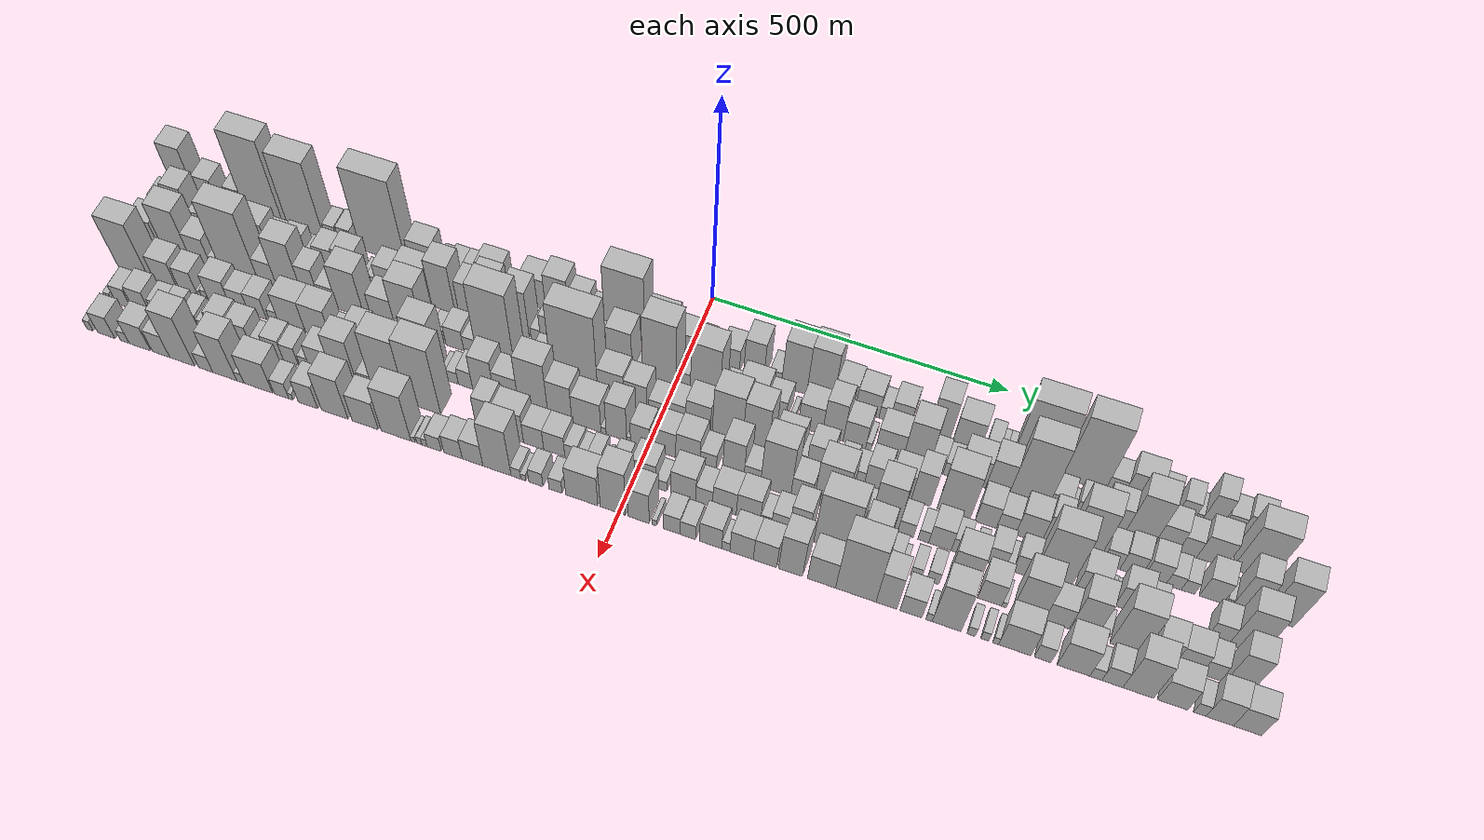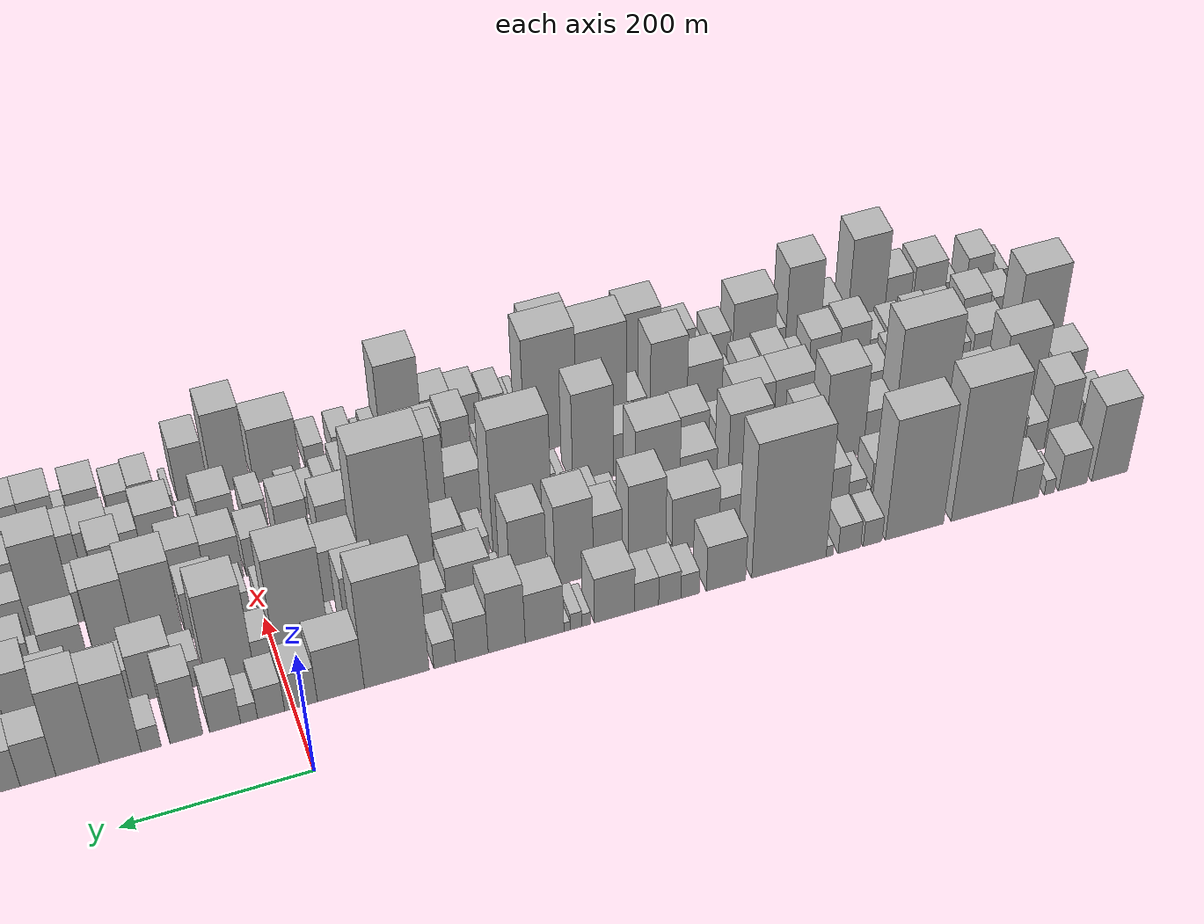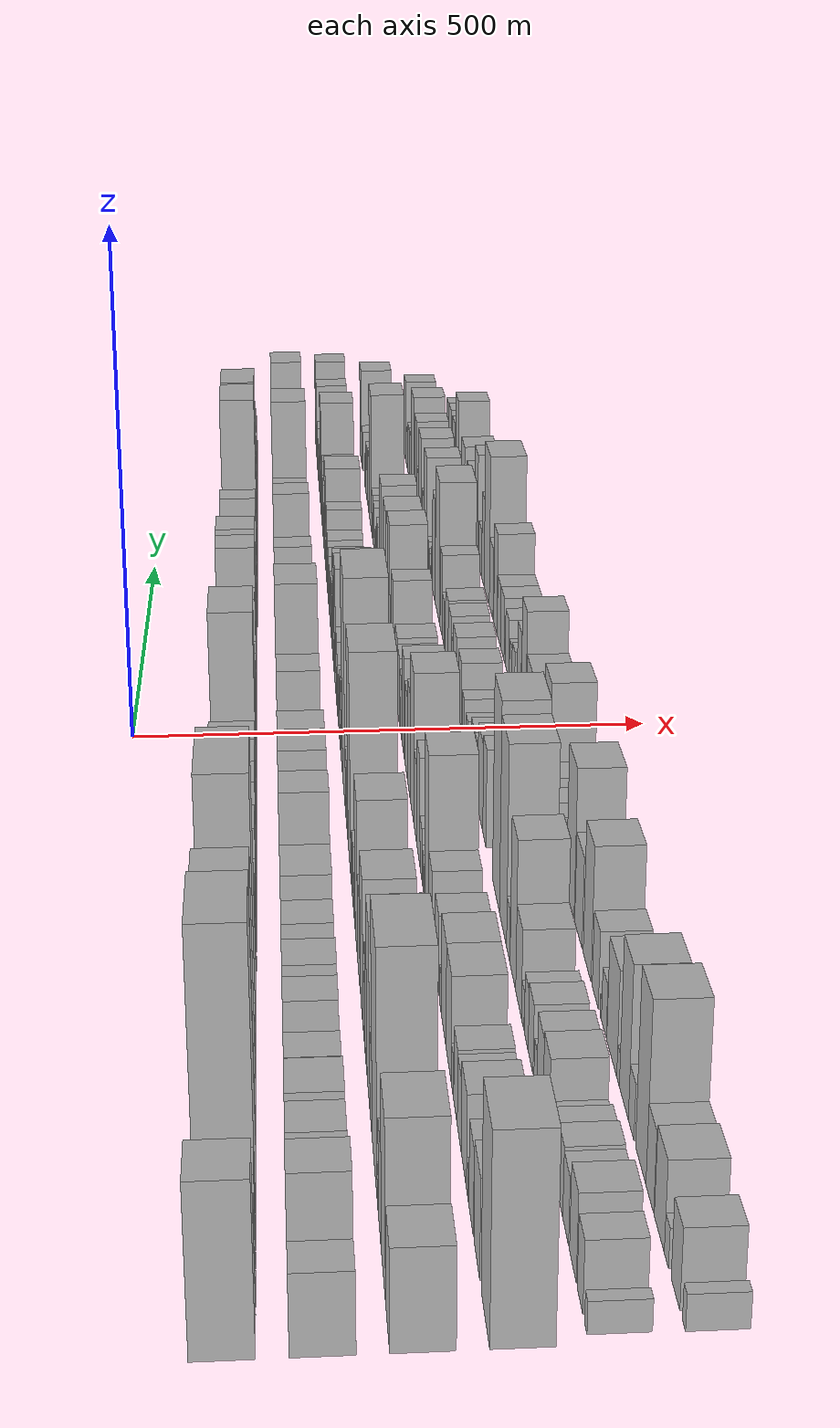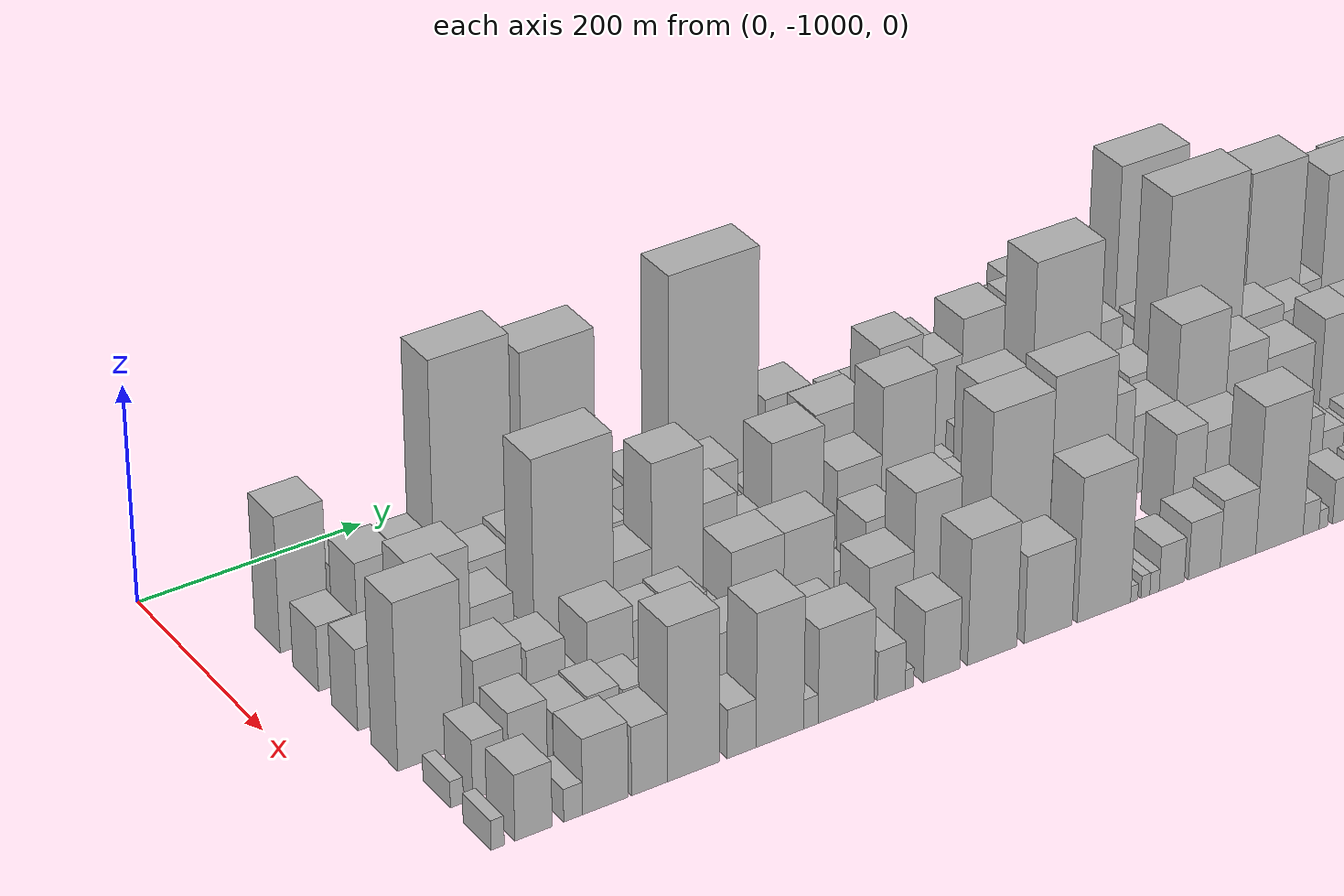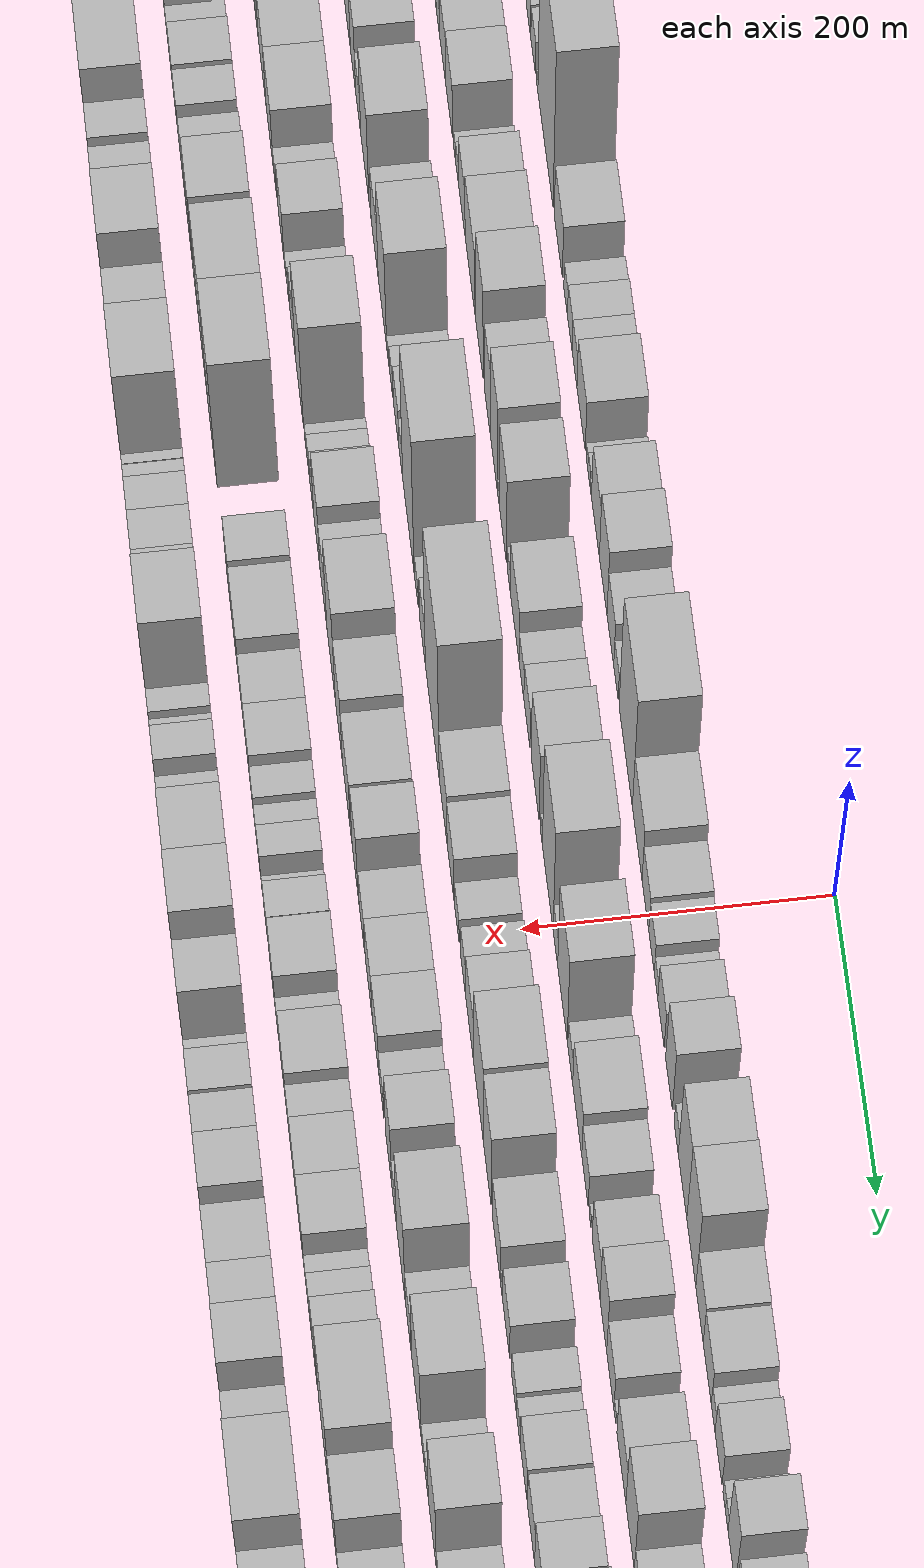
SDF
<sdf version="1.6">
 <world name="default">
  <scene>
   <sky><clouds><speed>12</speed></clouds></sky>
   <ambient>0.4 0.4 0.4 1</ambient>
   <background>0.7 0.7 0.7 1</background>
   <shadows>1</shadows>
  </scene>
  <gravity>0 0 -9.8066</gravity>
  <magnetic_field>6e-06 2.3e-05 -4.2e-05</magnetic_field>
  <physics default="0" name="default_physics" type="ode">
   <ode>
    <solver>
     <type>quick</type>
     <iters>10</iters>
     <sor>1.0</sor>
     <use_dynamic_moi_rescaling>0</use_dynamic_moi_rescaling>
    </solver>
    <constraints>
     <cfm>0</cfm>
     <erp>0.2</erp>
     <contact_max_correcting_vel>100</contact_max_correcting_vel>
     <contact_surface_layer>0.001</contact_surface_layer>
    </constraints>
   </ode>
   <max_step_size>0.004</max_step_size>
   <real_time_factor>1</real_time_factor>
   <real_time_update_rate>250</real_time_update_rate>
  </physics>
  <light name="sun" type="directional">
   <pose>0 0 10 0 0 0</pose>
   <diffuse>0.8 0.8 0.8 1</diffuse>
   <specular>0.2 0.2 0.2 1</specular>
   <attenuation>
    <range>1000</range>
    <constant>0.9</constant>
    <linear>0.01</linear>
    <quadratic>0.001</quadratic>
   </attenuation>
   <direction>-0.5 0.1 -0.9</direction>
  </light>
  <model name="building_1">
   <static>1</static>
   <pose>100.0000 -918.5534 0 0.000000 0.000000 0.000000</pose>
   <link name="link">
    <pose>0 0 63.00 0 0 0</pose>
    <collision name="collision"><geometry><box><size>40.0000 42.8932 126.0000</size></box></geometry></collision>
    <visual name="visual">
     <cast_shadows>0</cast_shadows>
     <geometry><box><size>40.0000 42.8932 126.0000</size></box></geometry>
     <material>
      <script>
       <uri>model://HANNAS_wall/materials/scripts</uri>
       <uri>model://HANNAS_wall/materials/textures</uri>
       <name>vrc/HANNAS_wall</name>
      </script>
     </material>
    </visual>
   </link>
  </model>
  <model name="building_2">
   <static>1</static>
   <pose>100.0000 -874.1622 0 0.000000 0.000000 0.000000</pose>
   <link name="link">
    <pose>0 0 30.00 0 0 0</pose>
    <collision name="collision"><geometry><box><size>40.0000 33.8893 60.0000</size></box></geometry></collision>
    <visual name="visual">
     <cast_shadows>0</cast_shadows>
     <geometry><box><size>40.0000 33.8893 60.0000</size></box></geometry>
     <material>
      <script>
       <uri>model://HANNAS_wall/materials/scripts</uri>
       <uri>model://HANNAS_wall/materials/textures</uri>
       <name>vrc/HANNAS_wall</name>
      </script>
     </material>
    </visual>
   </link>
  </model>
  <model name="building_3">
   <static>1</static>
   <pose>100.0000 -846.2349 0 0.000000 0.000000 0.000000</pose>
   <link name="link">
    <pose>0 0 12.00 0 0 0</pose>
    <collision name="collision"><geometry><box><size>40.0000 11.9653 24.0000</size></box></geometry></collision>
    <visual name="visual">
     <cast_shadows>0</cast_shadows>
     <geometry><box><size>40.0000 11.9653 24.0000</size></box></geometry>
     <material>
      <script>
       <uri>model://HANNAS_wall/materials/scripts</uri>
       <uri>model://HANNAS_wall/materials/textures</uri>
       <name>vrc/HANNAS_wall</name>
      </script>
     </material>
    </visual>
   </link>
  </model>
  <model name="building_4">
   <static>1</static>
   <pose>100.0000 -817.5872 0 0.000000 0.000000 0.000000</pose>
   <link name="link">
    <pose>0 0 28.50 0 0 0</pose>
    <collision name="collision"><geometry><box><size>40.0000 31.3300 57.0000</size></box></geometry></collision>
    <visual name="visual">
     <cast_shadows>0</cast_shadows>
     <geometry><box><size>40.0000 31.3300 57.0000</size></box></geometry>
     <material>
      <script>
       <uri>model://HANNAS_wall/materials/scripts</uri>
       <uri>model://HANNAS_wall/materials/textures</uri>
       <name>vrc/HANNAS_wall</name>
      </script>
     </material>
    </visual>
   </link>
  </model>
  <model name="building_5">
   <static>1</static>
   <pose>100.0000 -766.0420 0 0.000000 0.000000 0.000000</pose>
   <link name="link">
    <pose>0 0 109.50 0 0 0</pose>
    <collision name="collision"><geometry><box><size>40.0000 71.7605 219.0000</size></box></geometry></collision>
    <visual name="visual">
     <cast_shadows>0</cast_shadows>
     <geometry><box><size>40.0000 71.7605 219.0000</size></box></geometry>
     <material>
      <script>
       <uri>model://HANNAS_wall/materials/scripts</uri>
       <uri>model://HANNAS_wall/materials/textures</uri>
       <name>vrc/HANNAS_wall</name>
      </script>
     </material>
    </visual>
   </link>
  </model>
  <model name="building_6">
   <static>1</static>
   <pose>100.0000 -687.2929 0 0.000000 0.000000 0.000000</pose>
   <link name="link">
    <pose>0 0 99.00 0 0 0</pose>
    <collision name="collision"><geometry><box><size>40.0000 67.7378 198.0000</size></box></geometry></collision>
    <visual name="visual">
     <cast_shadows>0</cast_shadows>
     <geometry><box><size>40.0000 67.7378 198.0000</size></box></geometry>
     <material>
      <script>
       <uri>model://HANNAS_wall/materials/scripts</uri>
       <uri>model://HANNAS_wall/materials/textures</uri>
       <name>vrc/HANNAS_wall</name>
      </script>
     </material>
    </visual>
   </link>
  </model>
  <model name="building_7">
   <static>1</static>
   <pose>100.0000 -638.5477 0 0.000000 0.000000 0.000000</pose>
   <link name="link">
    <pose>0 0 21.00 0 0 0</pose>
    <collision name="collision"><geometry><box><size>40.0000 21.7526 42.0000</size></box></geometry></collision>
    <visual name="visual">
     <cast_shadows>0</cast_shadows>
     <geometry><box><size>40.0000 21.7526 42.0000</size></box></geometry>
     <material>
      <script>
       <uri>model://HANNAS_wall/materials/scripts</uri>
       <uri>model://HANNAS_wall/materials/textures</uri>
       <name>vrc/HANNAS_wall</name>
      </script>
     </material>
    </visual>
   </link>
  </model>
  <model name="building_8">
   <static>1</static>
   <pose>100.0000 -611.7169 0 0.000000 0.000000 0.000000</pose>
   <link name="link">
    <pose>0 0 22.50 0 0 0</pose>
    <collision name="collision"><geometry><box><size>40.0000 25.9090 45.0000</size></box></geometry></collision>
    <visual name="visual">
     <cast_shadows>0</cast_shadows>
     <geometry><box><size>40.0000 25.9090 45.0000</size></box></geometry>
     <material>
      <script>
       <uri>model://HANNAS_wall/materials/scripts</uri>
       <uri>model://HANNAS_wall/materials/textures</uri>
       <name>vrc/HANNAS_wall</name>
      </script>
     </material>
    </visual>
   </link>
  </model>
  <model name="building_9">
   <static>1</static>
   <pose>100.0000 -588.8372 0 0.000000 0.000000 0.000000</pose>
   <link name="link">
    <pose>0 0 9.00 0 0 0</pose>
    <collision name="collision"><geometry><box><size>40.0000 7.8504 18.0000</size></box></geometry></collision>
    <visual name="visual">
     <cast_shadows>0</cast_shadows>
     <geometry><box><size>40.0000 7.8504 18.0000</size></box></geometry>
     <material>
      <script>
       <uri>model://HANNAS_wall/materials/scripts</uri>
       <uri>model://HANNAS_wall/materials/textures</uri>
       <name>vrc/HANNAS_wall</name>
      </script>
     </material>
    </visual>
   </link>
  </model>
  <model name="building_10">
   <static>1</static>
   <pose>100.0000 -542.4456 0 0.000000 0.000000 0.000000</pose>
   <link name="link">
    <pose>0 0 111.00 0 0 0</pose>
    <collision name="collision"><geometry><box><size>40.0000 84.9326 222.0000</size></box></geometry></collision>
    <visual name="visual">
     <cast_shadows>0</cast_shadows>
     <geometry><box><size>40.0000 84.9326 222.0000</size></box></geometry>
     <material>
      <script>
       <uri>model://HANNAS_wall/materials/scripts</uri>
       <uri>model://HANNAS_wall/materials/textures</uri>
       <name>vrc/HANNAS_wall</name>
      </script>
     </material>
    </visual>
   </link>
  </model>
  <model name="building_11">
   <static>1</static>
   <pose>100.0000 -470.8424 0 0.000000 0.000000 0.000000</pose>
   <link name="link">
    <pose>0 0 37.50 0 0 0</pose>
    <collision name="collision"><geometry><box><size>40.0000 44.2738 75.0000</size></box></geometry></collision>
    <visual name="visual">
     <cast_shadows>0</cast_shadows>
     <geometry><box><size>40.0000 44.2738 75.0000</size></box></geometry>
     <material>
      <script>
       <uri>model://HANNAS_wall/materials/scripts</uri>
       <uri>model://HANNAS_wall/materials/textures</uri>
       <name>vrc/HANNAS_wall</name>
      </script>
     </material>
    </visual>
   </link>
  </model>
  <model name="building_12">
   <static>1</static>
   <pose>100.0000 -430.4448 0 0.000000 0.000000 0.000000</pose>
   <link name="link">
    <pose>0 0 19.50 0 0 0</pose>
    <collision name="collision"><geometry><box><size>40.0000 20.5215 39.0000</size></box></geometry></collision>
    <visual name="visual">
     <cast_shadows>0</cast_shadows>
     <geometry><box><size>40.0000 20.5215 39.0000</size></box></geometry>
     <material>
      <script>
       <uri>model://HANNAS_wall/materials/scripts</uri>
       <uri>model://HANNAS_wall/materials/textures</uri>
       <name>vrc/HANNAS_wall</name>
      </script>
     </material>
    </visual>
   </link>
  </model>
  <model name="building_13">
   <static>1</static>
   <pose>100.0000 -407.6726 0 0.000000 0.000000 0.000000</pose>
   <link name="link">
    <pose>0 0 24.00 0 0 0</pose>
    <collision name="collision"><geometry><box><size>40.0000 25.0229 48.0000</size></box></geometry></collision>
    <visual name="visual">
     <cast_shadows>0</cast_shadows>
     <geometry><box><size>40.0000 25.0229 48.0000</size></box></geometry>
     <material>
      <script>
       <uri>model://HANNAS_wall/materials/scripts</uri>
       <uri>model://HANNAS_wall/materials/textures</uri>
       <name>vrc/HANNAS_wall</name>
      </script>
     </material>
    </visual>
   </link>
  </model>
  <model name="building_14">
   <static>1</static>
   <pose>100.0000 -381.9116 0 0.000000 0.000000 0.000000</pose>
   <link name="link">
    <pose>0 0 24.00 0 0 0</pose>
    <collision name="collision"><geometry><box><size>40.0000 26.4992 48.0000</size></box></geometry></collision>
    <visual name="visual">
     <cast_shadows>0</cast_shadows>
     <geometry><box><size>40.0000 26.4992 48.0000</size></box></geometry>
     <material>
      <script>
       <uri>model://HANNAS_wall/materials/scripts</uri>
       <uri>model://HANNAS_wall/materials/textures</uri>
       <name>vrc/HANNAS_wall</name>
      </script>
     </material>
    </visual>
   </link>
  </model>
  <model name="building_15">
   <static>1</static>
   <pose>100.0000 -346.2069 0 0.000000 0.000000 0.000000</pose>
   <link name="link">
    <pose>0 0 37.50 0 0 0</pose>
    <collision name="collision"><geometry><box><size>40.0000 44.9101 75.0000</size></box></geometry></collision>
    <visual name="visual">
     <cast_shadows>0</cast_shadows>
     <geometry><box><size>40.0000 44.9101 75.0000</size></box></geometry>
     <material>
      <script>
       <uri>model://HANNAS_wall/materials/scripts</uri>
       <uri>model://HANNAS_wall/materials/textures</uri>
       <name>vrc/HANNAS_wall</name>
      </script>
     </material>
    </visual>
   </link>
  </model>
  <model name="building_16">
   <static>1</static>
   <pose>100.0000 -314.9539 0 0.000000 0.000000 0.000000</pose>
   <link name="link">
    <pose>0 0 10.50 0 0 0</pose>
    <collision name="collision"><geometry><box><size>40.0000 9.5960 21.0000</size></box></geometry></collision>
    <visual name="visual">
     <cast_shadows>0</cast_shadows>
     <geometry><box><size>40.0000 9.5960 21.0000</size></box></geometry>
     <material>
      <script>
       <uri>model://HANNAS_wall/materials/scripts</uri>
       <uri>model://HANNAS_wall/materials/textures</uri>
       <name>vrc/HANNAS_wall</name>
      </script>
     </material>
    </visual>
   </link>
  </model>
  <model name="building_17">
   <static>1</static>
   <pose>100.0000 -303.6163 0 0.000000 0.000000 0.000000</pose>
   <link name="link">
    <pose>0 0 13.50 0 0 0</pose>
    <collision name="collision"><geometry><box><size>40.0000 13.0792 27.0000</size></box></geometry></collision>
    <visual name="visual">
     <cast_shadows>0</cast_shadows>
     <geometry><box><size>40.0000 13.0792 27.0000</size></box></geometry>
     <material>
      <script>
       <uri>model://HANNAS_wall/materials/scripts</uri>
       <uri>model://HANNAS_wall/materials/textures</uri>
       <name>vrc/HANNAS_wall</name>
      </script>
     </material>
    </visual>
   </link>
  </model>
  <model name="building_18">
   <static>1</static>
   <pose>100.0000 -293.6193 0 0.000000 0.000000 0.000000</pose>
   <link name="link">
    <pose>0 0 7.50 0 0 0</pose>
    <collision name="collision"><geometry><box><size>40.0000 6.9149 15.0000</size></box></geometry></collision>
    <visual name="visual">
     <cast_shadows>0</cast_shadows>
     <geometry><box><size>40.0000 6.9149 15.0000</size></box></geometry>
     <material>
      <script>
       <uri>model://HANNAS_wall/materials/scripts</uri>
       <uri>model://HANNAS_wall/materials/textures</uri>
       <name>vrc/HANNAS_wall</name>
      </script>
     </material>
    </visual>
   </link>
  </model>
  <model name="building_19">
   <static>1</static>
   <pose>100.0000 -268.9465 0 0.000000 0.000000 0.000000</pose>
   <link name="link">
    <pose>0 0 40.50 0 0 0</pose>
    <collision name="collision"><geometry><box><size>40.0000 42.4308 81.0000</size></box></geometry></collision>
    <visual name="visual">
     <cast_shadows>0</cast_shadows>
     <geometry><box><size>40.0000 42.4308 81.0000</size></box></geometry>
     <material>
      <script>
       <uri>model://HANNAS_wall/materials/scripts</uri>
       <uri>model://HANNAS_wall/materials/textures</uri>
       <name>vrc/HANNAS_wall</name>
      </script>
     </material>
    </visual>
   </link>
  </model>
  <model name="building_20">
   <static>1</static>
   <pose>100.0000 -227.5812 0 0.000000 0.000000 0.000000</pose>
   <link name="link">
    <pose>0 0 51.00 0 0 0</pose>
    <collision name="collision"><geometry><box><size>40.0000 40.2998 102.0000</size></box></geometry></collision>
    <visual name="visual">
     <cast_shadows>0</cast_shadows>
     <geometry><box><size>40.0000 40.2998 102.0000</size></box></geometry>
     <material>
      <script>
       <uri>model://HANNAS_wall/materials/scripts</uri>
       <uri>model://HANNAS_wall/materials/textures</uri>
       <name>vrc/HANNAS_wall</name>
      </script>
     </material>
    </visual>
   </link>
  </model>
  <model name="building_21">
   <static>1</static>
   <pose>100.0000 -189.7104 0 0.000000 0.000000 0.000000</pose>
   <link name="link">
    <pose>0 0 34.50 0 0 0</pose>
    <collision name="collision"><geometry><box><size>40.0000 35.4419 69.0000</size></box></geometry></collision>
    <visual name="visual">
     <cast_shadows>0</cast_shadows>
     <geometry><box><size>40.0000 35.4419 69.0000</size></box></geometry>
     <material>
      <script>
       <uri>model://HANNAS_wall/materials/scripts</uri>
       <uri>model://HANNAS_wall/materials/textures</uri>
       <name>vrc/HANNAS_wall</name>
      </script>
     </material>
    </visual>
   </link>
  </model>
  <model name="building_22">
   <static>1</static>
   <pose>100.0000 -160.2569 0 0.000000 0.000000 0.000000</pose>
   <link name="link">
    <pose>0 0 21.00 0 0 0</pose>
    <collision name="collision"><geometry><box><size>40.0000 23.4650 42.0000</size></box></geometry></collision>
    <visual name="visual">
     <cast_shadows>0</cast_shadows>
     <geometry><box><size>40.0000 23.4650 42.0000</size></box></geometry>
     <material>
      <script>
       <uri>model://HANNAS_wall/materials/scripts</uri>
       <uri>model://HANNAS_wall/materials/textures</uri>
       <name>vrc/HANNAS_wall</name>
      </script>
     </material>
    </visual>
   </link>
  </model>
  <model name="building_23">
   <static>1</static>
   <pose>100.0000 -108.8378 0 0.000000 0.000000 0.000000</pose>
   <link name="link">
    <pose>0 0 90.00 0 0 0</pose>
    <collision name="collision"><geometry><box><size>40.0000 69.3731 180.0000</size></box></geometry></collision>
    <visual name="visual">
     <cast_shadows>0</cast_shadows>
     <geometry><box><size>40.0000 69.3731 180.0000</size></box></geometry>
     <material>
      <script>
       <uri>model://HANNAS_wall/materials/scripts</uri>
       <uri>model://HANNAS_wall/materials/textures</uri>
       <name>vrc/HANNAS_wall</name>
      </script>
     </material>
    </visual>
   </link>
  </model>
  <model name="building_24">
   <static>1</static>
   <pose>100.0000 -49.2360 0 0.000000 0.000000 0.000000</pose>
   <link name="link">
    <pose>0 0 43.50 0 0 0</pose>
    <collision name="collision"><geometry><box><size>40.0000 49.8305 87.0000</size></box></geometry></collision>
    <visual name="visual">
     <cast_shadows>0</cast_shadows>
     <geometry><box><size>40.0000 49.8305 87.0000</size></box></geometry>
     <material>
      <script>
       <uri>model://HANNAS_wall/materials/scripts</uri>
       <uri>model://HANNAS_wall/materials/textures</uri>
       <name>vrc/HANNAS_wall</name>
      </script>
     </material>
    </visual>
   </link>
  </model>
  <model name="building_25">
   <static>1</static>
   <pose>100.0000 -7.0572 0 0.000000 0.000000 0.000000</pose>
   <link name="link">
    <pose>0 0 30.00 0 0 0</pose>
    <collision name="collision"><geometry><box><size>40.0000 34.5271 60.0000</size></box></geometry></collision>
    <visual name="visual">
     <cast_shadows>0</cast_shadows>
     <geometry><box><size>40.0000 34.5271 60.0000</size></box></geometry>
     <material>
      <script>
       <uri>model://HANNAS_wall/materials/scripts</uri>
       <uri>model://HANNAS_wall/materials/textures</uri>
       <name>vrc/HANNAS_wall</name>
      </script>
     </material>
    </visual>
   </link>
  </model>
  <model name="building_26">
   <static>1</static>
   <pose>100.0000 24.4348 0 0.000000 0.000000 0.000000</pose>
   <link name="link">
    <pose>0 0 25.50 0 0 0</pose>
    <collision name="collision"><geometry><box><size>40.0000 28.4571 51.0000</size></box></geometry></collision>
    <visual name="visual">
     <cast_shadows>0</cast_shadows>
     <geometry><box><size>40.0000 28.4571 51.0000</size></box></geometry>
     <material>
      <script>
       <uri>model://HANNAS_wall/materials/scripts</uri>
       <uri>model://HANNAS_wall/materials/textures</uri>
       <name>vrc/HANNAS_wall</name>
      </script>
     </material>
    </visual>
   </link>
  </model>
  <model name="building_27">
   <static>1</static>
   <pose>100.0000 47.5312 0 0.000000 0.000000 0.000000</pose>
   <link name="link">
    <pose>0 0 15.00 0 0 0</pose>
    <collision name="collision"><geometry><box><size>40.0000 17.7357 30.0000</size></box></geometry></collision>
    <visual name="visual">
     <cast_shadows>0</cast_shadows>
     <geometry><box><size>40.0000 17.7357 30.0000</size></box></geometry>
     <material>
      <script>
       <uri>model://HANNAS_wall/materials/scripts</uri>
       <uri>model://HANNAS_wall/materials/textures</uri>
       <name>vrc/HANNAS_wall</name>
      </script>
     </material>
    </visual>
   </link>
  </model>
  <model name="building_28">
   <static>1</static>
   <pose>100.0000 72.5629 0 0.000000 0.000000 0.000000</pose>
   <link name="link">
    <pose>0 0 31.50 0 0 0</pose>
    <collision name="collision"><geometry><box><size>40.0000 32.3277 63.0000</size></box></geometry></collision>
    <visual name="visual">
     <cast_shadows>0</cast_shadows>
     <geometry><box><size>40.0000 32.3277 63.0000</size></box></geometry>
     <material>
      <script>
       <uri>model://HANNAS_wall/materials/scripts</uri>
       <uri>model://HANNAS_wall/materials/textures</uri>
       <name>vrc/HANNAS_wall</name>
      </script>
     </material>
    </visual>
   </link>
  </model>
  <model name="building_29">
   <static>1</static>
   <pose>100.0000 112.8015 0 0.000000 0.000000 0.000000</pose>
   <link name="link">
    <pose>0 0 52.50 0 0 0</pose>
    <collision name="collision"><geometry><box><size>40.0000 34.1494 105.0000</size></box></geometry></collision>
    <visual name="visual">
     <cast_shadows>0</cast_shadows>
     <geometry><box><size>40.0000 34.1494 105.0000</size></box></geometry>
     <material>
      <script>
       <uri>model://HANNAS_wall/materials/scripts</uri>
       <uri>model://HANNAS_wall/materials/textures</uri>
       <name>vrc/HANNAS_wall</name>
      </script>
     </material>
    </visual>
   </link>
  </model>
  <model name="building_30">
   <static>1</static>
   <pose>100.0000 149.2179 0 0.000000 0.000000 0.000000</pose>
   <link name="link">
    <pose>0 0 19.50 0 0 0</pose>
    <collision name="collision"><geometry><box><size>40.0000 20.6833 39.0000</size></box></geometry></collision>
    <visual name="visual">
     <cast_shadows>0</cast_shadows>
     <geometry><box><size>40.0000 20.6833 39.0000</size></box></geometry>
     <material>
      <script>
       <uri>model://HANNAS_wall/materials/scripts</uri>
       <uri>model://HANNAS_wall/materials/textures</uri>
       <name>vrc/HANNAS_wall</name>
      </script>
     </material>
    </visual>
   </link>
  </model>
  <model name="building_31">
   <static>1</static>
   <pose>100.0000 180.7832 0 0.000000 0.000000 0.000000</pose>
   <link name="link">
    <pose>0 0 69.00 0 0 0</pose>
    <collision name="collision"><geometry><box><size>40.0000 42.4473 138.0000</size></box></geometry></collision>
    <visual name="visual">
     <cast_shadows>0</cast_shadows>
     <geometry><box><size>40.0000 42.4473 138.0000</size></box></geometry>
     <material>
      <script>
       <uri>model://HANNAS_wall/materials/scripts</uri>
       <uri>model://HANNAS_wall/materials/textures</uri>
       <name>vrc/HANNAS_wall</name>
      </script>
     </material>
    </visual>
   </link>
  </model>
  <model name="building_32">
   <static>1</static>
   <pose>100.0000 224.2471 0 0.000000 0.000000 0.000000</pose>
   <link name="link">
    <pose>0 0 72.00 0 0 0</pose>
    <collision name="collision"><geometry><box><size>40.0000 44.4804 144.0000</size></box></geometry></collision>
    <visual name="visual">
     <cast_shadows>0</cast_shadows>
     <geometry><box><size>40.0000 44.4804 144.0000</size></box></geometry>
     <material>
      <script>
       <uri>model://HANNAS_wall/materials/scripts</uri>
       <uri>model://HANNAS_wall/materials/textures</uri>
       <name>vrc/HANNAS_wall</name>
      </script>
     </material>
    </visual>
   </link>
  </model>
  <model name="building_33">
   <static>1</static>
   <pose>100.0000 264.6315 0 0.000000 0.000000 0.000000</pose>
   <link name="link">
    <pose>0 0 36.00 0 0 0</pose>
    <collision name="collision"><geometry><box><size>40.0000 36.2884 72.0000</size></box></geometry></collision>
    <visual name="visual">
     <cast_shadows>0</cast_shadows>
     <geometry><box><size>40.0000 36.2884 72.0000</size></box></geometry>
     <material>
      <script>
       <uri>model://HANNAS_wall/materials/scripts</uri>
       <uri>model://HANNAS_wall/materials/textures</uri>
       <name>vrc/HANNAS_wall</name>
      </script>
     </material>
    </visual>
   </link>
  </model>
  <model name="building_34">
   <static>1</static>
   <pose>100.0000 302.4038 0 0.000000 0.000000 0.000000</pose>
   <link name="link">
    <pose>0 0 33.00 0 0 0</pose>
    <collision name="collision"><geometry><box><size>40.0000 39.2563 66.0000</size></box></geometry></collision>
    <visual name="visual">
     <cast_shadows>0</cast_shadows>
     <geometry><box><size>40.0000 39.2563 66.0000</size></box></geometry>
     <material>
      <script>
       <uri>model://HANNAS_wall/materials/scripts</uri>
       <uri>model://HANNAS_wall/materials/textures</uri>
       <name>vrc/HANNAS_wall</name>
      </script>
     </material>
    </visual>
   </link>
  </model>
  <model name="building_35">
   <static>1</static>
   <pose>100.0000 331.2191 0 0.000000 0.000000 0.000000</pose>
   <link name="link">
    <pose>0 0 18.00 0 0 0</pose>
    <collision name="collision"><geometry><box><size>40.0000 18.3743 36.0000</size></box></geometry></collision>
    <visual name="visual">
     <cast_shadows>0</cast_shadows>
     <geometry><box><size>40.0000 18.3743 36.0000</size></box></geometry>
     <material>
      <script>
       <uri>model://HANNAS_wall/materials/scripts</uri>
       <uri>model://HANNAS_wall/materials/textures</uri>
       <name>vrc/HANNAS_wall</name>
      </script>
     </material>
    </visual>
   </link>
  </model>
  <model name="building_36">
   <static>1</static>
   <pose>100.0000 357.0505 0 0.000000 0.000000 0.000000</pose>
   <link name="link">
    <pose>0 0 31.50 0 0 0</pose>
    <collision name="collision"><geometry><box><size>40.0000 33.2884 63.0000</size></box></geometry></collision>
    <visual name="visual">
     <cast_shadows>0</cast_shadows>
     <geometry><box><size>40.0000 33.2884 63.0000</size></box></geometry>
     <material>
      <script>
       <uri>model://HANNAS_wall/materials/scripts</uri>
       <uri>model://HANNAS_wall/materials/textures</uri>
       <name>vrc/HANNAS_wall</name>
      </script>
     </material>
    </visual>
   </link>
  </model>
  <model name="building_37">
   <static>1</static>
   <pose>100.0000 384.2856 0 0.000000 0.000000 0.000000</pose>
   <link name="link">
    <pose>0 0 13.50 0 0 0</pose>
    <collision name="collision"><geometry><box><size>40.0000 11.1817 27.0000</size></box></geometry></collision>
    <visual name="visual">
     <cast_shadows>0</cast_shadows>
     <geometry><box><size>40.0000 11.1817 27.0000</size></box></geometry>
     <material>
      <script>
       <uri>model://HANNAS_wall/materials/scripts</uri>
       <uri>model://HANNAS_wall/materials/textures</uri>
       <name>vrc/HANNAS_wall</name>
      </script>
     </material>
    </visual>
   </link>
  </model>
  <model name="building_38">
   <static>1</static>
   <pose>100.0000 396.4469 0 0.000000 0.000000 0.000000</pose>
   <link name="link">
    <pose>0 0 13.50 0 0 0</pose>
    <collision name="collision"><geometry><box><size>40.0000 13.1409 27.0000</size></box></geometry></collision>
    <visual name="visual">
     <cast_shadows>0</cast_shadows>
     <geometry><box><size>40.0000 13.1409 27.0000</size></box></geometry>
     <material>
      <script>
       <uri>model://HANNAS_wall/materials/scripts</uri>
       <uri>model://HANNAS_wall/materials/textures</uri>
       <name>vrc/HANNAS_wall</name>
      </script>
     </material>
    </visual>
   </link>
  </model>
  <model name="building_39">
   <static>1</static>
   <pose>100.0000 420.1435 0 0.000000 0.000000 0.000000</pose>
   <link name="link">
    <pose>0 0 57.00 0 0 0</pose>
    <collision name="collision"><geometry><box><size>40.0000 34.2521 114.0000</size></box></geometry></collision>
    <visual name="visual">
     <cast_shadows>0</cast_shadows>
     <geometry><box><size>40.0000 34.2521 114.0000</size></box></geometry>
     <material>
      <script>
       <uri>model://HANNAS_wall/materials/scripts</uri>
       <uri>model://HANNAS_wall/materials/textures</uri>
       <name>vrc/HANNAS_wall</name>
      </script>
     </material>
    </visual>
   </link>
  </model>
  <model name="building_40">
   <static>1</static>
   <pose>100.0000 464.3153 0 0.000000 0.000000 0.000000</pose>
   <link name="link">
    <pose>0 0 39.00 0 0 0</pose>
    <collision name="collision"><geometry><box><size>40.0000 44.0917 78.0000</size></box></geometry></collision>
    <visual name="visual">
     <cast_shadows>0</cast_shadows>
     <geometry><box><size>40.0000 44.0917 78.0000</size></box></geometry>
     <material>
      <script>
       <uri>model://HANNAS_wall/materials/scripts</uri>
       <uri>model://HANNAS_wall/materials/textures</uri>
       <name>vrc/HANNAS_wall</name>
      </script>
     </material>
    </visual>
   </link>
  </model>
  <model name="building_41">
   <static>1</static>
   <pose>100.0000 503.8851 0 0.000000 0.000000 0.000000</pose>
   <link name="link">
    <pose>0 0 21.00 0 0 0</pose>
    <collision name="collision"><geometry><box><size>40.0000 21.0478 42.0000</size></box></geometry></collision>
    <visual name="visual">
     <cast_shadows>0</cast_shadows>
     <geometry><box><size>40.0000 21.0478 42.0000</size></box></geometry>
     <material>
      <script>
       <uri>model://HANNAS_wall/materials/scripts</uri>
       <uri>model://HANNAS_wall/materials/textures</uri>
       <name>vrc/HANNAS_wall</name>
      </script>
     </material>
    </visual>
   </link>
  </model>
  <model name="building_42">
   <static>1</static>
   <pose>100.0000 519.4775 0 0.000000 0.000000 0.000000</pose>
   <link name="link">
    <pose>0 0 12.00 0 0 0</pose>
    <collision name="collision"><geometry><box><size>40.0000 10.1371 24.0000</size></box></geometry></collision>
    <visual name="visual">
     <cast_shadows>0</cast_shadows>
     <geometry><box><size>40.0000 10.1371 24.0000</size></box></geometry>
     <material>
      <script>
       <uri>model://HANNAS_wall/materials/scripts</uri>
       <uri>model://HANNAS_wall/materials/textures</uri>
       <name>vrc/HANNAS_wall</name>
      </script>
     </material>
    </visual>
   </link>
  </model>
  <model name="building_43">
   <static>1</static>
   <pose>100.0000 530.2775 0 0.000000 0.000000 0.000000</pose>
   <link name="link">
    <pose>0 0 12.00 0 0 0</pose>
    <collision name="collision"><geometry><box><size>40.0000 11.4629 24.0000</size></box></geometry></collision>
    <visual name="visual">
     <cast_shadows>0</cast_shadows>
     <geometry><box><size>40.0000 11.4629 24.0000</size></box></geometry>
     <material>
      <script>
       <uri>model://HANNAS_wall/materials/scripts</uri>
       <uri>model://HANNAS_wall/materials/textures</uri>
       <name>vrc/HANNAS_wall</name>
      </script>
     </material>
    </visual>
   </link>
  </model>
  <model name="building_44">
   <static>1</static>
   <pose>100.0000 573.1640 0 0.000000 0.000000 0.000000</pose>
   <link name="link">
    <pose>0 0 96.00 0 0 0</pose>
    <collision name="collision"><geometry><box><size>40.0000 74.3101 192.0000</size></box></geometry></collision>
    <visual name="visual">
     <cast_shadows>0</cast_shadows>
     <geometry><box><size>40.0000 74.3101 192.0000</size></box></geometry>
     <material>
      <script>
       <uri>model://HANNAS_wall/materials/scripts</uri>
       <uri>model://HANNAS_wall/materials/textures</uri>
       <name>vrc/HANNAS_wall</name>
      </script>
     </material>
    </visual>
   </link>
  </model>
  <model name="building_45">
   <static>1</static>
   <pose>100.0000 650.6175 0 0.000000 0.000000 0.000000</pose>
   <link name="link">
    <pose>0 0 96.00 0 0 0</pose>
    <collision name="collision"><geometry><box><size>40.0000 66.5969 192.0000</size></box></geometry></collision>
    <visual name="visual">
     <cast_shadows>0</cast_shadows>
     <geometry><box><size>40.0000 66.5969 192.0000</size></box></geometry>
     <material>
      <script>
       <uri>model://HANNAS_wall/materials/scripts</uri>
       <uri>model://HANNAS_wall/materials/textures</uri>
       <name>vrc/HANNAS_wall</name>
      </script>
     </material>
    </visual>
   </link>
  </model>
  <model name="building_46">
   <static>1</static>
   <pose>100.0000 697.9124 0 0.000000 0.000000 0.000000</pose>
   <link name="link">
    <pose>0 0 24.00 0 0 0</pose>
    <collision name="collision"><geometry><box><size>40.0000 27.9930 48.0000</size></box></geometry></collision>
    <visual name="visual">
     <cast_shadows>0</cast_shadows>
     <geometry><box><size>40.0000 27.9930 48.0000</size></box></geometry>
     <material>
      <script>
       <uri>model://HANNAS_wall/materials/scripts</uri>
       <uri>model://HANNAS_wall/materials/textures</uri>
       <name>vrc/HANNAS_wall</name>
      </script>
     </material>
    </visual>
   </link>
  </model>
  <model name="building_47">
   <static>1</static>
   <pose>100.0000 735.1295 0 0.000000 0.000000 0.000000</pose>
   <link name="link">
    <pose>0 0 40.50 0 0 0</pose>
    <collision name="collision"><geometry><box><size>40.0000 46.4411 81.0000</size></box></geometry></collision>
    <visual name="visual">
     <cast_shadows>0</cast_shadows>
     <geometry><box><size>40.0000 46.4411 81.0000</size></box></geometry>
     <material>
      <script>
       <uri>model://HANNAS_wall/materials/scripts</uri>
       <uri>model://HANNAS_wall/materials/textures</uri>
       <name>vrc/HANNAS_wall</name>
      </script>
     </material>
    </visual>
   </link>
  </model>
  <model name="building_48">
   <static>1</static>
   <pose>100.0000 773.4925 0 0.000000 0.000000 0.000000</pose>
   <link name="link">
    <pose>0 0 25.50 0 0 0</pose>
    <collision name="collision"><geometry><box><size>40.0000 30.2850 51.0000</size></box></geometry></collision>
    <visual name="visual">
     <cast_shadows>0</cast_shadows>
     <geometry><box><size>40.0000 30.2850 51.0000</size></box></geometry>
     <material>
      <script>
       <uri>model://HANNAS_wall/materials/scripts</uri>
       <uri>model://HANNAS_wall/materials/textures</uri>
       <name>vrc/HANNAS_wall</name>
      </script>
     </material>
    </visual>
   </link>
  </model>
  <model name="building_49">
   <static>1</static>
   <pose>100.0000 808.5586 0 0.000000 0.000000 0.000000</pose>
   <link name="link">
    <pose>0 0 25.50 0 0 0</pose>
    <collision name="collision"><geometry><box><size>40.0000 25.8473 51.0000</size></box></geometry></collision>
    <visual name="visual">
     <cast_shadows>0</cast_shadows>
     <geometry><box><size>40.0000 25.8473 51.0000</size></box></geometry>
     <material>
      <script>
       <uri>model://HANNAS_wall/materials/scripts</uri>
       <uri>model://HANNAS_wall/materials/textures</uri>
       <name>vrc/HANNAS_wall</name>
      </script>
     </material>
    </visual>
   </link>
  </model>
  <model name="building_50">
   <static>1</static>
   <pose>100.0000 826.8289 0 0.000000 0.000000 0.000000</pose>
   <link name="link">
    <pose>0 0 12.00 0 0 0</pose>
    <collision name="collision"><geometry><box><size>40.0000 10.6932 24.0000</size></box></geometry></collision>
    <visual name="visual">
     <cast_shadows>0</cast_shadows>
     <geometry><box><size>40.0000 10.6932 24.0000</size></box></geometry>
     <material>
      <script>
       <uri>model://HANNAS_wall/materials/scripts</uri>
       <uri>model://HANNAS_wall/materials/textures</uri>
       <name>vrc/HANNAS_wall</name>
      </script>
     </material>
    </visual>
   </link>
  </model>
  <model name="building_51">
   <static>1</static>
   <pose>100.0000 846.5894 0 0.000000 0.000000 0.000000</pose>
   <link name="link">
    <pose>0 0 46.50 0 0 0</pose>
    <collision name="collision"><geometry><box><size>40.0000 28.8278 93.0000</size></box></geometry></collision>
    <visual name="visual">
     <cast_shadows>0</cast_shadows>
     <geometry><box><size>40.0000 28.8278 93.0000</size></box></geometry>
     <material>
      <script>
       <uri>model://HANNAS_wall/materials/scripts</uri>
       <uri>model://HANNAS_wall/materials/textures</uri>
       <name>vrc/HANNAS_wall</name>
      </script>
     </material>
    </visual>
   </link>
  </model>
  <model name="building_52">
   <static>1</static>
   <pose>100.0000 877.4008 0 0.000000 0.000000 0.000000</pose>
   <link name="link">
    <pose>0 0 25.50 0 0 0</pose>
    <collision name="collision"><geometry><box><size>40.0000 26.7949 51.0000</size></box></geometry></collision>
    <visual name="visual">
     <cast_shadows>0</cast_shadows>
     <geometry><box><size>40.0000 26.7949 51.0000</size></box></geometry>
     <material>
      <script>
       <uri>model://HANNAS_wall/materials/scripts</uri>
       <uri>model://HANNAS_wall/materials/textures</uri>
       <name>vrc/HANNAS_wall</name>
      </script>
     </material>
    </visual>
   </link>
  </model>
  <model name="building_53">
   <static>1</static>
   <pose>100.0000 908.1045 0 0.000000 0.000000 0.000000</pose>
   <link name="link">
    <pose>0 0 33.00 0 0 0</pose>
    <collision name="collision"><geometry><box><size>40.0000 34.6125 66.0000</size></box></geometry></collision>
    <visual name="visual">
     <cast_shadows>0</cast_shadows>
     <geometry><box><size>40.0000 34.6125 66.0000</size></box></geometry>
     <material>
      <script>
       <uri>model://HANNAS_wall/materials/scripts</uri>
       <uri>model://HANNAS_wall/materials/textures</uri>
       <name>vrc/HANNAS_wall</name>
      </script>
     </material>
    </visual>
   </link>
  </model>
  <model name="building_54">
   <static>1</static>
   <pose>100.0000 936.5888 0 0.000000 0.000000 0.000000</pose>
   <link name="link">
    <pose>0 0 19.50 0 0 0</pose>
    <collision name="collision"><geometry><box><size>40.0000 22.3562 39.0000</size></box></geometry></collision>
    <visual name="visual">
     <cast_shadows>0</cast_shadows>
     <geometry><box><size>40.0000 22.3562 39.0000</size></box></geometry>
     <material>
      <script>
       <uri>model://HANNAS_wall/materials/scripts</uri>
       <uri>model://HANNAS_wall/materials/textures</uri>
       <name>vrc/HANNAS_wall</name>
      </script>
     </material>
    </visual>
   </link>
  </model>
  <model name="building_55">
   <static>1</static>
   <pose>160.0000 -924.2510 0 0.000000 0.000000 0.000000</pose>
   <link name="link">
    <pose>0 0 30.00 0 0 0</pose>
    <collision name="collision"><geometry><box><size>40.0000 31.4981 60.0000</size></box></geometry></collision>
    <visual name="visual">
     <cast_shadows>0</cast_shadows>
     <geometry><box><size>40.0000 31.4981 60.0000</size></box></geometry>
     <material>
      <script>
       <uri>model://HANNAS_wall/materials/scripts</uri>
       <uri>model://HANNAS_wall/materials/textures</uri>
       <name>vrc/HANNAS_wall</name>
      </script>
     </material>
    </visual>
   </link>
  </model>
  <model name="building_56">
   <static>1</static>
   <pose>160.0000 -886.0669 0 0.000000 0.000000 0.000000</pose>
   <link name="link">
    <pose>0 0 52.50 0 0 0</pose>
    <collision name="collision"><geometry><box><size>40.0000 36.8700 105.0000</size></box></geometry></collision>
    <visual name="visual">
     <cast_shadows>0</cast_shadows>
     <geometry><box><size>40.0000 36.8700 105.0000</size></box></geometry>
     <material>
      <script>
       <uri>model://HANNAS_wall/materials/scripts</uri>
       <uri>model://HANNAS_wall/materials/textures</uri>
       <name>vrc/HANNAS_wall</name>
      </script>
     </material>
    </visual>
   </link>
  </model>
  <model name="building_57">
   <static>1</static>
   <pose>160.0000 -855.0341 0 0.000000 0.000000 0.000000</pose>
   <link name="link">
    <pose>0 0 24.00 0 0 0</pose>
    <collision name="collision"><geometry><box><size>40.0000 25.1956 48.0000</size></box></geometry></collision>
    <visual name="visual">
     <cast_shadows>0</cast_shadows>
     <geometry><box><size>40.0000 25.1956 48.0000</size></box></geometry>
     <material>
      <script>
       <uri>model://HANNAS_wall/materials/scripts</uri>
       <uri>model://HANNAS_wall/materials/textures</uri>
       <name>vrc/HANNAS_wall</name>
      </script>
     </material>
    </visual>
   </link>
  </model>
  <model name="building_58">
   <static>1</static>
   <pose>160.0000 -824.1396 0 0.000000 0.000000 0.000000</pose>
   <link name="link">
    <pose>0 0 31.50 0 0 0</pose>
    <collision name="collision"><geometry><box><size>40.0000 36.5934 63.0000</size></box></geometry></collision>
    <visual name="visual">
     <cast_shadows>0</cast_shadows>
     <geometry><box><size>40.0000 36.5934 63.0000</size></box></geometry>
     <material>
      <script>
       <uri>model://HANNAS_wall/materials/scripts</uri>
       <uri>model://HANNAS_wall/materials/textures</uri>
       <name>vrc/HANNAS_wall</name>
      </script>
     </material>
    </visual>
   </link>
  </model>
  <model name="building_59">
   <static>1</static>
   <pose>160.0000 -787.1878 0 0.000000 0.000000 0.000000</pose>
   <link name="link">
    <pose>0 0 34.50 0 0 0</pose>
    <collision name="collision"><geometry><box><size>40.0000 37.3101 69.0000</size></box></geometry></collision>
    <visual name="visual">
     <cast_shadows>0</cast_shadows>
     <geometry><box><size>40.0000 37.3101 69.0000</size></box></geometry>
     <material>
      <script>
       <uri>model://HANNAS_wall/materials/scripts</uri>
       <uri>model://HANNAS_wall/materials/textures</uri>
       <name>vrc/HANNAS_wall</name>
      </script>
     </material>
    </visual>
   </link>
  </model>
  <model name="building_60">
   <static>1</static>
   <pose>160.0000 -746.8631 0 0.000000 0.000000 0.000000</pose>
   <link name="link">
    <pose>0 0 37.50 0 0 0</pose>
    <collision name="collision"><geometry><box><size>40.0000 43.3393 75.0000</size></box></geometry></collision>
    <visual name="visual">
     <cast_shadows>0</cast_shadows>
     <geometry><box><size>40.0000 43.3393 75.0000</size></box></geometry>
     <material>
      <script>
       <uri>model://HANNAS_wall/materials/scripts</uri>
       <uri>model://HANNAS_wall/materials/textures</uri>
       <name>vrc/HANNAS_wall</name>
      </script>
     </material>
    </visual>
   </link>
  </model>
  <model name="building_61">
   <static>1</static>
   <pose>160.0000 -710.0617 0 0.000000 0.000000 0.000000</pose>
   <link name="link">
    <pose>0 0 25.50 0 0 0</pose>
    <collision name="collision"><geometry><box><size>40.0000 30.2634 51.0000</size></box></geometry></collision>
    <visual name="visual">
     <cast_shadows>0</cast_shadows>
     <geometry><box><size>40.0000 30.2634 51.0000</size></box></geometry>
     <material>
      <script>
       <uri>model://HANNAS_wall/materials/scripts</uri>
       <uri>model://HANNAS_wall/materials/textures</uri>
       <name>vrc/HANNAS_wall</name>
      </script>
     </material>
    </visual>
   </link>
  </model>
  <model name="building_62">
   <static>1</static>
   <pose>160.0000 -678.1317 0 0.000000 0.000000 0.000000</pose>
   <link name="link">
    <pose>0 0 28.50 0 0 0</pose>
    <collision name="collision"><geometry><box><size>40.0000 33.5968 57.0000</size></box></geometry></collision>
    <visual name="visual">
     <cast_shadows>0</cast_shadows>
     <geometry><box><size>40.0000 33.5968 57.0000</size></box></geometry>
     <material>
      <script>
       <uri>model://HANNAS_wall/materials/scripts</uri>
       <uri>model://HANNAS_wall/materials/textures</uri>
       <name>vrc/HANNAS_wall</name>
      </script>
     </material>
    </visual>
   </link>
  </model>
  <model name="building_63">
   <static>1</static>
   <pose>160.0000 -658.0285 0 0.000000 0.000000 0.000000</pose>
   <link name="link">
    <pose>0 0 7.50 0 0 0</pose>
    <collision name="collision"><geometry><box><size>40.0000 6.6095 15.0000</size></box></geometry></collision>
    <visual name="visual">
     <cast_shadows>0</cast_shadows>
     <geometry><box><size>40.0000 6.6095 15.0000</size></box></geometry>
     <material>
      <script>
       <uri>model://HANNAS_wall/materials/scripts</uri>
       <uri>model://HANNAS_wall/materials/textures</uri>
       <name>vrc/HANNAS_wall</name>
      </script>
     </material>
    </visual>
   </link>
  </model>
  <model name="building_64">
   <static>1</static>
   <pose>160.0000 -644.5541 0 0.000000 0.000000 0.000000</pose>
   <link name="link">
    <pose>0 0 18.00 0 0 0</pose>
    <collision name="collision"><geometry><box><size>40.0000 20.3393 36.0000</size></box></geometry></collision>
    <visual name="visual">
     <cast_shadows>0</cast_shadows>
     <geometry><box><size>40.0000 20.3393 36.0000</size></box></geometry>
     <material>
      <script>
       <uri>model://HANNAS_wall/materials/scripts</uri>
       <uri>model://HANNAS_wall/materials/textures</uri>
       <name>vrc/HANNAS_wall</name>
      </script>
     </material>
    </visual>
   </link>
  </model>
  <model name="building_65">
   <static>1</static>
   <pose>160.0000 -616.4208 0 0.000000 0.000000 0.000000</pose>
   <link name="link">
    <pose>0 0 33.00 0 0 0</pose>
    <collision name="collision"><geometry><box><size>40.0000 35.9275 66.0000</size></box></geometry></collision>
    <visual name="visual">
     <cast_shadows>0</cast_shadows>
     <geometry><box><size>40.0000 35.9275 66.0000</size></box></geometry>
     <material>
      <script>
       <uri>model://HANNAS_wall/materials/scripts</uri>
       <uri>model://HANNAS_wall/materials/textures</uri>
       <name>vrc/HANNAS_wall</name>
      </script>
     </material>
    </visual>
   </link>
  </model>
  <model name="building_66">
   <static>1</static>
   <pose>160.0000 -578.4896 0 0.000000 0.000000 0.000000</pose>
   <link name="link">
    <pose>0 0 37.50 0 0 0</pose>
    <collision name="collision"><geometry><box><size>40.0000 39.9348 75.0000</size></box></geometry></collision>
    <visual name="visual">
     <cast_shadows>0</cast_shadows>
     <geometry><box><size>40.0000 39.9348 75.0000</size></box></geometry>
     <material>
      <script>
       <uri>model://HANNAS_wall/materials/scripts</uri>
       <uri>model://HANNAS_wall/materials/textures</uri>
       <name>vrc/HANNAS_wall</name>
      </script>
     </material>
    </visual>
   </link>
  </model>
  <model name="building_67">
   <static>1</static>
   <pose>160.0000 -545.2296 0 0.000000 0.000000 0.000000</pose>
   <link name="link">
    <pose>0 0 12.00 0 0 0</pose>
    <collision name="collision"><geometry><box><size>40.0000 10.5852 24.0000</size></box></geometry></collision>
    <visual name="visual">
     <cast_shadows>0</cast_shadows>
     <geometry><box><size>40.0000 10.5852 24.0000</size></box></geometry>
     <material>
      <script>
       <uri>model://HANNAS_wall/materials/scripts</uri>
       <uri>model://HANNAS_wall/materials/textures</uri>
       <name>vrc/HANNAS_wall</name>
      </script>
     </material>
    </visual>
   </link>
  </model>
  <model name="building_68">
   <static>1</static>
   <pose>160.0000 -531.9764 0 0.000000 0.000000 0.000000</pose>
   <link name="link">
    <pose>0 0 15.00 0 0 0</pose>
    <collision name="collision"><geometry><box><size>40.0000 15.9211 30.0000</size></box></geometry></collision>
    <visual name="visual">
     <cast_shadows>0</cast_shadows>
     <geometry><box><size>40.0000 15.9211 30.0000</size></box></geometry>
     <material>
      <script>
       <uri>model://HANNAS_wall/materials/scripts</uri>
       <uri>model://HANNAS_wall/materials/textures</uri>
       <name>vrc/HANNAS_wall</name>
      </script>
     </material>
    </visual>
   </link>
  </model>
  <model name="building_69">
   <static>1</static>
   <pose>160.0000 -504.6175 0 0.000000 0.000000 0.000000</pose>
   <link name="link">
    <pose>0 0 34.50 0 0 0</pose>
    <collision name="collision"><geometry><box><size>40.0000 38.7967 69.0000</size></box></geometry></collision>
    <visual name="visual">
     <cast_shadows>0</cast_shadows>
     <geometry><box><size>40.0000 38.7967 69.0000</size></box></geometry>
     <material>
      <script>
       <uri>model://HANNAS_wall/materials/scripts</uri>
       <uri>model://HANNAS_wall/materials/textures</uri>
       <name>vrc/HANNAS_wall</name>
      </script>
     </material>
    </visual>
   </link>
  </model>
  <model name="building_70">
   <static>1</static>
   <pose>160.0000 -458.4277 0 0.000000 0.000000 0.000000</pose>
   <link name="link">
    <pose>0 0 45.00 0 0 0</pose>
    <collision name="collision"><geometry><box><size>40.0000 53.5829 90.0000</size></box></geometry></collision>
    <visual name="visual">
     <cast_shadows>0</cast_shadows>
     <geometry><box><size>40.0000 53.5829 90.0000</size></box></geometry>
     <material>
      <script>
       <uri>model://HANNAS_wall/materials/scripts</uri>
       <uri>model://HANNAS_wall/materials/textures</uri>
       <name>vrc/HANNAS_wall</name>
      </script>
     </material>
    </visual>
   </link>
  </model>
  <model name="building_71">
   <static>1</static>
   <pose>160.0000 -428.1743 0 0.000000 0.000000 0.000000</pose>
   <link name="link">
    <pose>0 0 7.50 0 0 0</pose>
    <collision name="collision"><geometry><box><size>40.0000 6.9239 15.0000</size></box></geometry></collision>
    <visual name="visual">
     <cast_shadows>0</cast_shadows>
     <geometry><box><size>40.0000 6.9239 15.0000</size></box></geometry>
     <material>
      <script>
       <uri>model://HANNAS_wall/materials/scripts</uri>
       <uri>model://HANNAS_wall/materials/textures</uri>
       <name>vrc/HANNAS_wall</name>
      </script>
     </material>
    </visual>
   </link>
  </model>
  <model name="building_72">
   <static>1</static>
   <pose>160.0000 -403.7115 0 0.000000 0.000000 0.000000</pose>
   <link name="link">
    <pose>0 0 66.00 0 0 0</pose>
    <collision name="collision"><geometry><box><size>40.0000 42.0019 132.0000</size></box></geometry></collision>
    <visual name="visual">
     <cast_shadows>0</cast_shadows>
     <geometry><box><size>40.0000 42.0019 132.0000</size></box></geometry>
     <material>
      <script>
       <uri>model://HANNAS_wall/materials/scripts</uri>
       <uri>model://HANNAS_wall/materials/textures</uri>
       <name>vrc/HANNAS_wall</name>
      </script>
     </material>
    </visual>
   </link>
  </model>
  <model name="building_73">
   <static>1</static>
   <pose>160.0000 -359.5180 0 0.000000 0.000000 0.000000</pose>
   <link name="link">
    <pose>0 0 49.50 0 0 0</pose>
    <collision name="collision"><geometry><box><size>40.0000 32.3851 99.0000</size></box></geometry></collision>
    <visual name="visual">
     <cast_shadows>0</cast_shadows>
     <geometry><box><size>40.0000 32.3851 99.0000</size></box></geometry>
     <material>
      <script>
       <uri>model://HANNAS_wall/materials/scripts</uri>
       <uri>model://HANNAS_wall/materials/textures</uri>
       <name>vrc/HANNAS_wall</name>
      </script>
     </material>
    </visual>
   </link>
  </model>
  <model name="building_74">
   <static>1</static>
   <pose>160.0000 -322.0054 0 0.000000 0.000000 0.000000</pose>
   <link name="link">
    <pose>0 0 66.00 0 0 0</pose>
    <collision name="collision"><geometry><box><size>40.0000 42.6402 132.0000</size></box></geometry></collision>
    <visual name="visual">
     <cast_shadows>0</cast_shadows>
     <geometry><box><size>40.0000 42.6402 132.0000</size></box></geometry>
     <material>
      <script>
       <uri>model://HANNAS_wall/materials/scripts</uri>
       <uri>model://HANNAS_wall/materials/textures</uri>
       <name>vrc/HANNAS_wall</name>
      </script>
     </material>
    </visual>
   </link>
  </model>
  <model name="building_75">
   <static>1</static>
   <pose>160.0000 -296.1301 0 0.000000 0.000000 0.000000</pose>
   <link name="link">
    <pose>0 0 10.50 0 0 0</pose>
    <collision name="collision"><geometry><box><size>40.0000 9.1105 21.0000</size></box></geometry></collision>
    <visual name="visual">
     <cast_shadows>0</cast_shadows>
     <geometry><box><size>40.0000 9.1105 21.0000</size></box></geometry>
     <material>
      <script>
       <uri>model://HANNAS_wall/materials/scripts</uri>
       <uri>model://HANNAS_wall/materials/textures</uri>
       <name>vrc/HANNAS_wall</name>
      </script>
     </material>
    </visual>
   </link>
  </model>
  <model name="building_76">
   <static>1</static>
   <pose>160.0000 -271.3415 0 0.000000 0.000000 0.000000</pose>
   <link name="link">
    <pose>0 0 64.50 0 0 0</pose>
    <collision name="collision"><geometry><box><size>40.0000 40.4667 129.0000</size></box></geometry></collision>
    <visual name="visual">
     <cast_shadows>0</cast_shadows>
     <geometry><box><size>40.0000 40.4667 129.0000</size></box></geometry>
     <material>
      <script>
       <uri>model://HANNAS_wall/materials/scripts</uri>
       <uri>model://HANNAS_wall/materials/textures</uri>
       <name>vrc/HANNAS_wall</name>
      </script>
     </material>
    </visual>
   </link>
  </model>
  <model name="building_77">
   <static>1</static>
   <pose>160.0000 -239.2705 0 0.000000 0.000000 0.000000</pose>
   <link name="link">
    <pose>0 0 16.50 0 0 0</pose>
    <collision name="collision"><geometry><box><size>40.0000 17.6752 33.0000</size></box></geometry></collision>
    <visual name="visual">
     <cast_shadows>0</cast_shadows>
     <geometry><box><size>40.0000 17.6752 33.0000</size></box></geometry>
     <material>
      <script>
       <uri>model://HANNAS_wall/materials/scripts</uri>
       <uri>model://HANNAS_wall/materials/textures</uri>
       <name>vrc/HANNAS_wall</name>
      </script>
     </material>
    </visual>
   </link>
  </model>
  <model name="building_78">
   <static>1</static>
   <pose>160.0000 -206.2188 0 0.000000 0.000000 0.000000</pose>
   <link name="link">
    <pose>0 0 40.50 0 0 0</pose>
    <collision name="collision"><geometry><box><size>40.0000 48.4283 81.0000</size></box></geometry></collision>
    <visual name="visual">
     <cast_shadows>0</cast_shadows>
     <geometry><box><size>40.0000 48.4283 81.0000</size></box></geometry>
     <material>
      <script>
       <uri>model://HANNAS_wall/materials/scripts</uri>
       <uri>model://HANNAS_wall/materials/textures</uri>
       <name>vrc/HANNAS_wall</name>
      </script>
     </material>
    </visual>
   </link>
  </model>
  <model name="building_79">
   <static>1</static>
   <pose>160.0000 -168.6205 0 0.000000 0.000000 0.000000</pose>
   <link name="link">
    <pose>0 0 24.00 0 0 0</pose>
    <collision name="collision"><geometry><box><size>40.0000 26.7682 48.0000</size></box></geometry></collision>
    <visual name="visual">
     <cast_shadows>0</cast_shadows>
     <geometry><box><size>40.0000 26.7682 48.0000</size></box></geometry>
     <material>
      <script>
       <uri>model://HANNAS_wall/materials/scripts</uri>
       <uri>model://HANNAS_wall/materials/textures</uri>
       <name>vrc/HANNAS_wall</name>
      </script>
     </material>
    </visual>
   </link>
  </model>
  <model name="building_80">
   <static>1</static>
   <pose>160.0000 -138.8640 0 0.000000 0.000000 0.000000</pose>
   <link name="link">
    <pose>0 0 30.00 0 0 0</pose>
    <collision name="collision"><geometry><box><size>40.0000 32.7448 60.0000</size></box></geometry></collision>
    <visual name="visual">
     <cast_shadows>0</cast_shadows>
     <geometry><box><size>40.0000 32.7448 60.0000</size></box></geometry>
     <material>
      <script>
       <uri>model://HANNAS_wall/materials/scripts</uri>
       <uri>model://HANNAS_wall/materials/textures</uri>
       <name>vrc/HANNAS_wall</name>
      </script>
     </material>
    </visual>
   </link>
  </model>
  <model name="building_81">
   <static>1</static>
   <pose>160.0000 -93.9280 0 0.000000 0.000000 0.000000</pose>
   <link name="link">
    <pose>0 0 55.50 0 0 0</pose>
    <collision name="collision"><geometry><box><size>40.0000 43.1273 111.0000</size></box></geometry></collision>
    <visual name="visual">
     <cast_shadows>0</cast_shadows>
     <geometry><box><size>40.0000 43.1273 111.0000</size></box></geometry>
     <material>
      <script>
       <uri>model://HANNAS_wall/materials/scripts</uri>
       <uri>model://HANNAS_wall/materials/textures</uri>
       <name>vrc/HANNAS_wall</name>
      </script>
     </material>
    </visual>
   </link>
  </model>
  <model name="building_82">
   <static>1</static>
   <pose>160.0000 -60.4800 0 0.000000 0.000000 0.000000</pose>
   <link name="link">
    <pose>0 0 13.50 0 0 0</pose>
    <collision name="collision"><geometry><box><size>40.0000 11.7686 27.0000</size></box></geometry></collision>
    <visual name="visual">
     <cast_shadows>0</cast_shadows>
     <geometry><box><size>40.0000 11.7686 27.0000</size></box></geometry>
     <material>
      <script>
       <uri>model://HANNAS_wall/materials/scripts</uri>
       <uri>model://HANNAS_wall/materials/textures</uri>
       <name>vrc/HANNAS_wall</name>
      </script>
     </material>
    </visual>
   </link>
  </model>
  <model name="building_83">
   <static>1</static>
   <pose>160.0000 -25.7675 0 0.000000 0.000000 0.000000</pose>
   <link name="link">
    <pose>0 0 87.00 0 0 0</pose>
    <collision name="collision"><geometry><box><size>40.0000 57.6565 174.0000</size></box></geometry></collision>
    <visual name="visual">
     <cast_shadows>0</cast_shadows>
     <geometry><box><size>40.0000 57.6565 174.0000</size></box></geometry>
     <material>
      <script>
       <uri>model://HANNAS_wall/materials/scripts</uri>
       <uri>model://HANNAS_wall/materials/textures</uri>
       <name>vrc/HANNAS_wall</name>
      </script>
     </material>
    </visual>
   </link>
  </model>
  <model name="building_84">
   <static>1</static>
   <pose>160.0000 15.1243 0 0.000000 0.000000 0.000000</pose>
   <link name="link">
    <pose>0 0 24.00 0 0 0</pose>
    <collision name="collision"><geometry><box><size>40.0000 24.1272 48.0000</size></box></geometry></collision>
    <visual name="visual">
     <cast_shadows>0</cast_shadows>
     <geometry><box><size>40.0000 24.1272 48.0000</size></box></geometry>
     <material>
      <script>
       <uri>model://HANNAS_wall/materials/scripts</uri>
       <uri>model://HANNAS_wall/materials/textures</uri>
       <name>vrc/HANNAS_wall</name>
      </script>
     </material>
    </visual>
   </link>
  </model>
  <model name="building_85">
   <static>1</static>
   <pose>160.0000 52.2467 0 0.000000 0.000000 0.000000</pose>
   <link name="link">
    <pose>0 0 73.50 0 0 0</pose>
    <collision name="collision"><geometry><box><size>40.0000 50.1175 147.0000</size></box></geometry></collision>
    <visual name="visual">
     <cast_shadows>0</cast_shadows>
     <geometry><box><size>40.0000 50.1175 147.0000</size></box></geometry>
     <material>
      <script>
       <uri>model://HANNAS_wall/materials/scripts</uri>
       <uri>model://HANNAS_wall/materials/textures</uri>
       <name>vrc/HANNAS_wall</name>
      </script>
     </material>
    </visual>
   </link>
  </model>
  <model name="building_86">
   <static>1</static>
   <pose>160.0000 93.2717 0 0.000000 0.000000 0.000000</pose>
   <link name="link">
    <pose>0 0 22.50 0 0 0</pose>
    <collision name="collision"><geometry><box><size>40.0000 25.9326 45.0000</size></box></geometry></collision>
    <visual name="visual">
     <cast_shadows>0</cast_shadows>
     <geometry><box><size>40.0000 25.9326 45.0000</size></box></geometry>
     <material>
      <script>
       <uri>model://HANNAS_wall/materials/scripts</uri>
       <uri>model://HANNAS_wall/materials/textures</uri>
       <name>vrc/HANNAS_wall</name>
      </script>
     </material>
    </visual>
   </link>
  </model>
  <model name="building_87">
   <static>1</static>
   <pose>160.0000 129.9010 0 0.000000 0.000000 0.000000</pose>
   <link name="link">
    <pose>0 0 40.50 0 0 0</pose>
    <collision name="collision"><geometry><box><size>40.0000 47.3261 81.0000</size></box></geometry></collision>
    <visual name="visual">
     <cast_shadows>0</cast_shadows>
     <geometry><box><size>40.0000 47.3261 81.0000</size></box></geometry>
     <material>
      <script>
       <uri>model://HANNAS_wall/materials/scripts</uri>
       <uri>model://HANNAS_wall/materials/textures</uri>
       <name>vrc/HANNAS_wall</name>
      </script>
     </material>
    </visual>
   </link>
  </model>
  <model name="building_88">
   <static>1</static>
   <pose>160.0000 170.2879 0 0.000000 0.000000 0.000000</pose>
   <link name="link">
    <pose>0 0 30.00 0 0 0</pose>
    <collision name="collision"><geometry><box><size>40.0000 33.4475 60.0000</size></box></geometry></collision>
    <visual name="visual">
     <cast_shadows>0</cast_shadows>
     <geometry><box><size>40.0000 33.4475 60.0000</size></box></geometry>
     <material>
      <script>
       <uri>model://HANNAS_wall/materials/scripts</uri>
       <uri>model://HANNAS_wall/materials/textures</uri>
       <name>vrc/HANNAS_wall</name>
      </script>
     </material>
    </visual>
   </link>
  </model>
  <model name="building_89">
   <static>1</static>
   <pose>160.0000 196.2375 0 0.000000 0.000000 0.000000</pose>
   <link name="link">
    <pose>0 0 10.50 0 0 0</pose>
    <collision name="collision"><geometry><box><size>40.0000 8.4518 21.0000</size></box></geometry></collision>
    <visual name="visual">
     <cast_shadows>0</cast_shadows>
     <geometry><box><size>40.0000 8.4518 21.0000</size></box></geometry>
     <material>
      <script>
       <uri>model://HANNAS_wall/materials/scripts</uri>
       <uri>model://HANNAS_wall/materials/textures</uri>
       <name>vrc/HANNAS_wall</name>
      </script>
     </material>
    </visual>
   </link>
  </model>
  <model name="building_90">
   <static>1</static>
   <pose>160.0000 227.5681 0 0.000000 0.000000 0.000000</pose>
   <link name="link">
    <pose>0 0 37.50 0 0 0</pose>
    <collision name="collision"><geometry><box><size>40.0000 40.2094 75.0000</size></box></geometry></collision>
    <visual name="visual">
     <cast_shadows>0</cast_shadows>
     <geometry><box><size>40.0000 40.2094 75.0000</size></box></geometry>
     <material>
      <script>
       <uri>model://HANNAS_wall/materials/scripts</uri>
       <uri>model://HANNAS_wall/materials/textures</uri>
       <name>vrc/HANNAS_wall</name>
      </script>
     </material>
    </visual>
   </link>
  </model>
  <model name="building_91">
   <static>1</static>
   <pose>160.0000 264.7622 0 0.000000 0.000000 0.000000</pose>
   <link name="link">
    <pose>0 0 54.00 0 0 0</pose>
    <collision name="collision"><geometry><box><size>40.0000 34.1789 108.0000</size></box></geometry></collision>
    <visual name="visual">
     <cast_shadows>0</cast_shadows>
     <geometry><box><size>40.0000 34.1789 108.0000</size></box></geometry>
     <material>
      <script>
       <uri>model://HANNAS_wall/materials/scripts</uri>
       <uri>model://HANNAS_wall/materials/textures</uri>
       <name>vrc/HANNAS_wall</name>
      </script>
     </material>
    </visual>
   </link>
  </model>
  <model name="building_92">
   <static>1</static>
   <pose>160.0000 300.2078 0 0.000000 0.000000 0.000000</pose>
   <link name="link">
    <pose>0 0 33.00 0 0 0</pose>
    <collision name="collision"><geometry><box><size>40.0000 36.7122 66.0000</size></box></geometry></collision>
    <visual name="visual">
     <cast_shadows>0</cast_shadows>
     <geometry><box><size>40.0000 36.7122 66.0000</size></box></geometry>
     <material>
      <script>
       <uri>model://HANNAS_wall/materials/scripts</uri>
       <uri>model://HANNAS_wall/materials/textures</uri>
       <name>vrc/HANNAS_wall</name>
      </script>
     </material>
    </visual>
   </link>
  </model>
  <model name="building_93">
   <static>1</static>
   <pose>160.0000 323.1250 0 0.000000 0.000000 0.000000</pose>
   <link name="link">
    <pose>0 0 10.50 0 0 0</pose>
    <collision name="collision"><geometry><box><size>40.0000 9.1222 21.0000</size></box></geometry></collision>
    <visual name="visual">
     <cast_shadows>0</cast_shadows>
     <geometry><box><size>40.0000 9.1222 21.0000</size></box></geometry>
     <material>
      <script>
       <uri>model://HANNAS_wall/materials/scripts</uri>
       <uri>model://HANNAS_wall/materials/textures</uri>
       <name>vrc/HANNAS_wall</name>
      </script>
     </material>
    </visual>
   </link>
  </model>
  <model name="building_94">
   <static>1</static>
   <pose>160.0000 356.1797 0 0.000000 0.000000 0.000000</pose>
   <link name="link">
    <pose>0 0 37.50 0 0 0</pose>
    <collision name="collision"><geometry><box><size>40.0000 44.9871 75.0000</size></box></geometry></collision>
    <visual name="visual">
     <cast_shadows>0</cast_shadows>
     <geometry><box><size>40.0000 44.9871 75.0000</size></box></geometry>
     <material>
      <script>
       <uri>model://HANNAS_wall/materials/scripts</uri>
       <uri>model://HANNAS_wall/materials/textures</uri>
       <name>vrc/HANNAS_wall</name>
      </script>
     </material>
    </visual>
   </link>
  </model>
  <model name="building_95">
   <static>1</static>
   <pose>160.0000 399.6302 0 0.000000 0.000000 0.000000</pose>
   <link name="link">
    <pose>0 0 63.00 0 0 0</pose>
    <collision name="collision"><geometry><box><size>40.0000 41.9140 126.0000</size></box></geometry></collision>
    <visual name="visual">
     <cast_shadows>0</cast_shadows>
     <geometry><box><size>40.0000 41.9140 126.0000</size></box></geometry>
     <material>
      <script>
       <uri>model://HANNAS_wall/materials/scripts</uri>
       <uri>model://HANNAS_wall/materials/textures</uri>
       <name>vrc/HANNAS_wall</name>
      </script>
     </material>
    </visual>
   </link>
  </model>
  <model name="building_96">
   <static>1</static>
   <pose>160.0000 432.0486 0 0.000000 0.000000 0.000000</pose>
   <link name="link">
    <pose>0 0 22.50 0 0 0</pose>
    <collision name="collision"><geometry><box><size>40.0000 22.9228 45.0000</size></box></geometry></collision>
    <visual name="visual">
     <cast_shadows>0</cast_shadows>
     <geometry><box><size>40.0000 22.9228 45.0000</size></box></geometry>
     <material>
      <script>
       <uri>model://HANNAS_wall/materials/scripts</uri>
       <uri>model://HANNAS_wall/materials/textures</uri>
       <name>vrc/HANNAS_wall</name>
      </script>
     </material>
    </visual>
   </link>
  </model>
  <model name="building_97">
   <static>1</static>
   <pose>160.0000 454.7128 0 0.000000 0.000000 0.000000</pose>
   <link name="link">
    <pose>0 0 19.50 0 0 0</pose>
    <collision name="collision"><geometry><box><size>40.0000 22.4056 39.0000</size></box></geometry></collision>
    <visual name="visual">
     <cast_shadows>0</cast_shadows>
     <geometry><box><size>40.0000 22.4056 39.0000</size></box></geometry>
     <material>
      <script>
       <uri>model://HANNAS_wall/materials/scripts</uri>
       <uri>model://HANNAS_wall/materials/textures</uri>
       <name>vrc/HANNAS_wall</name>
      </script>
     </material>
    </visual>
   </link>
  </model>
  <model name="building_98">
   <static>1</static>
   <pose>160.0000 488.5397 0 0.000000 0.000000 0.000000</pose>
   <link name="link">
    <pose>0 0 39.00 0 0 0</pose>
    <collision name="collision"><geometry><box><size>40.0000 45.2482 78.0000</size></box></geometry></collision>
    <visual name="visual">
     <cast_shadows>0</cast_shadows>
     <geometry><box><size>40.0000 45.2482 78.0000</size></box></geometry>
     <material>
      <script>
       <uri>model://HANNAS_wall/materials/scripts</uri>
       <uri>model://HANNAS_wall/materials/textures</uri>
       <name>vrc/HANNAS_wall</name>
      </script>
     </material>
    </visual>
   </link>
  </model>
  <model name="building_99">
   <static>1</static>
   <pose>160.0000 529.4853 0 0.000000 0.000000 0.000000</pose>
   <link name="link">
    <pose>0 0 46.50 0 0 0</pose>
    <collision name="collision"><geometry><box><size>40.0000 36.6429 93.0000</size></box></geometry></collision>
    <visual name="visual">
     <cast_shadows>0</cast_shadows>
     <geometry><box><size>40.0000 36.6429 93.0000</size></box></geometry>
     <material>
      <script>
       <uri>model://HANNAS_wall/materials/scripts</uri>
       <uri>model://HANNAS_wall/materials/textures</uri>
       <name>vrc/HANNAS_wall</name>
      </script>
     </material>
    </visual>
   </link>
  </model>
  <model name="building_100">
   <static>1</static>
   <pose>160.0000 578.3323 0 0.000000 0.000000 0.000000</pose>
   <link name="link">
    <pose>0 0 93.00 0 0 0</pose>
    <collision name="collision"><geometry><box><size>40.0000 61.0512 186.0000</size></box></geometry></collision>
    <visual name="visual">
     <cast_shadows>0</cast_shadows>
     <geometry><box><size>40.0000 61.0512 186.0000</size></box></geometry>
     <material>
      <script>
       <uri>model://HANNAS_wall/materials/scripts</uri>
       <uri>model://HANNAS_wall/materials/textures</uri>
       <name>vrc/HANNAS_wall</name>
      </script>
     </material>
    </visual>
   </link>
  </model>
  <model name="building_101">
   <static>1</static>
   <pose>160.0000 624.1365 0 0.000000 0.000000 0.000000</pose>
   <link name="link">
    <pose>0 0 25.50 0 0 0</pose>
    <collision name="collision"><geometry><box><size>40.0000 30.5573 51.0000</size></box></geometry></collision>
    <visual name="visual">
     <cast_shadows>0</cast_shadows>
     <geometry><box><size>40.0000 30.5573 51.0000</size></box></geometry>
     <material>
      <script>
       <uri>model://HANNAS_wall/materials/scripts</uri>
       <uri>model://HANNAS_wall/materials/textures</uri>
       <name>vrc/HANNAS_wall</name>
      </script>
     </material>
    </visual>
   </link>
  </model>
  <model name="building_102">
   <static>1</static>
   <pose>160.0000 643.8614 0 0.000000 0.000000 0.000000</pose>
   <link name="link">
    <pose>0 0 10.50 0 0 0</pose>
    <collision name="collision"><geometry><box><size>40.0000 8.8925 21.0000</size></box></geometry></collision>
    <visual name="visual">
     <cast_shadows>0</cast_shadows>
     <geometry><box><size>40.0000 8.8925 21.0000</size></box></geometry>
     <material>
      <script>
       <uri>model://HANNAS_wall/materials/scripts</uri>
       <uri>model://HANNAS_wall/materials/textures</uri>
       <name>vrc/HANNAS_wall</name>
      </script>
     </material>
    </visual>
   </link>
  </model>
  <model name="building_103">
   <static>1</static>
   <pose>160.0000 663.3234 0 0.000000 0.000000 0.000000</pose>
   <link name="link">
    <pose>0 0 27.00 0 0 0</pose>
    <collision name="collision"><geometry><box><size>40.0000 30.0315 54.0000</size></box></geometry></collision>
    <visual name="visual">
     <cast_shadows>0</cast_shadows>
     <geometry><box><size>40.0000 30.0315 54.0000</size></box></geometry>
     <material>
      <script>
       <uri>model://HANNAS_wall/materials/scripts</uri>
       <uri>model://HANNAS_wall/materials/textures</uri>
       <name>vrc/HANNAS_wall</name>
      </script>
     </material>
    </visual>
   </link>
  </model>
  <model name="building_104">
   <static>1</static>
   <pose>160.0000 707.6812 0 0.000000 0.000000 0.000000</pose>
   <link name="link">
    <pose>0 0 36.00 0 0 0</pose>
    <collision name="collision"><geometry><box><size>40.0000 40.6840 72.0000</size></box></geometry></collision>
    <visual name="visual">
     <cast_shadows>0</cast_shadows>
     <geometry><box><size>40.0000 40.6840 72.0000</size></box></geometry>
     <material>
      <script>
       <uri>model://HANNAS_wall/materials/scripts</uri>
       <uri>model://HANNAS_wall/materials/textures</uri>
       <name>vrc/HANNAS_wall</name>
      </script>
     </material>
    </visual>
   </link>
  </model>
  <model name="building_105">
   <static>1</static>
   <pose>160.0000 751.2614 0 0.000000 0.000000 0.000000</pose>
   <link name="link">
    <pose>0 0 66.00 0 0 0</pose>
    <collision name="collision"><geometry><box><size>40.0000 46.4765 132.0000</size></box></geometry></collision>
    <visual name="visual">
     <cast_shadows>0</cast_shadows>
     <geometry><box><size>40.0000 46.4765 132.0000</size></box></geometry>
     <material>
      <script>
       <uri>model://HANNAS_wall/materials/scripts</uri>
       <uri>model://HANNAS_wall/materials/textures</uri>
       <name>vrc/HANNAS_wall</name>
      </script>
     </material>
    </visual>
   </link>
  </model>
  <model name="building_106">
   <static>1</static>
   <pose>160.0000 792.2483 0 0.000000 0.000000 0.000000</pose>
   <link name="link">
    <pose>0 0 33.00 0 0 0</pose>
    <collision name="collision"><geometry><box><size>40.0000 35.4972 66.0000</size></box></geometry></collision>
    <visual name="visual">
     <cast_shadows>0</cast_shadows>
     <geometry><box><size>40.0000 35.4972 66.0000</size></box></geometry>
     <material>
      <script>
       <uri>model://HANNAS_wall/materials/scripts</uri>
       <uri>model://HANNAS_wall/materials/textures</uri>
       <name>vrc/HANNAS_wall</name>
      </script>
     </material>
    </visual>
   </link>
  </model>
  <model name="building_107">
   <static>1</static>
   <pose>160.0000 824.0772 0 0.000000 0.000000 0.000000</pose>
   <link name="link">
    <pose>0 0 25.50 0 0 0</pose>
    <collision name="collision"><geometry><box><size>40.0000 28.1607 51.0000</size></box></geometry></collision>
    <visual name="visual">
     <cast_shadows>0</cast_shadows>
     <geometry><box><size>40.0000 28.1607 51.0000</size></box></geometry>
     <material>
      <script>
       <uri>model://HANNAS_wall/materials/scripts</uri>
       <uri>model://HANNAS_wall/materials/textures</uri>
       <name>vrc/HANNAS_wall</name>
      </script>
     </material>
    </visual>
   </link>
  </model>
  <model name="building_108">
   <static>1</static>
   <pose>160.0000 859.8783 0 0.000000 0.000000 0.000000</pose>
   <link name="link">
    <pose>0 0 37.50 0 0 0</pose>
    <collision name="collision"><geometry><box><size>40.0000 43.4415 75.0000</size></box></geometry></collision>
    <visual name="visual">
     <cast_shadows>0</cast_shadows>
     <geometry><box><size>40.0000 43.4415 75.0000</size></box></geometry>
     <material>
      <script>
       <uri>model://HANNAS_wall/materials/scripts</uri>
       <uri>model://HANNAS_wall/materials/textures</uri>
       <name>vrc/HANNAS_wall</name>
      </script>
     </material>
    </visual>
   </link>
  </model>
  <model name="building_109">
   <static>1</static>
   <pose>160.0000 918.6796 0 0.000000 0.000000 0.000000</pose>
   <link name="link">
    <pose>0 0 73.50 0 0 0</pose>
    <collision name="collision"><geometry><box><size>40.0000 56.1612 147.0000</size></box></geometry></collision>
    <visual name="visual">
     <cast_shadows>0</cast_shadows>
     <geometry><box><size>40.0000 56.1612 147.0000</size></box></geometry>
     <material>
      <script>
       <uri>model://HANNAS_wall/materials/scripts</uri>
       <uri>model://HANNAS_wall/materials/textures</uri>
       <name>vrc/HANNAS_wall</name>
      </script>
     </material>
    </visual>
   </link>
  </model>
  <model name="building_110">
   <static>1</static>
   <pose>220.0000 -918.9991 0 0.000000 0.000000 0.000000</pose>
   <link name="link">
    <pose>0 0 37.50 0 0 0</pose>
    <collision name="collision"><geometry><box><size>40.0000 42.0018 75.0000</size></box></geometry></collision>
    <visual name="visual">
     <cast_shadows>0</cast_shadows>
     <geometry><box><size>40.0000 42.0018 75.0000</size></box></geometry>
     <material>
      <script>
       <uri>model://HANNAS_wall/materials/scripts</uri>
       <uri>model://HANNAS_wall/materials/textures</uri>
       <name>vrc/HANNAS_wall</name>
      </script>
     </material>
    </visual>
   </link>
  </model>
  <model name="building_111">
   <static>1</static>
   <pose>220.0000 -865.5196 0 0.000000 0.000000 0.000000</pose>
   <link name="link">
    <pose>0 0 66.00 0 0 0</pose>
    <collision name="collision"><geometry><box><size>40.0000 50.9571 132.0000</size></box></geometry></collision>
    <visual name="visual">
     <cast_shadows>0</cast_shadows>
     <geometry><box><size>40.0000 50.9571 132.0000</size></box></geometry>
     <material>
      <script>
       <uri>model://HANNAS_wall/materials/scripts</uri>
       <uri>model://HANNAS_wall/materials/textures</uri>
       <name>vrc/HANNAS_wall</name>
      </script>
     </material>
    </visual>
   </link>
  </model>
  <model name="building_112">
   <static>1</static>
   <pose>220.0000 -820.8503 0 0.000000 0.000000 0.000000</pose>
   <link name="link">
    <pose>0 0 37.50 0 0 0</pose>
    <collision name="collision"><geometry><box><size>40.0000 38.3815 75.0000</size></box></geometry></collision>
    <visual name="visual">
     <cast_shadows>0</cast_shadows>
     <geometry><box><size>40.0000 38.3815 75.0000</size></box></geometry>
     <material>
      <script>
       <uri>model://HANNAS_wall/materials/scripts</uri>
       <uri>model://HANNAS_wall/materials/textures</uri>
       <name>vrc/HANNAS_wall</name>
      </script>
     </material>
    </visual>
   </link>
  </model>
  <model name="building_113">
   <static>1</static>
   <pose>220.0000 -792.7535 0 0.000000 0.000000 0.000000</pose>
   <link name="link">
    <pose>0 0 15.00 0 0 0</pose>
    <collision name="collision"><geometry><box><size>40.0000 17.8122 30.0000</size></box></geometry></collision>
    <visual name="visual">
     <cast_shadows>0</cast_shadows>
     <geometry><box><size>40.0000 17.8122 30.0000</size></box></geometry>
     <material>
      <script>
       <uri>model://HANNAS_wall/materials/scripts</uri>
       <uri>model://HANNAS_wall/materials/textures</uri>
       <name>vrc/HANNAS_wall</name>
      </script>
     </material>
    </visual>
   </link>
  </model>
  <model name="building_114">
   <static>1</static>
   <pose>220.0000 -747.9325 0 0.000000 0.000000 0.000000</pose>
   <link name="link">
    <pose>0 0 94.50 0 0 0</pose>
    <collision name="collision"><geometry><box><size>40.0000 71.8297 189.0000</size></box></geometry></collision>
    <visual name="visual">
     <cast_shadows>0</cast_shadows>
     <geometry><box><size>40.0000 71.8297 189.0000</size></box></geometry>
     <material>
      <script>
       <uri>model://HANNAS_wall/materials/scripts</uri>
       <uri>model://HANNAS_wall/materials/textures</uri>
       <name>vrc/HANNAS_wall</name>
      </script>
     </material>
    </visual>
   </link>
  </model>
  <model name="building_115">
   <static>1</static>
   <pose>220.0000 -694.6104 0 0.000000 0.000000 0.000000</pose>
   <link name="link">
    <pose>0 0 34.50 0 0 0</pose>
    <collision name="collision"><geometry><box><size>40.0000 34.8145 69.0000</size></box></geometry></collision>
    <visual name="visual">
     <cast_shadows>0</cast_shadows>
     <geometry><box><size>40.0000 34.8145 69.0000</size></box></geometry>
     <material>
      <script>
       <uri>model://HANNAS_wall/materials/scripts</uri>
       <uri>model://HANNAS_wall/materials/textures</uri>
       <name>vrc/HANNAS_wall</name>
      </script>
     </material>
    </visual>
   </link>
  </model>
  <model name="building_116">
   <static>1</static>
   <pose>220.0000 -653.7640 0 0.000000 0.000000 0.000000</pose>
   <link name="link">
    <pose>0 0 73.50 0 0 0</pose>
    <collision name="collision"><geometry><box><size>40.0000 46.8782 147.0000</size></box></geometry></collision>
    <visual name="visual">
     <cast_shadows>0</cast_shadows>
     <geometry><box><size>40.0000 46.8782 147.0000</size></box></geometry>
     <material>
      <script>
       <uri>model://HANNAS_wall/materials/scripts</uri>
       <uri>model://HANNAS_wall/materials/textures</uri>
       <name>vrc/HANNAS_wall</name>
      </script>
     </material>
    </visual>
   </link>
  </model>
  <model name="building_117">
   <static>1</static>
   <pose>220.0000 -614.5843 0 0.000000 0.000000 0.000000</pose>
   <link name="link">
    <pose>0 0 46.50 0 0 0</pose>
    <collision name="collision"><geometry><box><size>40.0000 31.4812 93.0000</size></box></geometry></collision>
    <visual name="visual">
     <cast_shadows>0</cast_shadows>
     <geometry><box><size>40.0000 31.4812 93.0000</size></box></geometry>
     <material>
      <script>
       <uri>model://HANNAS_wall/materials/scripts</uri>
       <uri>model://HANNAS_wall/materials/textures</uri>
       <name>vrc/HANNAS_wall</name>
      </script>
     </material>
    </visual>
   </link>
  </model>
  <model name="building_118">
   <static>1</static>
   <pose>220.0000 -582.8374 0 0.000000 0.000000 0.000000</pose>
   <link name="link">
    <pose>0 0 28.50 0 0 0</pose>
    <collision name="collision"><geometry><box><size>40.0000 32.0126 57.0000</size></box></geometry></collision>
    <visual name="visual">
     <cast_shadows>0</cast_shadows>
     <geometry><box><size>40.0000 32.0126 57.0000</size></box></geometry>
     <material>
      <script>
       <uri>model://HANNAS_wall/materials/scripts</uri>
       <uri>model://HANNAS_wall/materials/textures</uri>
       <name>vrc/HANNAS_wall</name>
      </script>
     </material>
    </visual>
   </link>
  </model>
  <model name="building_119">
   <static>1</static>
   <pose>220.0000 -542.3114 0 0.000000 0.000000 0.000000</pose>
   <link name="link">
    <pose>0 0 63.00 0 0 0</pose>
    <collision name="collision"><geometry><box><size>40.0000 49.0394 126.0000</size></box></geometry></collision>
    <visual name="visual">
     <cast_shadows>0</cast_shadows>
     <geometry><box><size>40.0000 49.0394 126.0000</size></box></geometry>
     <material>
      <script>
       <uri>model://HANNAS_wall/materials/scripts</uri>
       <uri>model://HANNAS_wall/materials/textures</uri>
       <name>vrc/HANNAS_wall</name>
      </script>
     </material>
    </visual>
   </link>
  </model>
  <model name="building_120">
   <static>1</static>
   <pose>220.0000 -507.7139 0 0.000000 0.000000 0.000000</pose>
   <link name="link">
    <pose>0 0 7.50 0 0 0</pose>
    <collision name="collision"><geometry><box><size>40.0000 6.1556 15.0000</size></box></geometry></collision>
    <visual name="visual">
     <cast_shadows>0</cast_shadows>
     <geometry><box><size>40.0000 6.1556 15.0000</size></box></geometry>
     <material>
      <script>
       <uri>model://HANNAS_wall/materials/scripts</uri>
       <uri>model://HANNAS_wall/materials/textures</uri>
       <name>vrc/HANNAS_wall</name>
      </script>
     </material>
    </visual>
   </link>
  </model>
  <model name="building_121">
   <static>1</static>
   <pose>220.0000 -483.4582 0 0.000000 0.000000 0.000000</pose>
   <link name="link">
    <pose>0 0 39.00 0 0 0</pose>
    <collision name="collision"><geometry><box><size>40.0000 42.3560 78.0000</size></box></geometry></collision>
    <visual name="visual">
     <cast_shadows>0</cast_shadows>
     <geometry><box><size>40.0000 42.3560 78.0000</size></box></geometry>
     <material>
      <script>
       <uri>model://HANNAS_wall/materials/scripts</uri>
       <uri>model://HANNAS_wall/materials/textures</uri>
       <name>vrc/HANNAS_wall</name>
      </script>
     </material>
    </visual>
   </link>
  </model>
  <model name="building_122">
   <static>1</static>
   <pose>220.0000 -436.9860 0 0.000000 0.000000 0.000000</pose>
   <link name="link">
    <pose>0 0 70.50 0 0 0</pose>
    <collision name="collision"><geometry><box><size>40.0000 50.5884 141.0000</size></box></geometry></collision>
    <visual name="visual">
     <cast_shadows>0</cast_shadows>
     <geometry><box><size>40.0000 50.5884 141.0000</size></box></geometry>
     <material>
      <script>
       <uri>model://HANNAS_wall/materials/scripts</uri>
       <uri>model://HANNAS_wall/materials/textures</uri>
       <name>vrc/HANNAS_wall</name>
      </script>
     </material>
    </visual>
   </link>
  </model>
  <model name="building_123">
   <static>1</static>
   <pose>220.0000 -407.6891 0 0.000000 0.000000 0.000000</pose>
   <link name="link">
    <pose>0 0 9.00 0 0 0</pose>
    <collision name="collision"><geometry><box><size>40.0000 8.0053 18.0000</size></box></geometry></collision>
    <visual name="visual">
     <cast_shadows>0</cast_shadows>
     <geometry><box><size>40.0000 8.0053 18.0000</size></box></geometry>
     <material>
      <script>
       <uri>model://HANNAS_wall/materials/scripts</uri>
       <uri>model://HANNAS_wall/materials/textures</uri>
       <name>vrc/HANNAS_wall</name>
      </script>
     </material>
    </visual>
   </link>
  </model>
  <model name="building_124">
   <static>1</static>
   <pose>220.0000 -399.7701 0 0.000000 0.000000 0.000000</pose>
   <link name="link">
    <pose>0 0 9.00 0 0 0</pose>
    <collision name="collision"><geometry><box><size>40.0000 7.8327 18.0000</size></box></geometry></collision>
    <visual name="visual">
     <cast_shadows>0</cast_shadows>
     <geometry><box><size>40.0000 7.8327 18.0000</size></box></geometry>
     <material>
      <script>
       <uri>model://HANNAS_wall/materials/scripts</uri>
       <uri>model://HANNAS_wall/materials/textures</uri>
       <name>vrc/HANNAS_wall</name>
      </script>
     </material>
    </visual>
   </link>
  </model>
  <model name="building_125">
   <static>1</static>
   <pose>220.0000 -385.8288 0 0.000000 0.000000 0.000000</pose>
   <link name="link">
    <pose>0 0 18.00 0 0 0</pose>
    <collision name="collision"><geometry><box><size>40.0000 20.0500 36.0000</size></box></geometry></collision>
    <visual name="visual">
     <cast_shadows>0</cast_shadows>
     <geometry><box><size>40.0000 20.0500 36.0000</size></box></geometry>
     <material>
      <script>
       <uri>model://HANNAS_wall/materials/scripts</uri>
       <uri>model://HANNAS_wall/materials/textures</uri>
       <name>vrc/HANNAS_wall</name>
      </script>
     </material>
    </visual>
   </link>
  </model>
  <model name="building_126">
   <static>1</static>
   <pose>220.0000 -355.9736 0 0.000000 0.000000 0.000000</pose>
   <link name="link">
    <pose>0 0 28.50 0 0 0</pose>
    <collision name="collision"><geometry><box><size>40.0000 31.6604 57.0000</size></box></geometry></collision>
    <visual name="visual">
     <cast_shadows>0</cast_shadows>
     <geometry><box><size>40.0000 31.6604 57.0000</size></box></geometry>
     <material>
      <script>
       <uri>model://HANNAS_wall/materials/scripts</uri>
       <uri>model://HANNAS_wall/materials/textures</uri>
       <name>vrc/HANNAS_wall</name>
      </script>
     </material>
    </visual>
   </link>
  </model>
  <model name="building_127">
   <static>1</static>
   <pose>220.0000 -328.7168 0 0.000000 0.000000 0.000000</pose>
   <link name="link">
    <pose>0 0 22.50 0 0 0</pose>
    <collision name="collision"><geometry><box><size>40.0000 22.8532 45.0000</size></box></geometry></collision>
    <visual name="visual">
     <cast_shadows>0</cast_shadows>
     <geometry><box><size>40.0000 22.8532 45.0000</size></box></geometry>
     <material>
      <script>
       <uri>model://HANNAS_wall/materials/scripts</uri>
       <uri>model://HANNAS_wall/materials/textures</uri>
       <name>vrc/HANNAS_wall</name>
      </script>
     </material>
    </visual>
   </link>
  </model>
  <model name="building_128">
   <static>1</static>
   <pose>220.0000 -284.1158 0 0.000000 0.000000 0.000000</pose>
   <link name="link">
    <pose>0 0 103.50 0 0 0</pose>
    <collision name="collision"><geometry><box><size>40.0000 66.3488 207.0000</size></box></geometry></collision>
    <visual name="visual">
     <cast_shadows>0</cast_shadows>
     <geometry><box><size>40.0000 66.3488 207.0000</size></box></geometry>
     <material>
      <script>
       <uri>model://HANNAS_wall/materials/scripts</uri>
       <uri>model://HANNAS_wall/materials/textures</uri>
       <name>vrc/HANNAS_wall</name>
      </script>
     </material>
    </visual>
   </link>
  </model>
  <model name="building_129">
   <static>1</static>
   <pose>220.0000 -236.6426 0 0.000000 0.000000 0.000000</pose>
   <link name="link">
    <pose>0 0 18.00 0 0 0</pose>
    <collision name="collision"><geometry><box><size>40.0000 20.5976 36.0000</size></box></geometry></collision>
    <visual name="visual">
     <cast_shadows>0</cast_shadows>
     <geometry><box><size>40.0000 20.5976 36.0000</size></box></geometry>
     <material>
      <script>
       <uri>model://HANNAS_wall/materials/scripts</uri>
       <uri>model://HANNAS_wall/materials/textures</uri>
       <name>vrc/HANNAS_wall</name>
      </script>
     </material>
    </visual>
   </link>
  </model>
  <model name="building_130">
   <static>1</static>
   <pose>220.0000 -202.5757 0 0.000000 0.000000 0.000000</pose>
   <link name="link">
    <pose>0 0 33.00 0 0 0</pose>
    <collision name="collision"><geometry><box><size>40.0000 33.5363 66.0000</size></box></geometry></collision>
    <visual name="visual">
     <cast_shadows>0</cast_shadows>
     <geometry><box><size>40.0000 33.5363 66.0000</size></box></geometry>
     <material>
      <script>
       <uri>model://HANNAS_wall/materials/scripts</uri>
       <uri>model://HANNAS_wall/materials/textures</uri>
       <name>vrc/HANNAS_wall</name>
      </script>
     </material>
    </visual>
   </link>
  </model>
  <model name="building_131">
   <static>1</static>
   <pose>220.0000 -146.2867 0 0.000000 0.000000 0.000000</pose>
   <link name="link">
    <pose>0 0 112.50 0 0 0</pose>
    <collision name="collision"><geometry><box><size>40.0000 79.0417 225.0000</size></box></geometry></collision>
    <visual name="visual">
     <cast_shadows>0</cast_shadows>
     <geometry><box><size>40.0000 79.0417 225.0000</size></box></geometry>
     <material>
      <script>
       <uri>model://HANNAS_wall/materials/scripts</uri>
       <uri>model://HANNAS_wall/materials/textures</uri>
       <name>vrc/HANNAS_wall</name>
      </script>
     </material>
    </visual>
   </link>
  </model>
  <model name="building_132">
   <static>1</static>
   <pose>220.0000 -84.6264 0 0.000000 0.000000 0.000000</pose>
   <link name="link">
    <pose>0 0 42.00 0 0 0</pose>
    <collision name="collision"><geometry><box><size>40.0000 44.2787 84.0000</size></box></geometry></collision>
    <visual name="visual">
     <cast_shadows>0</cast_shadows>
     <geometry><box><size>40.0000 44.2787 84.0000</size></box></geometry>
     <material>
      <script>
       <uri>model://HANNAS_wall/materials/scripts</uri>
       <uri>model://HANNAS_wall/materials/textures</uri>
       <name>vrc/HANNAS_wall</name>
      </script>
     </material>
    </visual>
   </link>
  </model>
  <model name="building_133">
   <static>1</static>
   <pose>220.0000 -43.1276 0 0.000000 0.000000 0.000000</pose>
   <link name="link">
    <pose>0 0 37.50 0 0 0</pose>
    <collision name="collision"><geometry><box><size>40.0000 38.7190 75.0000</size></box></geometry></collision>
    <visual name="visual">
     <cast_shadows>0</cast_shadows>
     <geometry><box><size>40.0000 38.7190 75.0000</size></box></geometry>
     <material>
      <script>
       <uri>model://HANNAS_wall/materials/scripts</uri>
       <uri>model://HANNAS_wall/materials/textures</uri>
       <name>vrc/HANNAS_wall</name>
      </script>
     </material>
    </visual>
   </link>
  </model>
  <model name="building_134">
   <static>1</static>
   <pose>220.0000 -8.1931 0 0.000000 0.000000 0.000000</pose>
   <link name="link">
    <pose>0 0 21.00 0 0 0</pose>
    <collision name="collision"><geometry><box><size>40.0000 25.1499 42.0000</size></box></geometry></collision>
    <visual name="visual">
     <cast_shadows>0</cast_shadows>
     <geometry><box><size>40.0000 25.1499 42.0000</size></box></geometry>
     <material>
      <script>
       <uri>model://HANNAS_wall/materials/scripts</uri>
       <uri>model://HANNAS_wall/materials/textures</uri>
       <name>vrc/HANNAS_wall</name>
      </script>
     </material>
    </visual>
   </link>
  </model>
  <model name="building_135">
   <static>1</static>
   <pose>220.0000 27.5547 0 0.000000 0.000000 0.000000</pose>
   <link name="link">
    <pose>0 0 27.00 0 0 0</pose>
    <collision name="collision"><geometry><box><size>40.0000 28.3457 54.0000</size></box></geometry></collision>
    <visual name="visual">
     <cast_shadows>0</cast_shadows>
     <geometry><box><size>40.0000 28.3457 54.0000</size></box></geometry>
     <material>
      <script>
       <uri>model://HANNAS_wall/materials/scripts</uri>
       <uri>model://HANNAS_wall/materials/textures</uri>
       <name>vrc/HANNAS_wall</name>
      </script>
     </material>
    </visual>
   </link>
  </model>
  <model name="building_136">
   <static>1</static>
   <pose>220.0000 62.4410 0 0.000000 0.000000 0.000000</pose>
   <link name="link">
    <pose>0 0 39.00 0 0 0</pose>
    <collision name="collision"><geometry><box><size>40.0000 41.4268 78.0000</size></box></geometry></collision>
    <visual name="visual">
     <cast_shadows>0</cast_shadows>
     <geometry><box><size>40.0000 41.4268 78.0000</size></box></geometry>
     <material>
      <script>
       <uri>model://HANNAS_wall/materials/scripts</uri>
       <uri>model://HANNAS_wall/materials/textures</uri>
       <name>vrc/HANNAS_wall</name>
      </script>
     </material>
    </visual>
   </link>
  </model>
  <model name="building_137">
   <static>1</static>
   <pose>220.0000 111.3456 0 0.000000 0.000000 0.000000</pose>
   <link name="link">
    <pose>0 0 69.00 0 0 0</pose>
    <collision name="collision"><geometry><box><size>40.0000 50.3825 138.0000</size></box></geometry></collision>
    <visual name="visual">
     <cast_shadows>0</cast_shadows>
     <geometry><box><size>40.0000 50.3825 138.0000</size></box></geometry>
     <material>
      <script>
       <uri>model://HANNAS_wall/materials/scripts</uri>
       <uri>model://HANNAS_wall/materials/textures</uri>
       <name>vrc/HANNAS_wall</name>
      </script>
     </material>
    </visual>
   </link>
  </model>
  <model name="building_138">
   <static>1</static>
   <pose>220.0000 157.7295 0 0.000000 0.000000 0.000000</pose>
   <link name="link">
    <pose>0 0 64.50 0 0 0</pose>
    <collision name="collision"><geometry><box><size>40.0000 42.3854 129.0000</size></box></geometry></collision>
    <visual name="visual">
     <cast_shadows>0</cast_shadows>
     <geometry><box><size>40.0000 42.3854 129.0000</size></box></geometry>
     <material>
      <script>
       <uri>model://HANNAS_wall/materials/scripts</uri>
       <uri>model://HANNAS_wall/materials/textures</uri>
       <name>vrc/HANNAS_wall</name>
      </script>
     </material>
    </visual>
   </link>
  </model>
  <model name="building_139">
   <static>1</static>
   <pose>220.0000 208.1897 0 0.000000 0.000000 0.000000</pose>
   <link name="link">
    <pose>0 0 37.50 0 0 0</pose>
    <collision name="collision"><geometry><box><size>40.0000 44.5351 75.0000</size></box></geometry></collision>
    <visual name="visual">
     <cast_shadows>0</cast_shadows>
     <geometry><box><size>40.0000 44.5351 75.0000</size></box></geometry>
     <material>
      <script>
       <uri>model://HANNAS_wall/materials/scripts</uri>
       <uri>model://HANNAS_wall/materials/textures</uri>
       <name>vrc/HANNAS_wall</name>
      </script>
     </material>
    </visual>
   </link>
  </model>
  <model name="building_140">
   <static>1</static>
   <pose>220.0000 236.2144 0 0.000000 0.000000 0.000000</pose>
   <link name="link">
    <pose>0 0 13.50 0 0 0</pose>
    <collision name="collision"><geometry><box><size>40.0000 11.5143 27.0000</size></box></geometry></collision>
    <visual name="visual">
     <cast_shadows>0</cast_shadows>
     <geometry><box><size>40.0000 11.5143 27.0000</size></box></geometry>
     <material>
      <script>
       <uri>model://HANNAS_wall/materials/scripts</uri>
       <uri>model://HANNAS_wall/materials/textures</uri>
       <name>vrc/HANNAS_wall</name>
      </script>
     </material>
    </visual>
   </link>
  </model>
  <model name="building_141">
   <static>1</static>
   <pose>220.0000 260.5052 0 0.000000 0.000000 0.000000</pose>
   <link name="link">
    <pose>0 0 34.50 0 0 0</pose>
    <collision name="collision"><geometry><box><size>40.0000 37.0672 69.0000</size></box></geometry></collision>
    <visual name="visual">
     <cast_shadows>0</cast_shadows>
     <geometry><box><size>40.0000 37.0672 69.0000</size></box></geometry>
     <material>
      <script>
       <uri>model://HANNAS_wall/materials/scripts</uri>
       <uri>model://HANNAS_wall/materials/textures</uri>
       <name>vrc/HANNAS_wall</name>
      </script>
     </material>
    </visual>
   </link>
  </model>
  <model name="building_142">
   <static>1</static>
   <pose>220.0000 301.9159 0 0.000000 0.000000 0.000000</pose>
   <link name="link">
    <pose>0 0 22.50 0 0 0</pose>
    <collision name="collision"><geometry><box><size>40.0000 25.7541 45.0000</size></box></geometry></collision>
    <visual name="visual">
     <cast_shadows>0</cast_shadows>
     <geometry><box><size>40.0000 25.7541 45.0000</size></box></geometry>
     <material>
      <script>
       <uri>model://HANNAS_wall/materials/scripts</uri>
       <uri>model://HANNAS_wall/materials/textures</uri>
       <name>vrc/HANNAS_wall</name>
      </script>
     </material>
    </visual>
   </link>
  </model>
  <model name="building_143">
   <static>1</static>
   <pose>220.0000 325.0281 0 0.000000 0.000000 0.000000</pose>
   <link name="link">
    <pose>0 0 18.00 0 0 0</pose>
    <collision name="collision"><geometry><box><size>40.0000 20.4703 36.0000</size></box></geometry></collision>
    <visual name="visual">
     <cast_shadows>0</cast_shadows>
     <geometry><box><size>40.0000 20.4703 36.0000</size></box></geometry>
     <material>
      <script>
       <uri>model://HANNAS_wall/materials/scripts</uri>
       <uri>model://HANNAS_wall/materials/textures</uri>
       <name>vrc/HANNAS_wall</name>
      </script>
     </material>
    </visual>
   </link>
  </model>
  <model name="building_144">
   <static>1</static>
   <pose>220.0000 352.2431 0 0.000000 0.000000 0.000000</pose>
   <link name="link">
    <pose>0 0 33.00 0 0 0</pose>
    <collision name="collision"><geometry><box><size>40.0000 33.9598 66.0000</size></box></geometry></collision>
    <visual name="visual">
     <cast_shadows>0</cast_shadows>
     <geometry><box><size>40.0000 33.9598 66.0000</size></box></geometry>
     <material>
      <script>
       <uri>model://HANNAS_wall/materials/scripts</uri>
       <uri>model://HANNAS_wall/materials/textures</uri>
       <name>vrc/HANNAS_wall</name>
      </script>
     </material>
    </visual>
   </link>
  </model>
  <model name="building_145">
   <static>1</static>
   <pose>220.0000 391.7662 0 0.000000 0.000000 0.000000</pose>
   <link name="link">
    <pose>0 0 36.00 0 0 0</pose>
    <collision name="collision"><geometry><box><size>40.0000 37.0864 72.0000</size></box></geometry></collision>
    <visual name="visual">
     <cast_shadows>0</cast_shadows>
     <geometry><box><size>40.0000 37.0864 72.0000</size></box></geometry>
     <material>
      <script>
       <uri>model://HANNAS_wall/materials/scripts</uri>
       <uri>model://HANNAS_wall/materials/textures</uri>
       <name>vrc/HANNAS_wall</name>
      </script>
     </material>
    </visual>
   </link>
  </model>
  <model name="building_146">
   <static>1</static>
   <pose>220.0000 425.8206 0 0.000000 0.000000 0.000000</pose>
   <link name="link">
    <pose>0 0 48.00 0 0 0</pose>
    <collision name="collision"><geometry><box><size>40.0000 31.0226 96.0000</size></box></geometry></collision>
    <visual name="visual">
     <cast_shadows>0</cast_shadows>
     <geometry><box><size>40.0000 31.0226 96.0000</size></box></geometry>
     <material>
      <script>
       <uri>model://HANNAS_wall/materials/scripts</uri>
       <uri>model://HANNAS_wall/materials/textures</uri>
       <name>vrc/HANNAS_wall</name>
      </script>
     </material>
    </visual>
   </link>
  </model>
  <model name="building_147">
   <static>1</static>
   <pose>220.0000 477.2447 0 0.000000 0.000000 0.000000</pose>
   <link name="link">
    <pose>0 0 66.00 0 0 0</pose>
    <collision name="collision"><geometry><box><size>40.0000 51.8256 132.0000</size></box></geometry></collision>
    <visual name="visual">
     <cast_shadows>0</cast_shadows>
     <geometry><box><size>40.0000 51.8256 132.0000</size></box></geometry>
     <material>
      <script>
       <uri>model://HANNAS_wall/materials/scripts</uri>
       <uri>model://HANNAS_wall/materials/textures</uri>
       <name>vrc/HANNAS_wall</name>
      </script>
     </material>
    </visual>
   </link>
  </model>
  <model name="building_148">
   <static>1</static>
   <pose>220.0000 527.7632 0 0.000000 0.000000 0.000000</pose>
   <link name="link">
    <pose>0 0 31.50 0 0 0</pose>
    <collision name="collision"><geometry><box><size>40.0000 33.2115 63.0000</size></box></geometry></collision>
    <visual name="visual">
     <cast_shadows>0</cast_shadows>
     <geometry><box><size>40.0000 33.2115 63.0000</size></box></geometry>
     <material>
      <script>
       <uri>model://HANNAS_wall/materials/scripts</uri>
       <uri>model://HANNAS_wall/materials/textures</uri>
       <name>vrc/HANNAS_wall</name>
      </script>
     </material>
    </visual>
   </link>
  </model>
  <model name="building_149">
   <static>1</static>
   <pose>220.0000 559.2842 0 0.000000 0.000000 0.000000</pose>
   <link name="link">
    <pose>0 0 25.50 0 0 0</pose>
    <collision name="collision"><geometry><box><size>40.0000 29.8304 51.0000</size></box></geometry></collision>
    <visual name="visual">
     <cast_shadows>0</cast_shadows>
     <geometry><box><size>40.0000 29.8304 51.0000</size></box></geometry>
     <material>
      <script>
       <uri>model://HANNAS_wall/materials/scripts</uri>
       <uri>model://HANNAS_wall/materials/textures</uri>
       <name>vrc/HANNAS_wall</name>
      </script>
     </material>
    </visual>
   </link>
  </model>
  <model name="building_150">
   <static>1</static>
   <pose>220.0000 593.9642 0 0.000000 0.000000 0.000000</pose>
   <link name="link">
    <pose>0 0 37.50 0 0 0</pose>
    <collision name="collision"><geometry><box><size>40.0000 39.5296 75.0000</size></box></geometry></collision>
    <visual name="visual">
     <cast_shadows>0</cast_shadows>
     <geometry><box><size>40.0000 39.5296 75.0000</size></box></geometry>
     <material>
      <script>
       <uri>model://HANNAS_wall/materials/scripts</uri>
       <uri>model://HANNAS_wall/materials/textures</uri>
       <name>vrc/HANNAS_wall</name>
      </script>
     </material>
    </visual>
   </link>
  </model>
  <model name="building_151">
   <static>1</static>
   <pose>220.0000 627.7251 0 0.000000 0.000000 0.000000</pose>
   <link name="link">
    <pose>0 0 46.50 0 0 0</pose>
    <collision name="collision"><geometry><box><size>40.0000 27.9920 93.0000</size></box></geometry></collision>
    <visual name="visual">
     <cast_shadows>0</cast_shadows>
     <geometry><box><size>40.0000 27.9920 93.0000</size></box></geometry>
     <material>
      <script>
       <uri>model://HANNAS_wall/materials/scripts</uri>
       <uri>model://HANNAS_wall/materials/textures</uri>
       <name>vrc/HANNAS_wall</name>
      </script>
     </material>
    </visual>
   </link>
  </model>
  <model name="building_152">
   <static>1</static>
   <pose>220.0000 675.2012 0 0.000000 0.000000 0.000000</pose>
   <link name="link">
    <pose>0 0 78.00 0 0 0</pose>
    <collision name="collision"><geometry><box><size>40.0000 50.9604 156.0000</size></box></geometry></collision>
    <visual name="visual">
     <cast_shadows>0</cast_shadows>
     <geometry><box><size>40.0000 50.9604 156.0000</size></box></geometry>
     <material>
      <script>
       <uri>model://HANNAS_wall/materials/scripts</uri>
       <uri>model://HANNAS_wall/materials/textures</uri>
       <name>vrc/HANNAS_wall</name>
      </script>
     </material>
    </visual>
   </link>
  </model>
  <model name="building_153">
   <static>1</static>
   <pose>220.0000 720.5836 0 0.000000 0.000000 0.000000</pose>
   <link name="link">
    <pose>0 0 25.50 0 0 0</pose>
    <collision name="collision"><geometry><box><size>40.0000 27.8044 51.0000</size></box></geometry></collision>
    <visual name="visual">
     <cast_shadows>0</cast_shadows>
     <geometry><box><size>40.0000 27.8044 51.0000</size></box></geometry>
     <material>
      <script>
       <uri>model://HANNAS_wall/materials/scripts</uri>
       <uri>model://HANNAS_wall/materials/textures</uri>
       <name>vrc/HANNAS_wall</name>
      </script>
     </material>
    </visual>
   </link>
  </model>
  <model name="building_154">
   <static>1</static>
   <pose>220.0000 750.6115 0 0.000000 0.000000 0.000000</pose>
   <link name="link">
    <pose>0 0 30.00 0 0 0</pose>
    <collision name="collision"><geometry><box><size>40.0000 32.2514 60.0000</size></box></geometry></collision>
    <visual name="visual">
     <cast_shadows>0</cast_shadows>
     <geometry><box><size>40.0000 32.2514 60.0000</size></box></geometry>
     <material>
      <script>
       <uri>model://HANNAS_wall/materials/scripts</uri>
       <uri>model://HANNAS_wall/materials/textures</uri>
       <name>vrc/HANNAS_wall</name>
      </script>
     </material>
    </visual>
   </link>
  </model>
  <model name="building_155">
   <static>1</static>
   <pose>220.0000 787.3748 0 0.000000 0.000000 0.000000</pose>
   <link name="link">
    <pose>0 0 30.00 0 0 0</pose>
    <collision name="collision"><geometry><box><size>40.0000 33.2751 60.0000</size></box></geometry></collision>
    <visual name="visual">
     <cast_shadows>0</cast_shadows>
     <geometry><box><size>40.0000 33.2751 60.0000</size></box></geometry>
     <material>
      <script>
       <uri>model://HANNAS_wall/materials/scripts</uri>
       <uri>model://HANNAS_wall/materials/textures</uri>
       <name>vrc/HANNAS_wall</name>
      </script>
     </material>
    </visual>
   </link>
  </model>
  <model name="building_156">
   <static>1</static>
   <pose>220.0000 815.6012 0 0.000000 0.000000 0.000000</pose>
   <link name="link">
    <pose>0 0 19.50 0 0 0</pose>
    <collision name="collision"><geometry><box><size>40.0000 23.1776 39.0000</size></box></geometry></collision>
    <visual name="visual">
     <cast_shadows>0</cast_shadows>
     <geometry><box><size>40.0000 23.1776 39.0000</size></box></geometry>
     <material>
      <script>
       <uri>model://HANNAS_wall/materials/scripts</uri>
       <uri>model://HANNAS_wall/materials/textures</uri>
       <name>vrc/HANNAS_wall</name>
      </script>
     </material>
    </visual>
   </link>
  </model>
  <model name="building_157">
   <static>1</static>
   <pose>220.0000 837.1201 0 0.000000 0.000000 0.000000</pose>
   <link name="link">
    <pose>0 0 18.00 0 0 0</pose>
    <collision name="collision"><geometry><box><size>40.0000 19.8602 36.0000</size></box></geometry></collision>
    <visual name="visual">
     <cast_shadows>0</cast_shadows>
     <geometry><box><size>40.0000 19.8602 36.0000</size></box></geometry>
     <material>
      <script>
       <uri>model://HANNAS_wall/materials/scripts</uri>
       <uri>model://HANNAS_wall/materials/textures</uri>
       <name>vrc/HANNAS_wall</name>
      </script>
     </material>
    </visual>
   </link>
  </model>
  <model name="building_158">
   <static>1</static>
   <pose>220.0000 871.6521 0 0.000000 0.000000 0.000000</pose>
   <link name="link">
    <pose>0 0 33.00 0 0 0</pose>
    <collision name="collision"><geometry><box><size>40.0000 35.2038 66.0000</size></box></geometry></collision>
    <visual name="visual">
     <cast_shadows>0</cast_shadows>
     <geometry><box><size>40.0000 35.2038 66.0000</size></box></geometry>
     <material>
      <script>
       <uri>model://HANNAS_wall/materials/scripts</uri>
       <uri>model://HANNAS_wall/materials/textures</uri>
       <name>vrc/HANNAS_wall</name>
      </script>
     </material>
    </visual>
   </link>
  </model>
  <model name="building_159">
   <static>1</static>
   <pose>220.0000 897.1554 0 0.000000 0.000000 0.000000</pose>
   <link name="link">
    <pose>0 0 10.50 0 0 0</pose>
    <collision name="collision"><geometry><box><size>40.0000 9.8029 21.0000</size></box></geometry></collision>
    <visual name="visual">
     <cast_shadows>0</cast_shadows>
     <geometry><box><size>40.0000 9.8029 21.0000</size></box></geometry>
     <material>
      <script>
       <uri>model://HANNAS_wall/materials/scripts</uri>
       <uri>model://HANNAS_wall/materials/textures</uri>
       <name>vrc/HANNAS_wall</name>
      </script>
     </material>
    </visual>
   </link>
  </model>
  <model name="building_160">
   <static>1</static>
   <pose>220.0000 920.7293 0 0.000000 0.000000 0.000000</pose>
   <link name="link">
    <pose>0 0 55.50 0 0 0</pose>
    <collision name="collision"><geometry><box><size>40.0000 37.3447 111.0000</size></box></geometry></collision>
    <visual name="visual">
     <cast_shadows>0</cast_shadows>
     <geometry><box><size>40.0000 37.3447 111.0000</size></box></geometry>
     <material>
      <script>
       <uri>model://HANNAS_wall/materials/scripts</uri>
       <uri>model://HANNAS_wall/materials/textures</uri>
       <name>vrc/HANNAS_wall</name>
      </script>
     </material>
    </visual>
   </link>
  </model>
  <model name="building_161">
   <static>1</static>
   <pose>220.0000 970.5964 0 0.000000 0.000000 0.000000</pose>
   <link name="link">
    <pose>0 0 66.00 0 0 0</pose>
    <collision name="collision"><geometry><box><size>40.0000 44.3895 132.0000</size></box></geometry></collision>
    <visual name="visual">
     <cast_shadows>0</cast_shadows>
     <geometry><box><size>40.0000 44.3895 132.0000</size></box></geometry>
     <material>
      <script>
       <uri>model://HANNAS_wall/materials/scripts</uri>
       <uri>model://HANNAS_wall/materials/textures</uri>
       <name>vrc/HANNAS_wall</name>
      </script>
     </material>
    </visual>
   </link>
  </model>
  <model name="building_162">
   <static>1</static>
   <pose>280.0000 -911.5592 0 0.000000 0.000000 0.000000</pose>
   <link name="link">
    <pose>0 0 76.50 0 0 0</pose>
    <collision name="collision"><geometry><box><size>40.0000 56.8816 153.0000</size></box></geometry></collision>
    <visual name="visual">
     <cast_shadows>0</cast_shadows>
     <geometry><box><size>40.0000 56.8816 153.0000</size></box></geometry>
     <material>
      <script>
       <uri>model://HANNAS_wall/materials/scripts</uri>
       <uri>model://HANNAS_wall/materials/textures</uri>
       <name>vrc/HANNAS_wall</name>
      </script>
     </material>
    </visual>
   </link>
  </model>
  <model name="building_163">
   <static>1</static>
   <pose>280.0000 -852.0050 0 0.000000 0.000000 0.000000</pose>
   <link name="link">
    <pose>0 0 37.50 0 0 0</pose>
    <collision name="collision"><geometry><box><size>40.0000 42.2267 75.0000</size></box></geometry></collision>
    <visual name="visual">
     <cast_shadows>0</cast_shadows>
     <geometry><box><size>40.0000 42.2267 75.0000</size></box></geometry>
     <material>
      <script>
       <uri>model://HANNAS_wall/materials/scripts</uri>
       <uri>model://HANNAS_wall/materials/textures</uri>
       <name>vrc/HANNAS_wall</name>
      </script>
     </material>
    </visual>
   </link>
  </model>
  <model name="building_164">
   <static>1</static>
   <pose>280.0000 -809.9561 0 0.000000 0.000000 0.000000</pose>
   <link name="link">
    <pose>0 0 33.00 0 0 0</pose>
    <collision name="collision"><geometry><box><size>40.0000 33.8712 66.0000</size></box></geometry></collision>
    <visual name="visual">
     <cast_shadows>0</cast_shadows>
     <geometry><box><size>40.0000 33.8712 66.0000</size></box></geometry>
     <material>
      <script>
       <uri>model://HANNAS_wall/materials/scripts</uri>
       <uri>model://HANNAS_wall/materials/textures</uri>
       <name>vrc/HANNAS_wall</name>
      </script>
     </material>
    </visual>
   </link>
  </model>
  <model name="building_165">
   <static>1</static>
   <pose>280.0000 -789.2105 0 0.000000 0.000000 0.000000</pose>
   <link name="link">
    <pose>0 0 9.00 0 0 0</pose>
    <collision name="collision"><geometry><box><size>40.0000 7.6199 18.0000</size></box></geometry></collision>
    <visual name="visual">
     <cast_shadows>0</cast_shadows>
     <geometry><box><size>40.0000 7.6199 18.0000</size></box></geometry>
     <material>
      <script>
       <uri>model://HANNAS_wall/materials/scripts</uri>
       <uri>model://HANNAS_wall/materials/textures</uri>
       <name>vrc/HANNAS_wall</name>
      </script>
     </material>
    </visual>
   </link>
  </model>
  <model name="building_166">
   <static>1</static>
   <pose>280.0000 -779.4388 0 0.000000 0.000000 0.000000</pose>
   <link name="link">
    <pose>0 0 12.00 0 0 0</pose>
    <collision name="collision"><geometry><box><size>40.0000 11.9234 24.0000</size></box></geometry></collision>
    <visual name="visual">
     <cast_shadows>0</cast_shadows>
     <geometry><box><size>40.0000 11.9234 24.0000</size></box></geometry>
     <material>
      <script>
       <uri>model://HANNAS_wall/materials/scripts</uri>
       <uri>model://HANNAS_wall/materials/textures</uri>
       <name>vrc/HANNAS_wall</name>
      </script>
     </material>
    </visual>
   </link>
  </model>
  <model name="building_167">
   <static>1</static>
   <pose>280.0000 -752.8096 0 0.000000 0.000000 0.000000</pose>
   <link name="link">
    <pose>0 0 36.00 0 0 0</pose>
    <collision name="collision"><geometry><box><size>40.0000 41.3351 72.0000</size></box></geometry></collision>
    <visual name="visual">
     <cast_shadows>0</cast_shadows>
     <geometry><box><size>40.0000 41.3351 72.0000</size></box></geometry>
     <material>
      <script>
       <uri>model://HANNAS_wall/materials/scripts</uri>
       <uri>model://HANNAS_wall/materials/textures</uri>
       <name>vrc/HANNAS_wall</name>
      </script>
     </material>
    </visual>
   </link>
  </model>
  <model name="building_168">
   <static>1</static>
   <pose>280.0000 -715.1291 0 0.000000 0.000000 0.000000</pose>
   <link name="link">
    <pose>0 0 28.50 0 0 0</pose>
    <collision name="collision"><geometry><box><size>40.0000 34.0257 57.0000</size></box></geometry></collision>
    <visual name="visual">
     <cast_shadows>0</cast_shadows>
     <geometry><box><size>40.0000 34.0257 57.0000</size></box></geometry>
     <material>
      <script>
       <uri>model://HANNAS_wall/materials/scripts</uri>
       <uri>model://HANNAS_wall/materials/textures</uri>
       <name>vrc/HANNAS_wall</name>
      </script>
     </material>
    </visual>
   </link>
  </model>
  <model name="building_169">
   <static>1</static>
   <pose>280.0000 -681.9073 0 0.000000 0.000000 0.000000</pose>
   <link name="link">
    <pose>0 0 30.00 0 0 0</pose>
    <collision name="collision"><geometry><box><size>40.0000 32.4180 60.0000</size></box></geometry></collision>
    <visual name="visual">
     <cast_shadows>0</cast_shadows>
     <geometry><box><size>40.0000 32.4180 60.0000</size></box></geometry>
     <material>
      <script>
       <uri>model://HANNAS_wall/materials/scripts</uri>
       <uri>model://HANNAS_wall/materials/textures</uri>
       <name>vrc/HANNAS_wall</name>
      </script>
     </material>
    </visual>
   </link>
  </model>
  <model name="building_170">
   <static>1</static>
   <pose>280.0000 -651.9867 0 0.000000 0.000000 0.000000</pose>
   <link name="link">
    <pose>0 0 16.50 0 0 0</pose>
    <collision name="collision"><geometry><box><size>40.0000 17.4232 33.0000</size></box></geometry></collision>
    <visual name="visual">
     <cast_shadows>0</cast_shadows>
     <geometry><box><size>40.0000 17.4232 33.0000</size></box></geometry>
     <material>
      <script>
       <uri>model://HANNAS_wall/materials/scripts</uri>
       <uri>model://HANNAS_wall/materials/textures</uri>
       <name>vrc/HANNAS_wall</name>
      </script>
     </material>
    </visual>
   </link>
  </model>
  <model name="building_171">
   <static>1</static>
   <pose>280.0000 -618.9489 0 0.000000 0.000000 0.000000</pose>
   <link name="link">
    <pose>0 0 43.50 0 0 0</pose>
    <collision name="collision"><geometry><box><size>40.0000 48.6523 87.0000</size></box></geometry></collision>
    <visual name="visual">
     <cast_shadows>0</cast_shadows>
     <geometry><box><size>40.0000 48.6523 87.0000</size></box></geometry>
     <material>
      <script>
       <uri>model://HANNAS_wall/materials/scripts</uri>
       <uri>model://HANNAS_wall/materials/textures</uri>
       <name>vrc/HANNAS_wall</name>
      </script>
     </material>
    </visual>
   </link>
  </model>
  <model name="building_172">
   <static>1</static>
   <pose>280.0000 -571.3221 0 0.000000 0.000000 0.000000</pose>
   <link name="link">
    <pose>0 0 43.50 0 0 0</pose>
    <collision name="collision"><geometry><box><size>40.0000 46.6013 87.0000</size></box></geometry></collision>
    <visual name="visual">
     <cast_shadows>0</cast_shadows>
     <geometry><box><size>40.0000 46.6013 87.0000</size></box></geometry>
     <material>
      <script>
       <uri>model://HANNAS_wall/materials/scripts</uri>
       <uri>model://HANNAS_wall/materials/textures</uri>
       <name>vrc/HANNAS_wall</name>
      </script>
     </material>
    </visual>
   </link>
  </model>
  <model name="building_173">
   <static>1</static>
   <pose>280.0000 -538.1453 0 0.000000 0.000000 0.000000</pose>
   <link name="link">
    <pose>0 0 16.50 0 0 0</pose>
    <collision name="collision"><geometry><box><size>40.0000 19.7523 33.0000</size></box></geometry></collision>
    <visual name="visual">
     <cast_shadows>0</cast_shadows>
     <geometry><box><size>40.0000 19.7523 33.0000</size></box></geometry>
     <material>
      <script>
       <uri>model://HANNAS_wall/materials/scripts</uri>
       <uri>model://HANNAS_wall/materials/textures</uri>
       <name>vrc/HANNAS_wall</name>
      </script>
     </material>
    </visual>
   </link>
  </model>
  <model name="building_174">
   <static>1</static>
   <pose>280.0000 -499.9161 0 0.000000 0.000000 0.000000</pose>
   <link name="link">
    <pose>0 0 34.50 0 0 0</pose>
    <collision name="collision"><geometry><box><size>40.0000 36.7062 69.0000</size></box></geometry></collision>
    <visual name="visual">
     <cast_shadows>0</cast_shadows>
     <geometry><box><size>40.0000 36.7062 69.0000</size></box></geometry>
     <material>
      <script>
       <uri>model://HANNAS_wall/materials/scripts</uri>
       <uri>model://HANNAS_wall/materials/textures</uri>
       <name>vrc/HANNAS_wall</name>
      </script>
     </material>
    </visual>
   </link>
  </model>
  <model name="building_175">
   <static>1</static>
   <pose>280.0000 -470.8965 0 0.000000 0.000000 0.000000</pose>
   <link name="link">
    <pose>0 0 12.00 0 0 0</pose>
    <collision name="collision"><geometry><box><size>40.0000 11.3329 24.0000</size></box></geometry></collision>
    <visual name="visual">
     <cast_shadows>0</cast_shadows>
     <geometry><box><size>40.0000 11.3329 24.0000</size></box></geometry>
     <material>
      <script>
       <uri>model://HANNAS_wall/materials/scripts</uri>
       <uri>model://HANNAS_wall/materials/textures</uri>
       <name>vrc/HANNAS_wall</name>
      </script>
     </material>
    </visual>
   </link>
  </model>
  <model name="building_176">
   <static>1</static>
   <pose>280.0000 -456.6479 0 0.000000 0.000000 0.000000</pose>
   <link name="link">
    <pose>0 0 10.50 0 0 0</pose>
    <collision name="collision"><geometry><box><size>40.0000 9.1643 21.0000</size></box></geometry></collision>
    <visual name="visual">
     <cast_shadows>0</cast_shadows>
     <geometry><box><size>40.0000 9.1643 21.0000</size></box></geometry>
     <material>
      <script>
       <uri>model://HANNAS_wall/materials/scripts</uri>
       <uri>model://HANNAS_wall/materials/textures</uri>
       <name>vrc/HANNAS_wall</name>
      </script>
     </material>
    </visual>
   </link>
  </model>
  <model name="building_177">
   <static>1</static>
   <pose>280.0000 -425.9094 0 0.000000 0.000000 0.000000</pose>
   <link name="link">
    <pose>0 0 34.50 0 0 0</pose>
    <collision name="collision"><geometry><box><size>40.0000 36.3127 69.0000</size></box></geometry></collision>
    <visual name="visual">
     <cast_shadows>0</cast_shadows>
     <geometry><box><size>40.0000 36.3127 69.0000</size></box></geometry>
     <material>
      <script>
       <uri>model://HANNAS_wall/materials/scripts</uri>
       <uri>model://HANNAS_wall/materials/textures</uri>
       <name>vrc/HANNAS_wall</name>
      </script>
     </material>
    </visual>
   </link>
  </model>
  <model name="building_178">
   <static>1</static>
   <pose>280.0000 -384.1992 0 0.000000 0.000000 0.000000</pose>
   <link name="link">
    <pose>0 0 76.50 0 0 0</pose>
    <collision name="collision"><geometry><box><size>40.0000 47.1078 153.0000</size></box></geometry></collision>
    <visual name="visual">
     <cast_shadows>0</cast_shadows>
     <geometry><box><size>40.0000 47.1078 153.0000</size></box></geometry>
     <material>
      <script>
       <uri>model://HANNAS_wall/materials/scripts</uri>
       <uri>model://HANNAS_wall/materials/textures</uri>
       <name>vrc/HANNAS_wall</name>
      </script>
     </material>
    </visual>
   </link>
  </model>
  <model name="building_179">
   <static>1</static>
   <pose>280.0000 -346.9964 0 0.000000 0.000000 0.000000</pose>
   <link name="link">
    <pose>0 0 12.00 0 0 0</pose>
    <collision name="collision"><geometry><box><size>40.0000 11.2979 24.0000</size></box></geometry></collision>
    <visual name="visual">
     <cast_shadows>0</cast_shadows>
     <geometry><box><size>40.0000 11.2979 24.0000</size></box></geometry>
     <material>
      <script>
       <uri>model://HANNAS_wall/materials/scripts</uri>
       <uri>model://HANNAS_wall/materials/textures</uri>
       <name>vrc/HANNAS_wall</name>
      </script>
     </material>
    </visual>
   </link>
  </model>
  <model name="building_180">
   <static>1</static>
   <pose>280.0000 -331.8905 0 0.000000 0.000000 0.000000</pose>
   <link name="link">
    <pose>0 0 16.50 0 0 0</pose>
    <collision name="collision"><geometry><box><size>40.0000 18.9137 33.0000</size></box></geometry></collision>
    <visual name="visual">
     <cast_shadows>0</cast_shadows>
     <geometry><box><size>40.0000 18.9137 33.0000</size></box></geometry>
     <material>
      <script>
       <uri>model://HANNAS_wall/materials/scripts</uri>
       <uri>model://HANNAS_wall/materials/textures</uri>
       <name>vrc/HANNAS_wall</name>
      </script>
     </material>
    </visual>
   </link>
  </model>
  <model name="building_181">
   <static>1</static>
   <pose>280.0000 -309.9900 0 0.000000 0.000000 0.000000</pose>
   <link name="link">
    <pose>0 0 24.00 0 0 0</pose>
    <collision name="collision"><geometry><box><size>40.0000 24.8874 48.0000</size></box></geometry></collision>
    <visual name="visual">
     <cast_shadows>0</cast_shadows>
     <geometry><box><size>40.0000 24.8874 48.0000</size></box></geometry>
     <material>
      <script>
       <uri>model://HANNAS_wall/materials/scripts</uri>
       <uri>model://HANNAS_wall/materials/textures</uri>
       <name>vrc/HANNAS_wall</name>
      </script>
     </material>
    </visual>
   </link>
  </model>
  <model name="building_182">
   <static>1</static>
   <pose>280.0000 -278.5786 0 0.000000 0.000000 0.000000</pose>
   <link name="link">
    <pose>0 0 51.00 0 0 0</pose>
    <collision name="collision"><geometry><box><size>40.0000 37.9353 102.0000</size></box></geometry></collision>
    <visual name="visual">
     <cast_shadows>0</cast_shadows>
     <geometry><box><size>40.0000 37.9353 102.0000</size></box></geometry>
     <material>
      <script>
       <uri>model://HANNAS_wall/materials/scripts</uri>
       <uri>model://HANNAS_wall/materials/textures</uri>
       <name>vrc/HANNAS_wall</name>
      </script>
     </material>
    </visual>
   </link>
  </model>
  <model name="building_183">
   <static>1</static>
   <pose>280.0000 -238.7298 0 0.000000 0.000000 0.000000</pose>
   <link name="link">
    <pose>0 0 37.50 0 0 0</pose>
    <collision name="collision"><geometry><box><size>40.0000 41.7623 75.0000</size></box></geometry></collision>
    <visual name="visual">
     <cast_shadows>0</cast_shadows>
     <geometry><box><size>40.0000 41.7623 75.0000</size></box></geometry>
     <material>
      <script>
       <uri>model://HANNAS_wall/materials/scripts</uri>
       <uri>model://HANNAS_wall/materials/textures</uri>
       <name>vrc/HANNAS_wall</name>
      </script>
     </material>
    </visual>
   </link>
  </model>
  <model name="building_184">
   <static>1</static>
   <pose>280.0000 -192.5985 0 0.000000 0.000000 0.000000</pose>
   <link name="link">
    <pose>0 0 73.50 0 0 0</pose>
    <collision name="collision"><geometry><box><size>40.0000 50.5004 147.0000</size></box></geometry></collision>
    <visual name="visual">
     <cast_shadows>0</cast_shadows>
     <geometry><box><size>40.0000 50.5004 147.0000</size></box></geometry>
     <material>
      <script>
       <uri>model://HANNAS_wall/materials/scripts</uri>
       <uri>model://HANNAS_wall/materials/textures</uri>
       <name>vrc/HANNAS_wall</name>
      </script>
     </material>
    </visual>
   </link>
  </model>
  <model name="building_185">
   <static>1</static>
   <pose>280.0000 -146.7727 0 0.000000 0.000000 0.000000</pose>
   <link name="link">
    <pose>0 0 52.50 0 0 0</pose>
    <collision name="collision"><geometry><box><size>40.0000 41.1512 105.0000</size></box></geometry></collision>
    <visual name="visual">
     <cast_shadows>0</cast_shadows>
     <geometry><box><size>40.0000 41.1512 105.0000</size></box></geometry>
     <material>
      <script>
       <uri>model://HANNAS_wall/materials/scripts</uri>
       <uri>model://HANNAS_wall/materials/textures</uri>
       <name>vrc/HANNAS_wall</name>
      </script>
     </material>
    </visual>
   </link>
  </model>
  <model name="building_186">
   <static>1</static>
   <pose>280.0000 -101.7694 0 0.000000 0.000000 0.000000</pose>
   <link name="link">
    <pose>0 0 42.00 0 0 0</pose>
    <collision name="collision"><geometry><box><size>40.0000 48.8555 84.0000</size></box></geometry></collision>
    <visual name="visual">
     <cast_shadows>0</cast_shadows>
     <geometry><box><size>40.0000 48.8555 84.0000</size></box></geometry>
     <material>
      <script>
       <uri>model://HANNAS_wall/materials/scripts</uri>
       <uri>model://HANNAS_wall/materials/textures</uri>
       <name>vrc/HANNAS_wall</name>
      </script>
     </material>
    </visual>
   </link>
  </model>
  <model name="building_187">
   <static>1</static>
   <pose>280.0000 -72.9689 0 0.000000 0.000000 0.000000</pose>
   <link name="link">
    <pose>0 0 9.00 0 0 0</pose>
    <collision name="collision"><geometry><box><size>40.0000 8.7455 18.0000</size></box></geometry></collision>
    <visual name="visual">
     <cast_shadows>0</cast_shadows>
     <geometry><box><size>40.0000 8.7455 18.0000</size></box></geometry>
     <material>
      <script>
       <uri>model://HANNAS_wall/materials/scripts</uri>
       <uri>model://HANNAS_wall/materials/textures</uri>
       <name>vrc/HANNAS_wall</name>
      </script>
     </material>
    </visual>
   </link>
  </model>
  <model name="building_188">
   <static>1</static>
   <pose>280.0000 -51.3539 0 0.000000 0.000000 0.000000</pose>
   <link name="link">
    <pose>0 0 51.00 0 0 0</pose>
    <collision name="collision"><geometry><box><size>40.0000 34.4844 102.0000</size></box></geometry></collision>
    <visual name="visual">
     <cast_shadows>0</cast_shadows>
     <geometry><box><size>40.0000 34.4844 102.0000</size></box></geometry>
     <material>
      <script>
       <uri>model://HANNAS_wall/materials/scripts</uri>
       <uri>model://HANNAS_wall/materials/textures</uri>
       <name>vrc/HANNAS_wall</name>
      </script>
     </material>
    </visual>
   </link>
  </model>
  <model name="building_189">
   <static>1</static>
   <pose>280.0000 -30.8650 0 0.000000 0.000000 0.000000</pose>
   <link name="link">
    <pose>0 0 7.50 0 0 0</pose>
    <collision name="collision"><geometry><box><size>40.0000 6.4933 15.0000</size></box></geometry></collision>
    <visual name="visual">
     <cast_shadows>0</cast_shadows>
     <geometry><box><size>40.0000 6.4933 15.0000</size></box></geometry>
     <material>
      <script>
       <uri>model://HANNAS_wall/materials/scripts</uri>
       <uri>model://HANNAS_wall/materials/textures</uri>
       <name>vrc/HANNAS_wall</name>
      </script>
     </material>
    </visual>
   </link>
  </model>
  <model name="building_190">
   <static>1</static>
   <pose>280.0000 -11.6006 0 0.000000 0.000000 0.000000</pose>
   <link name="link">
    <pose>0 0 31.50 0 0 0</pose>
    <collision name="collision"><geometry><box><size>40.0000 32.0356 63.0000</size></box></geometry></collision>
    <visual name="visual">
     <cast_shadows>0</cast_shadows>
     <geometry><box><size>40.0000 32.0356 63.0000</size></box></geometry>
     <material>
      <script>
       <uri>model://HANNAS_wall/materials/scripts</uri>
       <uri>model://HANNAS_wall/materials/textures</uri>
       <name>vrc/HANNAS_wall</name>
      </script>
     </material>
    </visual>
   </link>
  </model>
  <model name="building_191">
   <static>1</static>
   <pose>280.0000 27.5379 0 0.000000 0.000000 0.000000</pose>
   <link name="link">
    <pose>0 0 36.00 0 0 0</pose>
    <collision name="collision"><geometry><box><size>40.0000 40.2413 72.0000</size></box></geometry></collision>
    <visual name="visual">
     <cast_shadows>0</cast_shadows>
     <geometry><box><size>40.0000 40.2413 72.0000</size></box></geometry>
     <material>
      <script>
       <uri>model://HANNAS_wall/materials/scripts</uri>
       <uri>model://HANNAS_wall/materials/textures</uri>
       <name>vrc/HANNAS_wall</name>
      </script>
     </material>
    </visual>
   </link>
  </model>
  <model name="building_192">
   <static>1</static>
   <pose>280.0000 67.6784 0 0.000000 0.000000 0.000000</pose>
   <link name="link">
    <pose>0 0 39.00 0 0 0</pose>
    <collision name="collision"><geometry><box><size>40.0000 40.0399 78.0000</size></box></geometry></collision>
    <visual name="visual">
     <cast_shadows>0</cast_shadows>
     <geometry><box><size>40.0000 40.0399 78.0000</size></box></geometry>
     <material>
      <script>
       <uri>model://HANNAS_wall/materials/scripts</uri>
       <uri>model://HANNAS_wall/materials/textures</uri>
       <name>vrc/HANNAS_wall</name>
      </script>
     </material>
    </visual>
   </link>
  </model>
  <model name="building_193">
   <static>1</static>
   <pose>280.0000 101.1309 0 0.000000 0.000000 0.000000</pose>
   <link name="link">
    <pose>0 0 24.00 0 0 0</pose>
    <collision name="collision"><geometry><box><size>40.0000 26.8652 48.0000</size></box></geometry></collision>
    <visual name="visual">
     <cast_shadows>0</cast_shadows>
     <geometry><box><size>40.0000 26.8652 48.0000</size></box></geometry>
     <material>
      <script>
       <uri>model://HANNAS_wall/materials/scripts</uri>
       <uri>model://HANNAS_wall/materials/textures</uri>
       <name>vrc/HANNAS_wall</name>
      </script>
     </material>
    </visual>
   </link>
  </model>
  <model name="building_194">
   <static>1</static>
   <pose>280.0000 142.0109 0 0.000000 0.000000 0.000000</pose>
   <link name="link">
    <pose>0 0 55.50 0 0 0</pose>
    <collision name="collision"><geometry><box><size>40.0000 34.8948 111.0000</size></box></geometry></collision>
    <visual name="visual">
     <cast_shadows>0</cast_shadows>
     <geometry><box><size>40.0000 34.8948 111.0000</size></box></geometry>
     <material>
      <script>
       <uri>model://HANNAS_wall/materials/scripts</uri>
       <uri>model://HANNAS_wall/materials/textures</uri>
       <name>vrc/HANNAS_wall</name>
      </script>
     </material>
    </visual>
   </link>
  </model>
  <model name="building_195">
   <static>1</static>
   <pose>280.0000 173.0844 0 0.000000 0.000000 0.000000</pose>
   <link name="link">
    <pose>0 0 25.50 0 0 0</pose>
    <collision name="collision"><geometry><box><size>40.0000 27.2522 51.0000</size></box></geometry></collision>
    <visual name="visual">
     <cast_shadows>0</cast_shadows>
     <geometry><box><size>40.0000 27.2522 51.0000</size></box></geometry>
     <material>
      <script>
       <uri>model://HANNAS_wall/materials/scripts</uri>
       <uri>model://HANNAS_wall/materials/textures</uri>
       <name>vrc/HANNAS_wall</name>
      </script>
     </material>
    </visual>
   </link>
  </model>
  <model name="building_196">
   <static>1</static>
   <pose>280.0000 211.3406 0 0.000000 0.000000 0.000000</pose>
   <link name="link">
    <pose>0 0 75.00 0 0 0</pose>
    <collision name="collision"><geometry><box><size>40.0000 49.2600 150.0000</size></box></geometry></collision>
    <visual name="visual">
     <cast_shadows>0</cast_shadows>
     <geometry><box><size>40.0000 49.2600 150.0000</size></box></geometry>
     <material>
      <script>
       <uri>model://HANNAS_wall/materials/scripts</uri>
       <uri>model://HANNAS_wall/materials/textures</uri>
       <name>vrc/HANNAS_wall</name>
      </script>
     </material>
    </visual>
   </link>
  </model>
  <model name="building_197">
   <static>1</static>
   <pose>280.0000 252.7806 0 0.000000 0.000000 0.000000</pose>
   <link name="link">
    <pose>0 0 31.50 0 0 0</pose>
    <collision name="collision"><geometry><box><size>40.0000 33.6201 63.0000</size></box></geometry></collision>
    <visual name="visual">
     <cast_shadows>0</cast_shadows>
     <geometry><box><size>40.0000 33.6201 63.0000</size></box></geometry>
     <material>
      <script>
       <uri>model://HANNAS_wall/materials/scripts</uri>
       <uri>model://HANNAS_wall/materials/textures</uri>
       <name>vrc/HANNAS_wall</name>
      </script>
     </material>
    </visual>
   </link>
  </model>
  <model name="building_198">
   <static>1</static>
   <pose>280.0000 298.1709 0 0.000000 0.000000 0.000000</pose>
   <link name="link">
    <pose>0 0 69.00 0 0 0</pose>
    <collision name="collision"><geometry><box><size>40.0000 51.1604 138.0000</size></box></geometry></collision>
    <visual name="visual">
     <cast_shadows>0</cast_shadows>
     <geometry><box><size>40.0000 51.1604 138.0000</size></box></geometry>
     <material>
      <script>
       <uri>model://HANNAS_wall/materials/scripts</uri>
       <uri>model://HANNAS_wall/materials/textures</uri>
       <name>vrc/HANNAS_wall</name>
      </script>
     </material>
    </visual>
   </link>
  </model>
  <model name="building_199">
   <static>1</static>
   <pose>280.0000 333.2838 0 0.000000 0.000000 0.000000</pose>
   <link name="link">
    <pose>0 0 16.50 0 0 0</pose>
    <collision name="collision"><geometry><box><size>40.0000 19.0655 33.0000</size></box></geometry></collision>
    <visual name="visual">
     <cast_shadows>0</cast_shadows>
     <geometry><box><size>40.0000 19.0655 33.0000</size></box></geometry>
     <material>
      <script>
       <uri>model://HANNAS_wall/materials/scripts</uri>
       <uri>model://HANNAS_wall/materials/textures</uri>
       <name>vrc/HANNAS_wall</name>
      </script>
     </material>
    </visual>
   </link>
  </model>
  <model name="building_200">
   <static>1</static>
   <pose>280.0000 352.9826 0 0.000000 0.000000 0.000000</pose>
   <link name="link">
    <pose>0 0 19.50 0 0 0</pose>
    <collision name="collision"><geometry><box><size>40.0000 20.3321 39.0000</size></box></geometry></collision>
    <visual name="visual">
     <cast_shadows>0</cast_shadows>
     <geometry><box><size>40.0000 20.3321 39.0000</size></box></geometry>
     <material>
      <script>
       <uri>model://HANNAS_wall/materials/scripts</uri>
       <uri>model://HANNAS_wall/materials/textures</uri>
       <name>vrc/HANNAS_wall</name>
      </script>
     </material>
    </visual>
   </link>
  </model>
  <model name="building_201">
   <static>1</static>
   <pose>280.0000 384.9450 0 0.000000 0.000000 0.000000</pose>
   <link name="link">
    <pose>0 0 69.00 0 0 0</pose>
    <collision name="collision"><geometry><box><size>40.0000 43.5925 138.0000</size></box></geometry></collision>
    <visual name="visual">
     <cast_shadows>0</cast_shadows>
     <geometry><box><size>40.0000 43.5925 138.0000</size></box></geometry>
     <material>
      <script>
       <uri>model://HANNAS_wall/materials/scripts</uri>
       <uri>model://HANNAS_wall/materials/textures</uri>
       <name>vrc/HANNAS_wall</name>
      </script>
     </material>
    </visual>
   </link>
  </model>
  <model name="building_202">
   <static>1</static>
   <pose>280.0000 419.1612 0 0.000000 0.000000 0.000000</pose>
   <link name="link">
    <pose>0 0 21.00 0 0 0</pose>
    <collision name="collision"><geometry><box><size>40.0000 24.8400 42.0000</size></box></geometry></collision>
    <visual name="visual">
     <cast_shadows>0</cast_shadows>
     <geometry><box><size>40.0000 24.8400 42.0000</size></box></geometry>
     <material>
      <script>
       <uri>model://HANNAS_wall/materials/scripts</uri>
       <uri>model://HANNAS_wall/materials/textures</uri>
       <name>vrc/HANNAS_wall</name>
      </script>
     </material>
    </visual>
   </link>
  </model>
  <model name="building_203">
   <static>1</static>
   <pose>280.0000 446.9221 0 0.000000 0.000000 0.000000</pose>
   <link name="link">
    <pose>0 0 16.50 0 0 0</pose>
    <collision name="collision"><geometry><box><size>40.0000 16.6818 33.0000</size></box></geometry></collision>
    <visual name="visual">
     <cast_shadows>0</cast_shadows>
     <geometry><box><size>40.0000 16.6818 33.0000</size></box></geometry>
     <material>
      <script>
       <uri>model://HANNAS_wall/materials/scripts</uri>
       <uri>model://HANNAS_wall/materials/textures</uri>
       <name>vrc/HANNAS_wall</name>
      </script>
     </material>
    </visual>
   </link>
  </model>
  <model name="building_204">
   <static>1</static>
   <pose>280.0000 472.9534 0 0.000000 0.000000 0.000000</pose>
   <link name="link">
    <pose>0 0 30.00 0 0 0</pose>
    <collision name="collision"><geometry><box><size>40.0000 35.3808 60.0000</size></box></geometry></collision>
    <visual name="visual">
     <cast_shadows>0</cast_shadows>
     <geometry><box><size>40.0000 35.3808 60.0000</size></box></geometry>
     <material>
      <script>
       <uri>model://HANNAS_wall/materials/scripts</uri>
       <uri>model://HANNAS_wall/materials/textures</uri>
       <name>vrc/HANNAS_wall</name>
      </script>
     </material>
    </visual>
   </link>
  </model>
  <model name="building_205">
   <static>1</static>
   <pose>280.0000 501.6005 0 0.000000 0.000000 0.000000</pose>
   <link name="link">
    <pose>0 0 21.00 0 0 0</pose>
    <collision name="collision"><geometry><box><size>40.0000 21.9134 42.0000</size></box></geometry></collision>
    <visual name="visual">
     <cast_shadows>0</cast_shadows>
     <geometry><box><size>40.0000 21.9134 42.0000</size></box></geometry>
     <material>
      <script>
       <uri>model://HANNAS_wall/materials/scripts</uri>
       <uri>model://HANNAS_wall/materials/textures</uri>
       <name>vrc/HANNAS_wall</name>
      </script>
     </material>
    </visual>
   </link>
  </model>
  <model name="building_206">
   <static>1</static>
   <pose>280.0000 530.4295 0 0.000000 0.000000 0.000000</pose>
   <link name="link">
    <pose>0 0 15.00 0 0 0</pose>
    <collision name="collision"><geometry><box><size>40.0000 15.7447 30.0000</size></box></geometry></collision>
    <visual name="visual">
     <cast_shadows>0</cast_shadows>
     <geometry><box><size>40.0000 15.7447 30.0000</size></box></geometry>
     <material>
      <script>
       <uri>model://HANNAS_wall/materials/scripts</uri>
       <uri>model://HANNAS_wall/materials/textures</uri>
       <name>vrc/HANNAS_wall</name>
      </script>
     </material>
    </visual>
   </link>
  </model>
  <model name="building_207">
   <static>1</static>
   <pose>280.0000 559.2803 0 0.000000 0.000000 0.000000</pose>
   <link name="link">
    <pose>0 0 27.00 0 0 0</pose>
    <collision name="collision"><geometry><box><size>40.0000 29.9569 54.0000</size></box></geometry></collision>
    <visual name="visual">
     <cast_shadows>0</cast_shadows>
     <geometry><box><size>40.0000 29.9569 54.0000</size></box></geometry>
     <material>
      <script>
       <uri>model://HANNAS_wall/materials/scripts</uri>
       <uri>model://HANNAS_wall/materials/textures</uri>
       <name>vrc/HANNAS_wall</name>
      </script>
     </material>
    </visual>
   </link>
  </model>
  <model name="building_208">
   <static>1</static>
   <pose>280.0000 579.8340 0 0.000000 0.000000 0.000000</pose>
   <link name="link">
    <pose>0 0 12.00 0 0 0</pose>
    <collision name="collision"><geometry><box><size>40.0000 11.1506 24.0000</size></box></geometry></collision>
    <visual name="visual">
     <cast_shadows>0</cast_shadows>
     <geometry><box><size>40.0000 11.1506 24.0000</size></box></geometry>
     <material>
      <script>
       <uri>model://HANNAS_wall/materials/scripts</uri>
       <uri>model://HANNAS_wall/materials/textures</uri>
       <name>vrc/HANNAS_wall</name>
      </script>
     </material>
    </visual>
   </link>
  </model>
  <model name="building_209">
   <static>1</static>
   <pose>280.0000 600.3737 0 0.000000 0.000000 0.000000</pose>
   <link name="link">
    <pose>0 0 28.50 0 0 0</pose>
    <collision name="collision"><geometry><box><size>40.0000 29.9287 57.0000</size></box></geometry></collision>
    <visual name="visual">
     <cast_shadows>0</cast_shadows>
     <geometry><box><size>40.0000 29.9287 57.0000</size></box></geometry>
     <material>
      <script>
       <uri>model://HANNAS_wall/materials/scripts</uri>
       <uri>model://HANNAS_wall/materials/textures</uri>
       <name>vrc/HANNAS_wall</name>
      </script>
     </material>
    </visual>
   </link>
  </model>
  <model name="building_210">
   <static>1</static>
   <pose>280.0000 643.5683 0 0.000000 0.000000 0.000000</pose>
   <link name="link">
    <pose>0 0 87.00 0 0 0</pose>
    <collision name="collision"><geometry><box><size>40.0000 56.4606 174.0000</size></box></geometry></collision>
    <visual name="visual">
     <cast_shadows>0</cast_shadows>
     <geometry><box><size>40.0000 56.4606 174.0000</size></box></geometry>
     <material>
      <script>
       <uri>model://HANNAS_wall/materials/scripts</uri>
       <uri>model://HANNAS_wall/materials/textures</uri>
       <name>vrc/HANNAS_wall</name>
      </script>
     </material>
    </visual>
   </link>
  </model>
  <model name="building_211">
   <static>1</static>
   <pose>280.0000 699.6708 0 0.000000 0.000000 0.000000</pose>
   <link name="link">
    <pose>0 0 39.00 0 0 0</pose>
    <collision name="collision"><geometry><box><size>40.0000 41.7442 78.0000</size></box></geometry></collision>
    <visual name="visual">
     <cast_shadows>0</cast_shadows>
     <geometry><box><size>40.0000 41.7442 78.0000</size></box></geometry>
     <material>
      <script>
       <uri>model://HANNAS_wall/materials/scripts</uri>
       <uri>model://HANNAS_wall/materials/textures</uri>
       <name>vrc/HANNAS_wall</name>
      </script>
     </material>
    </visual>
   </link>
  </model>
  <model name="building_212">
   <static>1</static>
   <pose>280.0000 730.4052 0 0.000000 0.000000 0.000000</pose>
   <link name="link">
    <pose>0 0 9.00 0 0 0</pose>
    <collision name="collision"><geometry><box><size>40.0000 7.7247 18.0000</size></box></geometry></collision>
    <visual name="visual">
     <cast_shadows>0</cast_shadows>
     <geometry><box><size>40.0000 7.7247 18.0000</size></box></geometry>
     <material>
      <script>
       <uri>model://HANNAS_wall/materials/scripts</uri>
       <uri>model://HANNAS_wall/materials/textures</uri>
       <name>vrc/HANNAS_wall</name>
      </script>
     </material>
    </visual>
   </link>
  </model>
  <model name="building_213">
   <static>1</static>
   <pose>280.0000 737.5304 0 0.000000 0.000000 0.000000</pose>
   <link name="link">
    <pose>0 0 7.50 0 0 0</pose>
    <collision name="collision"><geometry><box><size>40.0000 6.5257 15.0000</size></box></geometry></collision>
    <visual name="visual">
     <cast_shadows>0</cast_shadows>
     <geometry><box><size>40.0000 6.5257 15.0000</size></box></geometry>
     <material>
      <script>
       <uri>model://HANNAS_wall/materials/scripts</uri>
       <uri>model://HANNAS_wall/materials/textures</uri>
       <name>vrc/HANNAS_wall</name>
      </script>
     </material>
    </visual>
   </link>
  </model>
  <model name="building_214">
   <static>1</static>
   <pose>280.0000 760.8553 0 0.000000 0.000000 0.000000</pose>
   <link name="link">
    <pose>0 0 34.50 0 0 0</pose>
    <collision name="collision"><geometry><box><size>40.0000 40.1241 69.0000</size></box></geometry></collision>
    <visual name="visual">
     <cast_shadows>0</cast_shadows>
     <geometry><box><size>40.0000 40.1241 69.0000</size></box></geometry>
     <material>
      <script>
       <uri>model://HANNAS_wall/materials/scripts</uri>
       <uri>model://HANNAS_wall/materials/textures</uri>
       <name>vrc/HANNAS_wall</name>
      </script>
     </material>
    </visual>
   </link>
  </model>
  <model name="building_215">
   <static>1</static>
   <pose>280.0000 793.8574 0 0.000000 0.000000 0.000000</pose>
   <link name="link">
    <pose>0 0 22.50 0 0 0</pose>
    <collision name="collision"><geometry><box><size>40.0000 25.8800 45.0000</size></box></geometry></collision>
    <visual name="visual">
     <cast_shadows>0</cast_shadows>
     <geometry><box><size>40.0000 25.8800 45.0000</size></box></geometry>
     <material>
      <script>
       <uri>model://HANNAS_wall/materials/scripts</uri>
       <uri>model://HANNAS_wall/materials/textures</uri>
       <name>vrc/HANNAS_wall</name>
      </script>
     </material>
    </visual>
   </link>
  </model>
  <model name="building_216">
   <static>1</static>
   <pose>280.0000 893.4035 0 0.000000 0.000000 0.000000</pose>
   <link name="link">
    <pose>0 0 27.00 0 0 0</pose>
    <collision name="collision"><geometry><box><size>40.0000 31.7374 54.0000</size></box></geometry></collision>
    <visual name="visual">
     <cast_shadows>0</cast_shadows>
     <geometry><box><size>40.0000 31.7374 54.0000</size></box></geometry>
     <material>
      <script>
       <uri>model://HANNAS_wall/materials/scripts</uri>
       <uri>model://HANNAS_wall/materials/textures</uri>
       <name>vrc/HANNAS_wall</name>
      </script>
     </material>
    </visual>
   </link>
  </model>
  <model name="building_217">
   <static>1</static>
   <pose>280.0000 932.7168 0 0.000000 0.000000 0.000000</pose>
   <link name="link">
    <pose>0 0 64.50 0 0 0</pose>
    <collision name="collision"><geometry><box><size>40.0000 46.8893 129.0000</size></box></geometry></collision>
    <visual name="visual">
     <cast_shadows>0</cast_shadows>
     <geometry><box><size>40.0000 46.8893 129.0000</size></box></geometry>
     <material>
      <script>
       <uri>model://HANNAS_wall/materials/scripts</uri>
       <uri>model://HANNAS_wall/materials/textures</uri>
       <name>vrc/HANNAS_wall</name>
      </script>
     </material>
    </visual>
   </link>
  </model>
  <model name="building_218">
   <static>1</static>
   <pose>340.0000 -924.4273 0 0.000000 0.000000 0.000000</pose>
   <link name="link">
    <pose>0 0 12.00 0 0 0</pose>
    <collision name="collision"><geometry><box><size>40.0000 11.1454 24.0000</size></box></geometry></collision>
    <visual name="visual">
     <cast_shadows>0</cast_shadows>
     <geometry><box><size>40.0000 11.1454 24.0000</size></box></geometry>
     <material>
      <script>
       <uri>model://HANNAS_wall/materials/scripts</uri>
       <uri>model://HANNAS_wall/materials/textures</uri>
       <name>vrc/HANNAS_wall</name>
      </script>
     </material>
    </visual>
   </link>
  </model>
  <model name="building_219">
   <static>1</static>
   <pose>340.0000 -897.1703 0 0.000000 0.000000 0.000000</pose>
   <link name="link">
    <pose>0 0 27.00 0 0 0</pose>
    <collision name="collision"><geometry><box><size>40.0000 27.3688 54.0000</size></box></geometry></collision>
    <visual name="visual">
     <cast_shadows>0</cast_shadows>
     <geometry><box><size>40.0000 27.3688 54.0000</size></box></geometry>
     <material>
      <script>
       <uri>model://HANNAS_wall/materials/scripts</uri>
       <uri>model://HANNAS_wall/materials/textures</uri>
       <name>vrc/HANNAS_wall</name>
      </script>
     </material>
    </visual>
   </link>
  </model>
  <model name="building_220">
   <static>1</static>
   <pose>340.0000 -862.6536 0 0.000000 0.000000 0.000000</pose>
   <link name="link">
    <pose>0 0 33.00 0 0 0</pose>
    <collision name="collision"><geometry><box><size>40.0000 33.6646 66.0000</size></box></geometry></collision>
    <visual name="visual">
     <cast_shadows>0</cast_shadows>
     <geometry><box><size>40.0000 33.6646 66.0000</size></box></geometry>
     <material>
      <script>
       <uri>model://HANNAS_wall/materials/scripts</uri>
       <uri>model://HANNAS_wall/materials/textures</uri>
       <name>vrc/HANNAS_wall</name>
      </script>
     </material>
    </visual>
   </link>
  </model>
  <model name="building_221">
   <static>1</static>
   <pose>340.0000 -825.8177 0 0.000000 0.000000 0.000000</pose>
   <link name="link">
    <pose>0 0 25.50 0 0 0</pose>
    <collision name="collision"><geometry><box><size>40.0000 30.0071 51.0000</size></box></geometry></collision>
    <visual name="visual">
     <cast_shadows>0</cast_shadows>
     <geometry><box><size>40.0000 30.0071 51.0000</size></box></geometry>
     <material>
      <script>
       <uri>model://HANNAS_wall/materials/scripts</uri>
       <uri>model://HANNAS_wall/materials/textures</uri>
       <name>vrc/HANNAS_wall</name>
      </script>
     </material>
    </visual>
   </link>
  </model>
  <model name="building_222">
   <static>1</static>
   <pose>340.0000 -796.5518 0 0.000000 0.000000 0.000000</pose>
   <link name="link">
    <pose>0 0 27.00 0 0 0</pose>
    <collision name="collision"><geometry><box><size>40.0000 28.5247 54.0000</size></box></geometry></collision>
    <visual name="visual">
     <cast_shadows>0</cast_shadows>
     <geometry><box><size>40.0000 28.5247 54.0000</size></box></geometry>
     <material>
      <script>
       <uri>model://HANNAS_wall/materials/scripts</uri>
       <uri>model://HANNAS_wall/materials/textures</uri>
       <name>vrc/HANNAS_wall</name>
      </script>
     </material>
    </visual>
   </link>
  </model>
  <model name="building_223">
   <static>1</static>
   <pose>340.0000 -766.5772 0 0.000000 0.000000 0.000000</pose>
   <link name="link">
    <pose>0 0 24.00 0 0 0</pose>
    <collision name="collision"><geometry><box><size>40.0000 25.4247 48.0000</size></box></geometry></collision>
    <visual name="visual">
     <cast_shadows>0</cast_shadows>
     <geometry><box><size>40.0000 25.4247 48.0000</size></box></geometry>
     <material>
      <script>
       <uri>model://HANNAS_wall/materials/scripts</uri>
       <uri>model://HANNAS_wall/materials/textures</uri>
       <name>vrc/HANNAS_wall</name>
      </script>
     </material>
    </visual>
   </link>
  </model>
  <model name="building_224">
   <static>1</static>
   <pose>340.0000 -743.5439 0 0.000000 0.000000 0.000000</pose>
   <link name="link">
    <pose>0 0 19.50 0 0 0</pose>
    <collision name="collision"><geometry><box><size>40.0000 20.6418 39.0000</size></box></geometry></collision>
    <visual name="visual">
     <cast_shadows>0</cast_shadows>
     <geometry><box><size>40.0000 20.6418 39.0000</size></box></geometry>
     <material>
      <script>
       <uri>model://HANNAS_wall/materials/scripts</uri>
       <uri>model://HANNAS_wall/materials/textures</uri>
       <name>vrc/HANNAS_wall</name>
      </script>
     </material>
    </visual>
   </link>
  </model>
  <model name="building_225">
   <static>1</static>
   <pose>340.0000 -715.1271 0 0.000000 0.000000 0.000000</pose>
   <link name="link">
    <pose>0 0 36.00 0 0 0</pose>
    <collision name="collision"><geometry><box><size>40.0000 36.1919 72.0000</size></box></geometry></collision>
    <visual name="visual">
     <cast_shadows>0</cast_shadows>
     <geometry><box><size>40.0000 36.1919 72.0000</size></box></geometry>
     <material>
      <script>
       <uri>model://HANNAS_wall/materials/scripts</uri>
       <uri>model://HANNAS_wall/materials/textures</uri>
       <name>vrc/HANNAS_wall</name>
      </script>
     </material>
    </visual>
   </link>
  </model>
  <model name="building_226">
   <static>1</static>
   <pose>340.0000 -678.5172 0 0.000000 0.000000 0.000000</pose>
   <link name="link">
    <pose>0 0 33.00 0 0 0</pose>
    <collision name="collision"><geometry><box><size>40.0000 37.0279 66.0000</size></box></geometry></collision>
    <visual name="visual">
     <cast_shadows>0</cast_shadows>
     <geometry><box><size>40.0000 37.0279 66.0000</size></box></geometry>
     <material>
      <script>
       <uri>model://HANNAS_wall/materials/scripts</uri>
       <uri>model://HANNAS_wall/materials/textures</uri>
       <name>vrc/HANNAS_wall</name>
      </script>
     </material>
    </visual>
   </link>
  </model>
  <model name="building_227">
   <static>1</static>
   <pose>340.0000 -650.6939 0 0.000000 0.000000 0.000000</pose>
   <link name="link">
    <pose>0 0 16.50 0 0 0</pose>
    <collision name="collision"><geometry><box><size>40.0000 18.6186 33.0000</size></box></geometry></collision>
    <visual name="visual">
     <cast_shadows>0</cast_shadows>
     <geometry><box><size>40.0000 18.6186 33.0000</size></box></geometry>
     <material>
      <script>
       <uri>model://HANNAS_wall/materials/scripts</uri>
       <uri>model://HANNAS_wall/materials/textures</uri>
       <name>vrc/HANNAS_wall</name>
      </script>
     </material>
    </visual>
   </link>
  </model>
  <model name="building_228">
   <static>1</static>
   <pose>340.0000 -619.4333 0 0.000000 0.000000 0.000000</pose>
   <link name="link">
    <pose>0 0 28.50 0 0 0</pose>
    <collision name="collision"><geometry><box><size>40.0000 31.9028 57.0000</size></box></geometry></collision>
    <visual name="visual">
     <cast_shadows>0</cast_shadows>
     <geometry><box><size>40.0000 31.9028 57.0000</size></box></geometry>
     <material>
      <script>
       <uri>model://HANNAS_wall/materials/scripts</uri>
       <uri>model://HANNAS_wall/materials/textures</uri>
       <name>vrc/HANNAS_wall</name>
      </script>
     </material>
    </visual>
   </link>
  </model>
  <model name="building_229">
   <static>1</static>
   <pose>340.0000 -590.0959 0 0.000000 0.000000 0.000000</pose>
   <link name="link">
    <pose>0 0 25.50 0 0 0</pose>
    <collision name="collision"><geometry><box><size>40.0000 26.7720 51.0000</size></box></geometry></collision>
    <visual name="visual">
     <cast_shadows>0</cast_shadows>
     <geometry><box><size>40.0000 26.7720 51.0000</size></box></geometry>
     <material>
      <script>
       <uri>model://HANNAS_wall/materials/scripts</uri>
       <uri>model://HANNAS_wall/materials/textures</uri>
       <name>vrc/HANNAS_wall</name>
      </script>
     </material>
    </visual>
   </link>
  </model>
  <model name="building_230">
   <static>1</static>
   <pose>340.0000 -564.9017 0 0.000000 0.000000 0.000000</pose>
   <link name="link">
    <pose>0 0 16.50 0 0 0</pose>
    <collision name="collision"><geometry><box><size>40.0000 17.6162 33.0000</size></box></geometry></collision>
    <visual name="visual">
     <cast_shadows>0</cast_shadows>
     <geometry><box><size>40.0000 17.6162 33.0000</size></box></geometry>
     <material>
      <script>
       <uri>model://HANNAS_wall/materials/scripts</uri>
       <uri>model://HANNAS_wall/materials/textures</uri>
       <name>vrc/HANNAS_wall</name>
      </script>
     </material>
    </visual>
   </link>
  </model>
  <model name="building_231">
   <static>1</static>
   <pose>340.0000 -535.4428 0 0.000000 0.000000 0.000000</pose>
   <link name="link">
    <pose>0 0 37.50 0 0 0</pose>
    <collision name="collision"><geometry><box><size>40.0000 41.3016 75.0000</size></box></geometry></collision>
    <visual name="visual">
     <cast_shadows>0</cast_shadows>
     <geometry><box><size>40.0000 41.3016 75.0000</size></box></geometry>
     <material>
      <script>
       <uri>model://HANNAS_wall/materials/scripts</uri>
       <uri>model://HANNAS_wall/materials/textures</uri>
       <name>vrc/HANNAS_wall</name>
      </script>
     </material>
    </visual>
   </link>
  </model>
  <model name="building_232">
   <static>1</static>
   <pose>340.0000 -493.1176 0 0.000000 0.000000 0.000000</pose>
   <link name="link">
    <pose>0 0 64.50 0 0 0</pose>
    <collision name="collision"><geometry><box><size>40.0000 43.3488 129.0000</size></box></geometry></collision>
    <visual name="visual">
     <cast_shadows>0</cast_shadows>
     <geometry><box><size>40.0000 43.3488 129.0000</size></box></geometry>
     <material>
      <script>
       <uri>model://HANNAS_wall/materials/scripts</uri>
       <uri>model://HANNAS_wall/materials/textures</uri>
       <name>vrc/HANNAS_wall</name>
      </script>
     </material>
    </visual>
   </link>
  </model>
  <model name="building_233">
   <static>1</static>
   <pose>340.0000 -455.6373 0 0.000000 0.000000 0.000000</pose>
   <link name="link">
    <pose>0 0 22.50 0 0 0</pose>
    <collision name="collision"><geometry><box><size>40.0000 23.6118 45.0000</size></box></geometry></collision>
    <visual name="visual">
     <cast_shadows>0</cast_shadows>
     <geometry><box><size>40.0000 23.6118 45.0000</size></box></geometry>
     <material>
      <script>
       <uri>model://HANNAS_wall/materials/scripts</uri>
       <uri>model://HANNAS_wall/materials/textures</uri>
       <name>vrc/HANNAS_wall</name>
      </script>
     </material>
    </visual>
   </link>
  </model>
  <model name="building_234">
   <static>1</static>
   <pose>340.0000 -414.6225 0 0.000000 0.000000 0.000000</pose>
   <link name="link">
    <pose>0 0 88.50 0 0 0</pose>
    <collision name="collision"><geometry><box><size>40.0000 58.4178 177.0000</size></box></geometry></collision>
    <visual name="visual">
     <cast_shadows>0</cast_shadows>
     <geometry><box><size>40.0000 58.4178 177.0000</size></box></geometry>
     <material>
      <script>
       <uri>model://HANNAS_wall/materials/scripts</uri>
       <uri>model://HANNAS_wall/materials/textures</uri>
       <name>vrc/HANNAS_wall</name>
      </script>
     </material>
    </visual>
   </link>
  </model>
  <model name="building_235">
   <static>1</static>
   <pose>340.0000 -355.4143 0 0.000000 0.000000 0.000000</pose>
   <link name="link">
    <pose>0 0 94.50 0 0 0</pose>
    <collision name="collision"><geometry><box><size>40.0000 59.9987 189.0000</size></box></geometry></collision>
    <visual name="visual">
     <cast_shadows>0</cast_shadows>
     <geometry><box><size>40.0000 59.9987 189.0000</size></box></geometry>
     <material>
      <script>
       <uri>model://HANNAS_wall/materials/scripts</uri>
       <uri>model://HANNAS_wall/materials/textures</uri>
       <name>vrc/HANNAS_wall</name>
      </script>
     </material>
    </visual>
   </link>
  </model>
  <model name="building_236">
   <static>1</static>
   <pose>340.0000 -248.7207 0 0.000000 0.000000 0.000000</pose>
   <link name="link">
    <pose>0 0 46.50 0 0 0</pose>
    <collision name="collision"><geometry><box><size>40.0000 31.1295 93.0000</size></box></geometry></collision>
    <visual name="visual">
     <cast_shadows>0</cast_shadows>
     <geometry><box><size>40.0000 31.1295 93.0000</size></box></geometry>
     <material>
      <script>
       <uri>model://HANNAS_wall/materials/scripts</uri>
       <uri>model://HANNAS_wall/materials/textures</uri>
       <name>vrc/HANNAS_wall</name>
      </script>
     </material>
    </visual>
   </link>
  </model>
  <model name="building_237">
   <static>1</static>
   <pose>340.0000 -208.1796 0 0.000000 0.000000 0.000000</pose>
   <link name="link">
    <pose>0 0 42.00 0 0 0</pose>
    <collision name="collision"><geometry><box><size>40.0000 49.9525 84.0000</size></box></geometry></collision>
    <visual name="visual">
     <cast_shadows>0</cast_shadows>
     <geometry><box><size>40.0000 49.9525 84.0000</size></box></geometry>
     <material>
      <script>
       <uri>model://HANNAS_wall/materials/scripts</uri>
       <uri>model://HANNAS_wall/materials/textures</uri>
       <name>vrc/HANNAS_wall</name>
      </script>
     </material>
    </visual>
   </link>
  </model>
  <model name="building_238">
   <static>1</static>
   <pose>340.0000 -166.2018 0 0.000000 0.000000 0.000000</pose>
   <link name="link">
    <pose>0 0 30.00 0 0 0</pose>
    <collision name="collision"><geometry><box><size>40.0000 34.0031 60.0000</size></box></geometry></collision>
    <visual name="visual">
     <cast_shadows>0</cast_shadows>
     <geometry><box><size>40.0000 34.0031 60.0000</size></box></geometry>
     <material>
      <script>
       <uri>model://HANNAS_wall/materials/scripts</uri>
       <uri>model://HANNAS_wall/materials/textures</uri>
       <name>vrc/HANNAS_wall</name>
      </script>
     </material>
    </visual>
   </link>
  </model>
  <model name="building_239">
   <static>1</static>
   <pose>340.0000 -131.4010 0 0.000000 0.000000 0.000000</pose>
   <link name="link">
    <pose>0 0 30.00 0 0 0</pose>
    <collision name="collision"><geometry><box><size>40.0000 35.5985 60.0000</size></box></geometry></collision>
    <visual name="visual">
     <cast_shadows>0</cast_shadows>
     <geometry><box><size>40.0000 35.5985 60.0000</size></box></geometry>
     <material>
      <script>
       <uri>model://HANNAS_wall/materials/scripts</uri>
       <uri>model://HANNAS_wall/materials/textures</uri>
       <name>vrc/HANNAS_wall</name>
      </script>
     </material>
    </visual>
   </link>
  </model>
  <model name="building_240">
   <static>1</static>
   <pose>340.0000 -102.7576 0 0.000000 0.000000 0.000000</pose>
   <link name="link">
    <pose>0 0 21.00 0 0 0</pose>
    <collision name="collision"><geometry><box><size>40.0000 21.6885 42.0000</size></box></geometry></collision>
    <visual name="visual">
     <cast_shadows>0</cast_shadows>
     <geometry><box><size>40.0000 21.6885 42.0000</size></box></geometry>
     <material>
      <script>
       <uri>model://HANNAS_wall/materials/scripts</uri>
       <uri>model://HANNAS_wall/materials/textures</uri>
       <name>vrc/HANNAS_wall</name>
      </script>
     </material>
    </visual>
   </link>
  </model>
  <model name="building_241">
   <static>1</static>
   <pose>340.0000 -83.3903 0 0.000000 0.000000 0.000000</pose>
   <link name="link">
    <pose>0 0 15.00 0 0 0</pose>
    <collision name="collision"><geometry><box><size>40.0000 17.0461 30.0000</size></box></geometry></collision>
    <visual name="visual">
     <cast_shadows>0</cast_shadows>
     <geometry><box><size>40.0000 17.0461 30.0000</size></box></geometry>
     <material>
      <script>
       <uri>model://HANNAS_wall/materials/scripts</uri>
       <uri>model://HANNAS_wall/materials/textures</uri>
       <name>vrc/HANNAS_wall</name>
      </script>
     </material>
    </visual>
   </link>
  </model>
  <model name="building_242">
   <static>1</static>
   <pose>340.0000 -64.0837 0 0.000000 0.000000 0.000000</pose>
   <link name="link">
    <pose>0 0 19.50 0 0 0</pose>
    <collision name="collision"><geometry><box><size>40.0000 21.5671 39.0000</size></box></geometry></collision>
    <visual name="visual">
     <cast_shadows>0</cast_shadows>
     <geometry><box><size>40.0000 21.5671 39.0000</size></box></geometry>
     <material>
      <script>
       <uri>model://HANNAS_wall/materials/scripts</uri>
       <uri>model://HANNAS_wall/materials/textures</uri>
       <name>vrc/HANNAS_wall</name>
      </script>
     </material>
    </visual>
   </link>
  </model>
  <model name="building_243">
   <static>1</static>
   <pose>340.0000 -46.0498 0 0.000000 0.000000 0.000000</pose>
   <link name="link">
    <pose>0 0 7.50 0 0 0</pose>
    <collision name="collision"><geometry><box><size>40.0000 6.5007 15.0000</size></box></geometry></collision>
    <visual name="visual">
     <cast_shadows>0</cast_shadows>
     <geometry><box><size>40.0000 6.5007 15.0000</size></box></geometry>
     <material>
      <script>
       <uri>model://HANNAS_wall/materials/scripts</uri>
       <uri>model://HANNAS_wall/materials/textures</uri>
       <name>vrc/HANNAS_wall</name>
      </script>
     </material>
    </visual>
   </link>
  </model>
  <model name="building_244">
   <static>1</static>
   <pose>340.0000 -22.5442 0 0.000000 0.000000 0.000000</pose>
   <link name="link">
    <pose>0 0 22.50 0 0 0</pose>
    <collision name="collision"><geometry><box><size>40.0000 24.5105 45.0000</size></box></geometry></collision>
    <visual name="visual">
     <cast_shadows>0</cast_shadows>
     <geometry><box><size>40.0000 24.5105 45.0000</size></box></geometry>
     <material>
      <script>
       <uri>model://HANNAS_wall/materials/scripts</uri>
       <uri>model://HANNAS_wall/materials/textures</uri>
       <name>vrc/HANNAS_wall</name>
      </script>
     </material>
    </visual>
   </link>
  </model>
  <model name="building_245">
   <static>1</static>
   <pose>340.0000 18.3250 0 0.000000 0.000000 0.000000</pose>
   <link name="link">
    <pose>0 0 34.50 0 0 0</pose>
    <collision name="collision"><geometry><box><size>40.0000 39.2279 69.0000</size></box></geometry></collision>
    <visual name="visual">
     <cast_shadows>0</cast_shadows>
     <geometry><box><size>40.0000 39.2279 69.0000</size></box></geometry>
     <material>
      <script>
       <uri>model://HANNAS_wall/materials/scripts</uri>
       <uri>model://HANNAS_wall/materials/textures</uri>
       <name>vrc/HANNAS_wall</name>
      </script>
     </material>
    </visual>
   </link>
  </model>
  <model name="building_246">
   <static>1</static>
   <pose>340.0000 46.7741 0 0.000000 0.000000 0.000000</pose>
   <link name="link">
    <pose>0 0 15.00 0 0 0</pose>
    <collision name="collision"><geometry><box><size>40.0000 17.6702 30.0000</size></box></geometry></collision>
    <visual name="visual">
     <cast_shadows>0</cast_shadows>
     <geometry><box><size>40.0000 17.6702 30.0000</size></box></geometry>
     <material>
      <script>
       <uri>model://HANNAS_wall/materials/scripts</uri>
       <uri>model://HANNAS_wall/materials/textures</uri>
       <name>vrc/HANNAS_wall</name>
      </script>
     </material>
    </visual>
   </link>
  </model>
  <model name="building_247">
   <static>1</static>
   <pose>340.0000 82.2888 0 0.000000 0.000000 0.000000</pose>
   <link name="link">
    <pose>0 0 36.00 0 0 0</pose>
    <collision name="collision"><geometry><box><size>40.0000 41.3594 72.0000</size></box></geometry></collision>
    <visual name="visual">
     <cast_shadows>0</cast_shadows>
     <geometry><box><size>40.0000 41.3594 72.0000</size></box></geometry>
     <material>
      <script>
       <uri>model://HANNAS_wall/materials/scripts</uri>
       <uri>model://HANNAS_wall/materials/textures</uri>
       <name>vrc/HANNAS_wall</name>
      </script>
     </material>
    </visual>
   </link>
  </model>
  <model name="building_248">
   <static>1</static>
   <pose>340.0000 116.5048 0 0.000000 0.000000 0.000000</pose>
   <link name="link">
    <pose>0 0 25.50 0 0 0</pose>
    <collision name="collision"><geometry><box><size>40.0000 27.0726 51.0000</size></box></geometry></collision>
    <visual name="visual">
     <cast_shadows>0</cast_shadows>
     <geometry><box><size>40.0000 27.0726 51.0000</size></box></geometry>
     <material>
      <script>
       <uri>model://HANNAS_wall/materials/scripts</uri>
       <uri>model://HANNAS_wall/materials/textures</uri>
       <name>vrc/HANNAS_wall</name>
      </script>
     </material>
    </visual>
   </link>
  </model>
  <model name="building_249">
   <static>1</static>
   <pose>340.0000 149.3393 0 0.000000 0.000000 0.000000</pose>
   <link name="link">
    <pose>0 0 34.50 0 0 0</pose>
    <collision name="collision"><geometry><box><size>40.0000 38.5964 69.0000</size></box></geometry></collision>
    <visual name="visual">
     <cast_shadows>0</cast_shadows>
     <geometry><box><size>40.0000 38.5964 69.0000</size></box></geometry>
     <material>
      <script>
       <uri>model://HANNAS_wall/materials/scripts</uri>
       <uri>model://HANNAS_wall/materials/textures</uri>
       <name>vrc/HANNAS_wall</name>
      </script>
     </material>
    </visual>
   </link>
  </model>
  <model name="building_250">
   <static>1</static>
   <pose>340.0000 188.0062 0 0.000000 0.000000 0.000000</pose>
   <link name="link">
    <pose>0 0 36.00 0 0 0</pose>
    <collision name="collision"><geometry><box><size>40.0000 38.7373 72.0000</size></box></geometry></collision>
    <visual name="visual">
     <cast_shadows>0</cast_shadows>
     <geometry><box><size>40.0000 38.7373 72.0000</size></box></geometry>
     <material>
      <script>
       <uri>model://HANNAS_wall/materials/scripts</uri>
       <uri>model://HANNAS_wall/materials/textures</uri>
       <name>vrc/HANNAS_wall</name>
      </script>
     </material>
    </visual>
   </link>
  </model>
  <model name="building_251">
   <static>1</static>
   <pose>340.0000 216.3370 0 0.000000 0.000000 0.000000</pose>
   <link name="link">
    <pose>0 0 15.00 0 0 0</pose>
    <collision name="collision"><geometry><box><size>40.0000 17.9243 30.0000</size></box></geometry></collision>
    <visual name="visual">
     <cast_shadows>0</cast_shadows>
     <geometry><box><size>40.0000 17.9243 30.0000</size></box></geometry>
     <material>
      <script>
       <uri>model://HANNAS_wall/materials/scripts</uri>
       <uri>model://HANNAS_wall/materials/textures</uri>
       <name>vrc/HANNAS_wall</name>
      </script>
     </material>
    </visual>
   </link>
  </model>
  <model name="building_252">
   <static>1</static>
   <pose>340.0000 239.3645 0 0.000000 0.000000 0.000000</pose>
   <link name="link">
    <pose>0 0 25.50 0 0 0</pose>
    <collision name="collision"><geometry><box><size>40.0000 28.1309 51.0000</size></box></geometry></collision>
    <visual name="visual">
     <cast_shadows>0</cast_shadows>
     <geometry><box><size>40.0000 28.1309 51.0000</size></box></geometry>
     <material>
      <script>
       <uri>model://HANNAS_wall/materials/scripts</uri>
       <uri>model://HANNAS_wall/materials/textures</uri>
       <name>vrc/HANNAS_wall</name>
      </script>
     </material>
    </visual>
   </link>
  </model>
  <model name="building_253">
   <static>1</static>
   <pose>340.0000 269.1026 0 0.000000 0.000000 0.000000</pose>
   <link name="link">
    <pose>0 0 46.50 0 0 0</pose>
    <collision name="collision"><geometry><box><size>40.0000 31.3453 93.0000</size></box></geometry></collision>
    <visual name="visual">
     <cast_shadows>0</cast_shadows>
     <geometry><box><size>40.0000 31.3453 93.0000</size></box></geometry>
     <material>
      <script>
       <uri>model://HANNAS_wall/materials/scripts</uri>
       <uri>model://HANNAS_wall/materials/textures</uri>
       <name>vrc/HANNAS_wall</name>
      </script>
     </material>
    </visual>
   </link>
  </model>
  <model name="building_254">
   <static>1</static>
   <pose>340.0000 324.8723 0 0.000000 0.000000 0.000000</pose>
   <link name="link">
    <pose>0 0 81.00 0 0 0</pose>
    <collision name="collision"><geometry><box><size>40.0000 64.1941 162.0000</size></box></geometry></collision>
    <visual name="visual">
     <cast_shadows>0</cast_shadows>
     <geometry><box><size>40.0000 64.1941 162.0000</size></box></geometry>
     <material>
      <script>
       <uri>model://HANNAS_wall/materials/scripts</uri>
       <uri>model://HANNAS_wall/materials/textures</uri>
       <name>vrc/HANNAS_wall</name>
      </script>
     </material>
    </visual>
   </link>
  </model>
  <model name="building_255">
   <static>1</static>
   <pose>340.0000 381.1214 0 0.000000 0.000000 0.000000</pose>
   <link name="link">
    <pose>0 0 60.00 0 0 0</pose>
    <collision name="collision"><geometry><box><size>40.0000 40.3042 120.0000</size></box></geometry></collision>
    <visual name="visual">
     <cast_shadows>0</cast_shadows>
     <geometry><box><size>40.0000 40.3042 120.0000</size></box></geometry>
     <material>
      <script>
       <uri>model://HANNAS_wall/materials/scripts</uri>
       <uri>model://HANNAS_wall/materials/textures</uri>
       <name>vrc/HANNAS_wall</name>
      </script>
     </material>
    </visual>
   </link>
  </model>
  <model name="building_256">
   <static>1</static>
   <pose>340.0000 414.1692 0 0.000000 0.000000 0.000000</pose>
   <link name="link">
    <pose>0 0 22.50 0 0 0</pose>
    <collision name="collision"><geometry><box><size>40.0000 25.7913 45.0000</size></box></geometry></collision>
    <visual name="visual">
     <cast_shadows>0</cast_shadows>
     <geometry><box><size>40.0000 25.7913 45.0000</size></box></geometry>
     <material>
      <script>
       <uri>model://HANNAS_wall/materials/scripts</uri>
       <uri>model://HANNAS_wall/materials/textures</uri>
       <name>vrc/HANNAS_wall</name>
      </script>
     </material>
    </visual>
   </link>
  </model>
  <model name="building_257">
   <static>1</static>
   <pose>340.0000 431.2435 0 0.000000 0.000000 0.000000</pose>
   <link name="link">
    <pose>0 0 9.00 0 0 0</pose>
    <collision name="collision"><geometry><box><size>40.0000 8.3573 18.0000</size></box></geometry></collision>
    <visual name="visual">
     <cast_shadows>0</cast_shadows>
     <geometry><box><size>40.0000 8.3573 18.0000</size></box></geometry>
     <material>
      <script>
       <uri>model://HANNAS_wall/materials/scripts</uri>
       <uri>model://HANNAS_wall/materials/textures</uri>
       <name>vrc/HANNAS_wall</name>
      </script>
     </material>
    </visual>
   </link>
  </model>
  <model name="building_258">
   <static>1</static>
   <pose>340.0000 453.0812 0 0.000000 0.000000 0.000000</pose>
   <link name="link">
    <pose>0 0 15.00 0 0 0</pose>
    <collision name="collision"><geometry><box><size>40.0000 17.3181 30.0000</size></box></geometry></collision>
    <visual name="visual">
     <cast_shadows>0</cast_shadows>
     <geometry><box><size>40.0000 17.3181 30.0000</size></box></geometry>
     <material>
      <script>
       <uri>model://HANNAS_wall/materials/scripts</uri>
       <uri>model://HANNAS_wall/materials/textures</uri>
       <name>vrc/HANNAS_wall</name>
      </script>
     </material>
    </visual>
   </link>
  </model>
  <model name="building_259">
   <static>1</static>
   <pose>340.0000 479.1101 0 0.000000 0.000000 0.000000</pose>
   <link name="link">
    <pose>0 0 18.00 0 0 0</pose>
    <collision name="collision"><geometry><box><size>40.0000 18.7395 36.0000</size></box></geometry></collision>
    <visual name="visual">
     <cast_shadows>0</cast_shadows>
     <geometry><box><size>40.0000 18.7395 36.0000</size></box></geometry>
     <material>
      <script>
       <uri>model://HANNAS_wall/materials/scripts</uri>
       <uri>model://HANNAS_wall/materials/textures</uri>
       <name>vrc/HANNAS_wall</name>
      </script>
     </material>
    </visual>
   </link>
  </model>
  <model name="building_260">
   <static>1</static>
   <pose>340.0000 519.1974 0 0.000000 0.000000 0.000000</pose>
   <link name="link">
    <pose>0 0 64.50 0 0 0</pose>
    <collision name="collision"><geometry><box><size>40.0000 43.4353 129.0000</size></box></geometry></collision>
    <visual name="visual">
     <cast_shadows>0</cast_shadows>
     <geometry><box><size>40.0000 43.4353 129.0000</size></box></geometry>
     <material>
      <script>
       <uri>model://HANNAS_wall/materials/scripts</uri>
       <uri>model://HANNAS_wall/materials/textures</uri>
       <name>vrc/HANNAS_wall</name>
      </script>
     </material>
    </visual>
   </link>
  </model>
  <model name="building_261">
   <static>1</static>
   <pose>340.0000 566.2027 0 0.000000 0.000000 0.000000</pose>
   <link name="link">
    <pose>0 0 33.00 0 0 0</pose>
    <collision name="collision"><geometry><box><size>40.0000 36.5752 66.0000</size></box></geometry></collision>
    <visual name="visual">
     <cast_shadows>0</cast_shadows>
     <geometry><box><size>40.0000 36.5752 66.0000</size></box></geometry>
     <material>
      <script>
       <uri>model://HANNAS_wall/materials/scripts</uri>
       <uri>model://HANNAS_wall/materials/textures</uri>
       <name>vrc/HANNAS_wall</name>
      </script>
     </material>
    </visual>
   </link>
  </model>
  <model name="building_262">
   <static>1</static>
   <pose>340.0000 588.1282 0 0.000000 0.000000 0.000000</pose>
   <link name="link">
    <pose>0 0 7.50 0 0 0</pose>
    <collision name="collision"><geometry><box><size>40.0000 7.2759 15.0000</size></box></geometry></collision>
    <visual name="visual">
     <cast_shadows>0</cast_shadows>
     <geometry><box><size>40.0000 7.2759 15.0000</size></box></geometry>
     <material>
      <script>
       <uri>model://HANNAS_wall/materials/scripts</uri>
       <uri>model://HANNAS_wall/materials/textures</uri>
       <name>vrc/HANNAS_wall</name>
      </script>
     </material>
    </visual>
   </link>
  </model>
  <model name="building_263">
   <static>1</static>
   <pose>340.0000 624.8581 0 0.000000 0.000000 0.000000</pose>
   <link name="link">
    <pose>0 0 61.50 0 0 0</pose>
    <collision name="collision"><geometry><box><size>40.0000 48.1839 123.0000</size></box></geometry></collision>
    <visual name="visual">
     <cast_shadows>0</cast_shadows>
     <geometry><box><size>40.0000 48.1839 123.0000</size></box></geometry>
     <material>
      <script>
       <uri>model://HANNAS_wall/materials/scripts</uri>
       <uri>model://HANNAS_wall/materials/textures</uri>
       <name>vrc/HANNAS_wall</name>
      </script>
     </material>
    </visual>
   </link>
  </model>
  <model name="building_264">
   <static>1</static>
   <pose>340.0000 667.6527 0 0.000000 0.000000 0.000000</pose>
   <link name="link">
    <pose>0 0 31.50 0 0 0</pose>
    <collision name="collision"><geometry><box><size>40.0000 37.4052 63.0000</size></box></geometry></collision>
    <visual name="visual">
     <cast_shadows>0</cast_shadows>
     <geometry><box><size>40.0000 37.4052 63.0000</size></box></geometry>
     <material>
      <script>
       <uri>model://HANNAS_wall/materials/scripts</uri>
       <uri>model://HANNAS_wall/materials/textures</uri>
       <name>vrc/HANNAS_wall</name>
      </script>
     </material>
    </visual>
   </link>
  </model>
  <model name="building_265">
   <static>1</static>
   <pose>340.0000 706.1811 0 0.000000 0.000000 0.000000</pose>
   <link name="link">
    <pose>0 0 60.00 0 0 0</pose>
    <collision name="collision"><geometry><box><size>40.0000 39.6515 120.0000</size></box></geometry></collision>
    <visual name="visual">
     <cast_shadows>0</cast_shadows>
     <geometry><box><size>40.0000 39.6515 120.0000</size></box></geometry>
     <material>
      <script>
       <uri>model://HANNAS_wall/materials/scripts</uri>
       <uri>model://HANNAS_wall/materials/textures</uri>
       <name>vrc/HANNAS_wall</name>
      </script>
     </material>
    </visual>
   </link>
  </model>
  <model name="building_266">
   <static>1</static>
   <pose>340.0000 733.9812 0 0.000000 0.000000 0.000000</pose>
   <link name="link">
    <pose>0 0 15.00 0 0 0</pose>
    <collision name="collision"><geometry><box><size>40.0000 15.9487 30.0000</size></box></geometry></collision>
    <visual name="visual">
     <cast_shadows>0</cast_shadows>
     <geometry><box><size>40.0000 15.9487 30.0000</size></box></geometry>
     <material>
      <script>
       <uri>model://HANNAS_wall/materials/scripts</uri>
       <uri>model://HANNAS_wall/materials/textures</uri>
       <name>vrc/HANNAS_wall</name>
      </script>
     </material>
    </visual>
   </link>
  </model>
  <model name="building_267">
   <static>1</static>
   <pose>340.0000 771.5563 0 0.000000 0.000000 0.000000</pose>
   <link name="link">
    <pose>0 0 67.50 0 0 0</pose>
    <collision name="collision"><geometry><box><size>40.0000 49.2016 135.0000</size></box></geometry></collision>
    <visual name="visual">
     <cast_shadows>0</cast_shadows>
     <geometry><box><size>40.0000 49.2016 135.0000</size></box></geometry>
     <material>
      <script>
       <uri>model://HANNAS_wall/materials/scripts</uri>
       <uri>model://HANNAS_wall/materials/textures</uri>
       <name>vrc/HANNAS_wall</name>
      </script>
     </material>
    </visual>
   </link>
  </model>
  <model name="building_268">
   <static>1</static>
   <pose>340.0000 800.4542 0 0.000000 0.000000 0.000000</pose>
   <link name="link">
    <pose>0 0 9.00 0 0 0</pose>
    <collision name="collision"><geometry><box><size>40.0000 8.5942 18.0000</size></box></geometry></collision>
    <visual name="visual">
     <cast_shadows>0</cast_shadows>
     <geometry><box><size>40.0000 8.5942 18.0000</size></box></geometry>
     <material>
      <script>
       <uri>model://HANNAS_wall/materials/scripts</uri>
       <uri>model://HANNAS_wall/materials/textures</uri>
       <name>vrc/HANNAS_wall</name>
      </script>
     </material>
    </visual>
   </link>
  </model>
  <model name="building_269">
   <static>1</static>
   <pose>340.0000 823.1435 0 0.000000 0.000000 0.000000</pose>
   <link name="link">
    <pose>0 0 34.50 0 0 0</pose>
    <collision name="collision"><geometry><box><size>40.0000 36.7844 69.0000</size></box></geometry></collision>
    <visual name="visual">
     <cast_shadows>0</cast_shadows>
     <geometry><box><size>40.0000 36.7844 69.0000</size></box></geometry>
     <material>
      <script>
       <uri>model://HANNAS_wall/materials/scripts</uri>
       <uri>model://HANNAS_wall/materials/textures</uri>
       <name>vrc/HANNAS_wall</name>
      </script>
     </material>
    </visual>
   </link>
  </model>
  <model name="building_270">
   <static>1</static>
   <pose>340.0000 860.8379 0 0.000000 0.000000 0.000000</pose>
   <link name="link">
    <pose>0 0 33.00 0 0 0</pose>
    <collision name="collision"><geometry><box><size>40.0000 38.6046 66.0000</size></box></geometry></collision>
    <visual name="visual">
     <cast_shadows>0</cast_shadows>
     <geometry><box><size>40.0000 38.6046 66.0000</size></box></geometry>
     <material>
      <script>
       <uri>model://HANNAS_wall/materials/scripts</uri>
       <uri>model://HANNAS_wall/materials/textures</uri>
       <name>vrc/HANNAS_wall</name>
      </script>
     </material>
    </visual>
   </link>
  </model>
  <model name="building_271">
   <static>1</static>
   <pose>340.0000 894.4227 0 0.000000 0.000000 0.000000</pose>
   <link name="link">
    <pose>0 0 25.50 0 0 0</pose>
    <collision name="collision"><geometry><box><size>40.0000 28.5650 51.0000</size></box></geometry></collision>
    <visual name="visual">
     <cast_shadows>0</cast_shadows>
     <geometry><box><size>40.0000 28.5650 51.0000</size></box></geometry>
     <material>
      <script>
       <uri>model://HANNAS_wall/materials/scripts</uri>
       <uri>model://HANNAS_wall/materials/textures</uri>
       <name>vrc/HANNAS_wall</name>
      </script>
     </material>
    </visual>
   </link>
  </model>
  <model name="building_272">
   <static>1</static>
   <pose>340.0000 934.3467 0 0.000000 0.000000 0.000000</pose>
   <link name="link">
    <pose>0 0 55.50 0 0 0</pose>
    <collision name="collision"><geometry><box><size>40.0000 39.2831 111.0000</size></box></geometry></collision>
    <visual name="visual">
     <cast_shadows>0</cast_shadows>
     <geometry><box><size>40.0000 39.2831 111.0000</size></box></geometry>
     <material>
      <script>
       <uri>model://HANNAS_wall/materials/scripts</uri>
       <uri>model://HANNAS_wall/materials/textures</uri>
       <name>vrc/HANNAS_wall</name>
      </script>
     </material>
    </visual>
   </link>
  </model>
  <model name="building_273">
   <static>1</static>
   <pose>400.0000 -925.3662 0 0.000000 0.000000 0.000000</pose>
   <link name="link">
    <pose>0 0 13.50 0 0 0</pose>
    <collision name="collision"><geometry><box><size>40.0000 11.2677 27.0000</size></box></geometry></collision>
    <visual name="visual">
     <cast_shadows>0</cast_shadows>
     <geometry><box><size>40.0000 11.2677 27.0000</size></box></geometry>
     <material>
      <script>
       <uri>model://HANNAS_wall/materials/scripts</uri>
       <uri>model://HANNAS_wall/materials/textures</uri>
       <name>vrc/HANNAS_wall</name>
      </script>
     </material>
    </visual>
   </link>
  </model>
  <model name="building_274">
   <static>1</static>
   <pose>400.0000 -894.6875 0 0.000000 0.000000 0.000000</pose>
   <link name="link">
    <pose>0 0 30.00 0 0 0</pose>
    <collision name="collision"><geometry><box><size>40.0000 32.0897 60.0000</size></box></geometry></collision>
    <visual name="visual">
     <cast_shadows>0</cast_shadows>
     <geometry><box><size>40.0000 32.0897 60.0000</size></box></geometry>
     <material>
      <script>
       <uri>model://HANNAS_wall/materials/scripts</uri>
       <uri>model://HANNAS_wall/materials/textures</uri>
       <name>vrc/HANNAS_wall</name>
      </script>
     </material>
    </visual>
   </link>
  </model>
  <model name="building_275">
   <static>1</static>
   <pose>400.0000 -860.5113 0 0.000000 0.000000 0.000000</pose>
   <link name="link">
    <pose>0 0 15.00 0 0 0</pose>
    <collision name="collision"><geometry><box><size>40.0000 16.2627 30.0000</size></box></geometry></collision>
    <visual name="visual">
     <cast_shadows>0</cast_shadows>
     <geometry><box><size>40.0000 16.2627 30.0000</size></box></geometry>
     <material>
      <script>
       <uri>model://HANNAS_wall/materials/scripts</uri>
       <uri>model://HANNAS_wall/materials/textures</uri>
       <name>vrc/HANNAS_wall</name>
      </script>
     </material>
    </visual>
   </link>
  </model>
  <model name="building_276">
   <static>1</static>
   <pose>400.0000 -832.5133 0 0.000000 0.000000 0.000000</pose>
   <link name="link">
    <pose>0 0 34.50 0 0 0</pose>
    <collision name="collision"><geometry><box><size>40.0000 39.7332 69.0000</size></box></geometry></collision>
    <visual name="visual">
     <cast_shadows>0</cast_shadows>
     <geometry><box><size>40.0000 39.7332 69.0000</size></box></geometry>
     <material>
      <script>
       <uri>model://HANNAS_wall/materials/scripts</uri>
       <uri>model://HANNAS_wall/materials/textures</uri>
       <name>vrc/HANNAS_wall</name>
      </script>
     </material>
    </visual>
   </link>
  </model>
  <model name="building_277">
   <static>1</static>
   <pose>400.0000 -793.6750 0 0.000000 0.000000 0.000000</pose>
   <link name="link">
    <pose>0 0 31.50 0 0 0</pose>
    <collision name="collision"><geometry><box><size>40.0000 31.9435 63.0000</size></box></geometry></collision>
    <visual name="visual">
     <cast_shadows>0</cast_shadows>
     <geometry><box><size>40.0000 31.9435 63.0000</size></box></geometry>
     <material>
      <script>
       <uri>model://HANNAS_wall/materials/scripts</uri>
       <uri>model://HANNAS_wall/materials/textures</uri>
       <name>vrc/HANNAS_wall</name>
      </script>
     </material>
    </visual>
   </link>
  </model>
  <model name="building_278">
   <static>1</static>
   <pose>400.0000 -754.8330 0 0.000000 0.000000 0.000000</pose>
   <link name="link">
    <pose>0 0 70.50 0 0 0</pose>
    <collision name="collision"><geometry><box><size>40.0000 45.7405 141.0000</size></box></geometry></collision>
    <visual name="visual">
     <cast_shadows>0</cast_shadows>
     <geometry><box><size>40.0000 45.7405 141.0000</size></box></geometry>
     <material>
      <script>
       <uri>model://HANNAS_wall/materials/scripts</uri>
       <uri>model://HANNAS_wall/materials/textures</uri>
       <name>vrc/HANNAS_wall</name>
      </script>
     </material>
    </visual>
   </link>
  </model>
  <model name="building_279">
   <static>1</static>
   <pose>400.0000 -712.0625 0 0.000000 0.000000 0.000000</pose>
   <link name="link">
    <pose>0 0 22.50 0 0 0</pose>
    <collision name="collision"><geometry><box><size>40.0000 25.8006 45.0000</size></box></geometry></collision>
    <visual name="visual">
     <cast_shadows>0</cast_shadows>
     <geometry><box><size>40.0000 25.8006 45.0000</size></box></geometry>
     <material>
      <script>
       <uri>model://HANNAS_wall/materials/scripts</uri>
       <uri>model://HANNAS_wall/materials/textures</uri>
       <name>vrc/HANNAS_wall</name>
      </script>
     </material>
    </visual>
   </link>
  </model>
  <model name="building_280">
   <static>1</static>
   <pose>400.0000 -677.6246 0 0.000000 0.000000 0.000000</pose>
   <link name="link">
    <pose>0 0 61.50 0 0 0</pose>
    <collision name="collision"><geometry><box><size>40.0000 43.0750 123.0000</size></box></geometry></collision>
    <visual name="visual">
     <cast_shadows>0</cast_shadows>
     <geometry><box><size>40.0000 43.0750 123.0000</size></box></geometry>
     <material>
      <script>
       <uri>model://HANNAS_wall/materials/scripts</uri>
       <uri>model://HANNAS_wall/materials/textures</uri>
       <name>vrc/HANNAS_wall</name>
      </script>
     </material>
    </visual>
   </link>
  </model>
  <model name="building_281">
   <static>1</static>
   <pose>400.0000 -649.6019 0 0.000000 0.000000 0.000000</pose>
   <link name="link">
    <pose>0 0 13.50 0 0 0</pose>
    <collision name="collision"><geometry><box><size>40.0000 12.9705 27.0000</size></box></geometry></collision>
    <visual name="visual">
     <cast_shadows>0</cast_shadows>
     <geometry><box><size>40.0000 12.9705 27.0000</size></box></geometry>
     <material>
      <script>
       <uri>model://HANNAS_wall/materials/scripts</uri>
       <uri>model://HANNAS_wall/materials/textures</uri>
       <name>vrc/HANNAS_wall</name>
      </script>
     </material>
    </visual>
   </link>
  </model>
  <model name="building_282">
   <static>1</static>
   <pose>400.0000 -617.4389 0 0.000000 0.000000 0.000000</pose>
   <link name="link">
    <pose>0 0 43.50 0 0 0</pose>
    <collision name="collision"><geometry><box><size>40.0000 51.3554 87.0000</size></box></geometry></collision>
    <visual name="visual">
     <cast_shadows>0</cast_shadows>
     <geometry><box><size>40.0000 51.3554 87.0000</size></box></geometry>
     <material>
      <script>
       <uri>model://HANNAS_wall/materials/scripts</uri>
       <uri>model://HANNAS_wall/materials/textures</uri>
       <name>vrc/HANNAS_wall</name>
      </script>
     </material>
    </visual>
   </link>
  </model>
  <model name="building_283">
   <static>1</static>
   <pose>400.0000 -575.8607 0 0.000000 0.000000 0.000000</pose>
   <link name="link">
    <pose>0 0 22.50 0 0 0</pose>
    <collision name="collision"><geometry><box><size>40.0000 25.8010 45.0000</size></box></geometry></collision>
    <visual name="visual">
     <cast_shadows>0</cast_shadows>
     <geometry><box><size>40.0000 25.8010 45.0000</size></box></geometry>
     <material>
      <script>
       <uri>model://HANNAS_wall/materials/scripts</uri>
       <uri>model://HANNAS_wall/materials/textures</uri>
       <name>vrc/HANNAS_wall</name>
      </script>
     </material>
    </visual>
   </link>
  </model>
  <model name="building_284">
   <static>1</static>
   <pose>400.0000 -559.0787 0 0.000000 0.000000 0.000000</pose>
   <link name="link">
    <pose>0 0 9.00 0 0 0</pose>
    <collision name="collision"><geometry><box><size>40.0000 7.7630 18.0000</size></box></geometry></collision>
    <visual name="visual">
     <cast_shadows>0</cast_shadows>
     <geometry><box><size>40.0000 7.7630 18.0000</size></box></geometry>
     <material>
      <script>
       <uri>model://HANNAS_wall/materials/scripts</uri>
       <uri>model://HANNAS_wall/materials/textures</uri>
       <name>vrc/HANNAS_wall</name>
      </script>
     </material>
    </visual>
   </link>
  </model>
  <model name="building_285">
   <static>1</static>
   <pose>400.0000 -529.0227 0 0.000000 0.000000 0.000000</pose>
   <link name="link">
    <pose>0 0 33.00 0 0 0</pose>
    <collision name="collision"><geometry><box><size>40.0000 34.3490 66.0000</size></box></geometry></collision>
    <visual name="visual">
     <cast_shadows>0</cast_shadows>
     <geometry><box><size>40.0000 34.3490 66.0000</size></box></geometry>
     <material>
      <script>
       <uri>model://HANNAS_wall/materials/scripts</uri>
       <uri>model://HANNAS_wall/materials/textures</uri>
       <name>vrc/HANNAS_wall</name>
      </script>
     </material>
    </visual>
   </link>
  </model>
  <model name="building_286">
   <static>1</static>
   <pose>400.0000 -481.5708 0 0.000000 0.000000 0.000000</pose>
   <link name="link">
    <pose>0 0 58.50 0 0 0</pose>
    <collision name="collision"><geometry><box><size>40.0000 46.5549 117.0000</size></box></geometry></collision>
    <visual name="visual">
     <cast_shadows>0</cast_shadows>
     <geometry><box><size>40.0000 46.5549 117.0000</size></box></geometry>
     <material>
      <script>
       <uri>model://HANNAS_wall/materials/scripts</uri>
       <uri>model://HANNAS_wall/materials/textures</uri>
       <name>vrc/HANNAS_wall</name>
      </script>
     </material>
    </visual>
   </link>
  </model>
  <model name="building_287">
   <static>1</static>
   <pose>400.0000 -428.4436 0 0.000000 0.000000 0.000000</pose>
   <link name="link">
    <pose>0 0 40.50 0 0 0</pose>
    <collision name="collision"><geometry><box><size>40.0000 45.6995 81.0000</size></box></geometry></collision>
    <visual name="visual">
     <cast_shadows>0</cast_shadows>
     <geometry><box><size>40.0000 45.6995 81.0000</size></box></geometry>
     <material>
      <script>
       <uri>model://HANNAS_wall/materials/scripts</uri>
       <uri>model://HANNAS_wall/materials/textures</uri>
       <name>vrc/HANNAS_wall</name>
      </script>
     </material>
    </visual>
   </link>
  </model>
  <model name="building_288">
   <static>1</static>
   <pose>400.0000 -374.8408 0 0.000000 0.000000 0.000000</pose>
   <link name="link">
    <pose>0 0 67.50 0 0 0</pose>
    <collision name="collision"><geometry><box><size>40.0000 51.5060 135.0000</size></box></geometry></collision>
    <visual name="visual">
     <cast_shadows>0</cast_shadows>
     <geometry><box><size>40.0000 51.5060 135.0000</size></box></geometry>
     <material>
      <script>
       <uri>model://HANNAS_wall/materials/scripts</uri>
       <uri>model://HANNAS_wall/materials/textures</uri>
       <name>vrc/HANNAS_wall</name>
      </script>
     </material>
    </visual>
   </link>
  </model>
  <model name="building_289">
   <static>1</static>
   <pose>400.0000 -345.6099 0 0.000000 0.000000 0.000000</pose>
   <link name="link">
    <pose>0 0 7.50 0 0 0</pose>
    <collision name="collision"><geometry><box><size>40.0000 6.9559 15.0000</size></box></geometry></collision>
    <visual name="visual">
     <cast_shadows>0</cast_shadows>
     <geometry><box><size>40.0000 6.9559 15.0000</size></box></geometry>
     <material>
      <script>
       <uri>model://HANNAS_wall/materials/scripts</uri>
       <uri>model://HANNAS_wall/materials/textures</uri>
       <name>vrc/HANNAS_wall</name>
      </script>
     </material>
    </visual>
   </link>
  </model>
  <model name="building_290">
   <static>1</static>
   <pose>400.0000 -334.7514 0 0.000000 0.000000 0.000000</pose>
   <link name="link">
    <pose>0 0 10.50 0 0 0</pose>
    <collision name="collision"><geometry><box><size>40.0000 8.7611 21.0000</size></box></geometry></collision>
    <visual name="visual">
     <cast_shadows>0</cast_shadows>
     <geometry><box><size>40.0000 8.7611 21.0000</size></box></geometry>
     <material>
      <script>
       <uri>model://HANNAS_wall/materials/scripts</uri>
       <uri>model://HANNAS_wall/materials/textures</uri>
       <name>vrc/HANNAS_wall</name>
      </script>
     </material>
    </visual>
   </link>
  </model>
  <model name="building_291">
   <static>1</static>
   <pose>400.0000 -325.8312 0 0.000000 0.000000 0.000000</pose>
   <link name="link">
    <pose>0 0 10.50 0 0 0</pose>
    <collision name="collision"><geometry><box><size>40.0000 9.0793 21.0000</size></box></geometry></collision>
    <visual name="visual">
     <cast_shadows>0</cast_shadows>
     <geometry><box><size>40.0000 9.0793 21.0000</size></box></geometry>
     <material>
      <script>
       <uri>model://HANNAS_wall/materials/scripts</uri>
       <uri>model://HANNAS_wall/materials/textures</uri>
       <name>vrc/HANNAS_wall</name>
      </script>
     </material>
    </visual>
   </link>
  </model>
  <model name="building_292">
   <static>1</static>
   <pose>400.0000 -308.9810 0 0.000000 0.000000 0.000000</pose>
   <link name="link">
    <pose>0 0 21.00 0 0 0</pose>
    <collision name="collision"><geometry><box><size>40.0000 24.6211 42.0000</size></box></geometry></collision>
    <visual name="visual">
     <cast_shadows>0</cast_shadows>
     <geometry><box><size>40.0000 24.6211 42.0000</size></box></geometry>
     <material>
      <script>
       <uri>model://HANNAS_wall/materials/scripts</uri>
       <uri>model://HANNAS_wall/materials/textures</uri>
       <name>vrc/HANNAS_wall</name>
      </script>
     </material>
    </visual>
   </link>
  </model>
  <model name="building_293">
   <static>1</static>
   <pose>400.0000 -276.9393 0 0.000000 0.000000 0.000000</pose>
   <link name="link">
    <pose>0 0 27.00 0 0 0</pose>
    <collision name="collision"><geometry><box><size>40.0000 31.4621 54.0000</size></box></geometry></collision>
    <visual name="visual">
     <cast_shadows>0</cast_shadows>
     <geometry><box><size>40.0000 31.4621 54.0000</size></box></geometry>
     <material>
      <script>
       <uri>model://HANNAS_wall/materials/scripts</uri>
       <uri>model://HANNAS_wall/materials/textures</uri>
       <name>vrc/HANNAS_wall</name>
      </script>
     </material>
    </visual>
   </link>
  </model>
  <model name="building_294">
   <static>1</static>
   <pose>400.0000 -243.6271 0 0.000000 0.000000 0.000000</pose>
   <link name="link">
    <pose>0 0 31.50 0 0 0</pose>
    <collision name="collision"><geometry><box><size>40.0000 35.1623 63.0000</size></box></geometry></collision>
    <visual name="visual">
     <cast_shadows>0</cast_shadows>
     <geometry><box><size>40.0000 35.1623 63.0000</size></box></geometry>
     <material>
      <script>
       <uri>model://HANNAS_wall/materials/scripts</uri>
       <uri>model://HANNAS_wall/materials/textures</uri>
       <name>vrc/HANNAS_wall</name>
      </script>
     </material>
    </visual>
   </link>
  </model>
  <model name="building_295">
   <static>1</static>
   <pose>400.0000 -202.2690 0 0.000000 0.000000 0.000000</pose>
   <link name="link">
    <pose>0 0 69.00 0 0 0</pose>
    <collision name="collision"><geometry><box><size>40.0000 47.5539 138.0000</size></box></geometry></collision>
    <visual name="visual">
     <cast_shadows>0</cast_shadows>
     <geometry><box><size>40.0000 47.5539 138.0000</size></box></geometry>
     <material>
      <script>
       <uri>model://HANNAS_wall/materials/scripts</uri>
       <uri>model://HANNAS_wall/materials/textures</uri>
       <name>vrc/HANNAS_wall</name>
      </script>
     </material>
    </visual>
   </link>
  </model>
  <model name="building_296">
   <static>1</static>
   <pose>400.0000 -170.4351 0 0.000000 0.000000 0.000000</pose>
   <link name="link">
    <pose>0 0 15.00 0 0 0</pose>
    <collision name="collision"><geometry><box><size>40.0000 16.1138 30.0000</size></box></geometry></collision>
    <visual name="visual">
     <cast_shadows>0</cast_shadows>
     <geometry><box><size>40.0000 16.1138 30.0000</size></box></geometry>
     <material>
      <script>
       <uri>model://HANNAS_wall/materials/scripts</uri>
       <uri>model://HANNAS_wall/materials/textures</uri>
       <name>vrc/HANNAS_wall</name>
      </script>
     </material>
    </visual>
   </link>
  </model>
  <model name="building_297">
   <static>1</static>
   <pose>400.0000 -158.0125 0 0.000000 0.000000 0.000000</pose>
   <link name="link">
    <pose>0 0 9.00 0 0 0</pose>
    <collision name="collision"><geometry><box><size>40.0000 8.7315 18.0000</size></box></geometry></collision>
    <visual name="visual">
     <cast_shadows>0</cast_shadows>
     <geometry><box><size>40.0000 8.7315 18.0000</size></box></geometry>
     <material>
      <script>
       <uri>model://HANNAS_wall/materials/scripts</uri>
       <uri>model://HANNAS_wall/materials/textures</uri>
       <name>vrc/HANNAS_wall</name>
      </script>
     </material>
    </visual>
   </link>
  </model>
  <model name="building_298">
   <static>1</static>
   <pose>400.0000 -136.7332 0 0.000000 0.000000 0.000000</pose>
   <link name="link">
    <pose>0 0 21.00 0 0 0</pose>
    <collision name="collision"><geometry><box><size>40.0000 23.8270 42.0000</size></box></geometry></collision>
    <visual name="visual">
     <cast_shadows>0</cast_shadows>
     <geometry><box><size>40.0000 23.8270 42.0000</size></box></geometry>
     <material>
      <script>
       <uri>model://HANNAS_wall/materials/scripts</uri>
       <uri>model://HANNAS_wall/materials/textures</uri>
       <name>vrc/HANNAS_wall</name>
      </script>
     </material>
    </visual>
   </link>
  </model>
  <model name="building_299">
   <static>1</static>
   <pose>400.0000 -103.9477 0 0.000000 0.000000 0.000000</pose>
   <link name="link">
    <pose>0 0 19.50 0 0 0</pose>
    <collision name="collision"><geometry><box><size>40.0000 21.7439 39.0000</size></box></geometry></collision>
    <visual name="visual">
     <cast_shadows>0</cast_shadows>
     <geometry><box><size>40.0000 21.7439 39.0000</size></box></geometry>
     <material>
      <script>
       <uri>model://HANNAS_wall/materials/scripts</uri>
       <uri>model://HANNAS_wall/materials/textures</uri>
       <name>vrc/HANNAS_wall</name>
      </script>
     </material>
    </visual>
   </link>
  </model>
  <model name="building_300">
   <static>1</static>
   <pose>400.0000 -60.6017 0 0.000000 0.000000 0.000000</pose>
   <link name="link">
    <pose>0 0 45.00 0 0 0</pose>
    <collision name="collision"><geometry><box><size>40.0000 52.9481 90.0000</size></box></geometry></collision>
    <visual name="visual">
     <cast_shadows>0</cast_shadows>
     <geometry><box><size>40.0000 52.9481 90.0000</size></box></geometry>
     <material>
      <script>
       <uri>model://HANNAS_wall/materials/scripts</uri>
       <uri>model://HANNAS_wall/materials/textures</uri>
       <name>vrc/HANNAS_wall</name>
      </script>
     </material>
    </visual>
   </link>
  </model>
  <model name="building_301">
   <static>1</static>
   <pose>400.0000 -9.3922 0 0.000000 0.000000 0.000000</pose>
   <link name="link">
    <pose>0 0 66.00 0 0 0</pose>
    <collision name="collision"><geometry><box><size>40.0000 41.4709 132.0000</size></box></geometry></collision>
    <visual name="visual">
     <cast_shadows>0</cast_shadows>
     <geometry><box><size>40.0000 41.4709 132.0000</size></box></geometry>
     <material>
      <script>
       <uri>model://HANNAS_wall/materials/scripts</uri>
       <uri>model://HANNAS_wall/materials/textures</uri>
       <name>vrc/HANNAS_wall</name>
      </script>
     </material>
    </visual>
   </link>
  </model>
  <model name="building_302">
   <static>1</static>
   <pose>400.0000 32.5728 0 0.000000 0.000000 0.000000</pose>
   <link name="link">
    <pose>0 0 46.50 0 0 0</pose>
    <collision name="collision"><geometry><box><size>40.0000 34.4591 93.0000</size></box></geometry></collision>
    <visual name="visual">
     <cast_shadows>0</cast_shadows>
     <geometry><box><size>40.0000 34.4591 93.0000</size></box></geometry>
     <material>
      <script>
       <uri>model://HANNAS_wall/materials/scripts</uri>
       <uri>model://HANNAS_wall/materials/textures</uri>
       <name>vrc/HANNAS_wall</name>
      </script>
     </material>
    </visual>
   </link>
  </model>
  <model name="building_303">
   <static>1</static>
   <pose>400.0000 58.5369 0 0.000000 0.000000 0.000000</pose>
   <link name="link">
    <pose>0 0 9.00 0 0 0</pose>
    <collision name="collision"><geometry><box><size>40.0000 7.4689 18.0000</size></box></geometry></collision>
    <visual name="visual">
     <cast_shadows>0</cast_shadows>
     <geometry><box><size>40.0000 7.4689 18.0000</size></box></geometry>
     <material>
      <script>
       <uri>model://HANNAS_wall/materials/scripts</uri>
       <uri>model://HANNAS_wall/materials/textures</uri>
       <name>vrc/HANNAS_wall</name>
      </script>
     </material>
    </visual>
   </link>
  </model>
  <model name="building_304">
   <static>1</static>
   <pose>400.0000 86.2047 0 0.000000 0.000000 0.000000</pose>
   <link name="link">
    <pose>0 0 25.50 0 0 0</pose>
    <collision name="collision"><geometry><box><size>40.0000 27.8666 51.0000</size></box></geometry></collision>
    <visual name="visual">
     <cast_shadows>0</cast_shadows>
     <geometry><box><size>40.0000 27.8666 51.0000</size></box></geometry>
     <material>
      <script>
       <uri>model://HANNAS_wall/materials/scripts</uri>
       <uri>model://HANNAS_wall/materials/textures</uri>
       <name>vrc/HANNAS_wall</name>
      </script>
     </material>
    </visual>
   </link>
  </model>
  <model name="building_305">
   <static>1</static>
   <pose>400.0000 112.5886 0 0.000000 0.000000 0.000000</pose>
   <link name="link">
    <pose>0 0 22.50 0 0 0</pose>
    <collision name="collision"><geometry><box><size>40.0000 24.9013 45.0000</size></box></geometry></collision>
    <visual name="visual">
     <cast_shadows>0</cast_shadows>
     <geometry><box><size>40.0000 24.9013 45.0000</size></box></geometry>
     <material>
      <script>
       <uri>model://HANNAS_wall/materials/scripts</uri>
       <uri>model://HANNAS_wall/materials/textures</uri>
       <name>vrc/HANNAS_wall</name>
      </script>
     </material>
    </visual>
   </link>
  </model>
  <model name="building_306">
   <static>1</static>
   <pose>400.0000 148.9706 0 0.000000 0.000000 0.000000</pose>
   <link name="link">
    <pose>0 0 31.50 0 0 0</pose>
    <collision name="collision"><geometry><box><size>40.0000 35.8628 63.0000</size></box></geometry></collision>
    <visual name="visual">
     <cast_shadows>0</cast_shadows>
     <geometry><box><size>40.0000 35.8628 63.0000</size></box></geometry>
     <material>
      <script>
       <uri>model://HANNAS_wall/materials/scripts</uri>
       <uri>model://HANNAS_wall/materials/textures</uri>
       <name>vrc/HANNAS_wall</name>
      </script>
     </material>
    </visual>
   </link>
  </model>
  <model name="building_307">
   <static>1</static>
   <pose>400.0000 173.4119 0 0.000000 0.000000 0.000000</pose>
   <link name="link">
    <pose>0 0 13.50 0 0 0</pose>
    <collision name="collision"><geometry><box><size>40.0000 13.0197 27.0000</size></box></geometry></collision>
    <visual name="visual">
     <cast_shadows>0</cast_shadows>
     <geometry><box><size>40.0000 13.0197 27.0000</size></box></geometry>
     <material>
      <script>
       <uri>model://HANNAS_wall/materials/scripts</uri>
       <uri>model://HANNAS_wall/materials/textures</uri>
       <name>vrc/HANNAS_wall</name>
      </script>
     </material>
    </visual>
   </link>
  </model>
  <model name="building_308">
   <static>1</static>
   <pose>400.0000 198.5815 0 0.000000 0.000000 0.000000</pose>
   <link name="link">
    <pose>0 0 34.50 0 0 0</pose>
    <collision name="collision"><geometry><box><size>40.0000 37.3196 69.0000</size></box></geometry></collision>
    <visual name="visual">
     <cast_shadows>0</cast_shadows>
     <geometry><box><size>40.0000 37.3196 69.0000</size></box></geometry>
     <material>
      <script>
       <uri>model://HANNAS_wall/materials/scripts</uri>
       <uri>model://HANNAS_wall/materials/textures</uri>
       <name>vrc/HANNAS_wall</name>
      </script>
     </material>
    </visual>
   </link>
  </model>
  <model name="building_309">
   <static>1</static>
   <pose>400.0000 235.7767 0 0.000000 0.000000 0.000000</pose>
   <link name="link">
    <pose>0 0 34.50 0 0 0</pose>
    <collision name="collision"><geometry><box><size>40.0000 37.0708 69.0000</size></box></geometry></collision>
    <visual name="visual">
     <cast_shadows>0</cast_shadows>
     <geometry><box><size>40.0000 37.0708 69.0000</size></box></geometry>
     <material>
      <script>
       <uri>model://HANNAS_wall/materials/scripts</uri>
       <uri>model://HANNAS_wall/materials/textures</uri>
       <name>vrc/HANNAS_wall</name>
      </script>
     </material>
    </visual>
   </link>
  </model>
  <model name="building_310">
   <static>1</static>
   <pose>400.0000 276.0330 0 0.000000 0.000000 0.000000</pose>
   <link name="link">
    <pose>0 0 57.00 0 0 0</pose>
    <collision name="collision"><geometry><box><size>40.0000 37.4419 114.0000</size></box></geometry></collision>
    <visual name="visual">
     <cast_shadows>0</cast_shadows>
     <geometry><box><size>40.0000 37.4419 114.0000</size></box></geometry>
     <material>
      <script>
       <uri>model://HANNAS_wall/materials/scripts</uri>
       <uri>model://HANNAS_wall/materials/textures</uri>
       <name>vrc/HANNAS_wall</name>
      </script>
     </material>
    </visual>
   </link>
  </model>
  <model name="building_311">
   <static>1</static>
   <pose>400.0000 324.6926 0 0.000000 0.000000 0.000000</pose>
   <link name="link">
    <pose>0 0 40.50 0 0 0</pose>
    <collision name="collision"><geometry><box><size>40.0000 43.8773 81.0000</size></box></geometry></collision>
    <visual name="visual">
     <cast_shadows>0</cast_shadows>
     <geometry><box><size>40.0000 43.8773 81.0000</size></box></geometry>
     <material>
      <script>
       <uri>model://HANNAS_wall/materials/scripts</uri>
       <uri>model://HANNAS_wall/materials/textures</uri>
       <name>vrc/HANNAS_wall</name>
      </script>
     </material>
    </visual>
   </link>
  </model>
  <model name="building_312">
   <static>1</static>
   <pose>400.0000 378.0020 0 0.000000 0.000000 0.000000</pose>
   <link name="link">
    <pose>0 0 87.00 0 0 0</pose>
    <collision name="collision"><geometry><box><size>40.0000 62.7414 174.0000</size></box></geometry></collision>
    <visual name="visual">
     <cast_shadows>0</cast_shadows>
     <geometry><box><size>40.0000 62.7414 174.0000</size></box></geometry>
     <material>
      <script>
       <uri>model://HANNAS_wall/materials/scripts</uri>
       <uri>model://HANNAS_wall/materials/textures</uri>
       <name>vrc/HANNAS_wall</name>
      </script>
     </material>
    </visual>
   </link>
  </model>
  <model name="building_313">
   <static>1</static>
   <pose>400.0000 425.3653 0 0.000000 0.000000 0.000000</pose>
   <link name="link">
    <pose>0 0 52.50 0 0 0</pose>
    <collision name="collision"><geometry><box><size>40.0000 31.9851 105.0000</size></box></geometry></collision>
    <visual name="visual">
     <cast_shadows>0</cast_shadows>
     <geometry><box><size>40.0000 31.9851 105.0000</size></box></geometry>
     <material>
      <script>
       <uri>model://HANNAS_wall/materials/scripts</uri>
       <uri>model://HANNAS_wall/materials/textures</uri>
       <name>vrc/HANNAS_wall</name>
      </script>
     </material>
    </visual>
   </link>
  </model>
  <model name="building_314">
   <static>1</static>
   <pose>400.0000 463.1680 0 0.000000 0.000000 0.000000</pose>
   <link name="link">
    <pose>0 0 28.50 0 0 0</pose>
    <collision name="collision"><geometry><box><size>40.0000 33.6203 57.0000</size></box></geometry></collision>
    <visual name="visual">
     <cast_shadows>0</cast_shadows>
     <geometry><box><size>40.0000 33.6203 57.0000</size></box></geometry>
     <material>
      <script>
       <uri>model://HANNAS_wall/materials/scripts</uri>
       <uri>model://HANNAS_wall/materials/textures</uri>
       <name>vrc/HANNAS_wall</name>
      </script>
     </material>
    </visual>
   </link>
  </model>
  <model name="building_315">
   <static>1</static>
   <pose>400.0000 490.7980 0 0.000000 0.000000 0.000000</pose>
   <link name="link">
    <pose>0 0 12.00 0 0 0</pose>
    <collision name="collision"><geometry><box><size>40.0000 9.6398 24.0000</size></box></geometry></collision>
    <visual name="visual">
     <cast_shadows>0</cast_shadows>
     <geometry><box><size>40.0000 9.6398 24.0000</size></box></geometry>
     <material>
      <script>
       <uri>model://HANNAS_wall/materials/scripts</uri>
       <uri>model://HANNAS_wall/materials/textures</uri>
       <name>vrc/HANNAS_wall</name>
      </script>
     </material>
    </visual>
   </link>
  </model>
  <model name="building_316">
   <static>1</static>
   <pose>400.0000 517.4577 0 0.000000 0.000000 0.000000</pose>
   <link name="link">
    <pose>0 0 66.00 0 0 0</pose>
    <collision name="collision"><geometry><box><size>40.0000 43.6796 132.0000</size></box></geometry></collision>
    <visual name="visual">
     <cast_shadows>0</cast_shadows>
     <geometry><box><size>40.0000 43.6796 132.0000</size></box></geometry>
     <material>
      <script>
       <uri>model://HANNAS_wall/materials/scripts</uri>
       <uri>model://HANNAS_wall/materials/textures</uri>
       <name>vrc/HANNAS_wall</name>
      </script>
     </material>
    </visual>
   </link>
  </model>
  <model name="building_317">
   <static>1</static>
   <pose>400.0000 554.6842 0 0.000000 0.000000 0.000000</pose>
   <link name="link">
    <pose>0 0 13.50 0 0 0</pose>
    <collision name="collision"><geometry><box><size>40.0000 12.7734 27.0000</size></box></geometry></collision>
    <visual name="visual">
     <cast_shadows>0</cast_shadows>
     <geometry><box><size>40.0000 12.7734 27.0000</size></box></geometry>
     <material>
      <script>
       <uri>model://HANNAS_wall/materials/scripts</uri>
       <uri>model://HANNAS_wall/materials/textures</uri>
       <name>vrc/HANNAS_wall</name>
      </script>
     </material>
    </visual>
   </link>
  </model>
  <model name="building_318">
   <static>1</static>
   <pose>400.0000 575.1442 0 0.000000 0.000000 0.000000</pose>
   <link name="link">
    <pose>0 0 13.50 0 0 0</pose>
    <collision name="collision"><geometry><box><size>40.0000 12.1465 27.0000</size></box></geometry></collision>
    <visual name="visual">
     <cast_shadows>0</cast_shadows>
     <geometry><box><size>40.0000 12.1465 27.0000</size></box></geometry>
     <material>
      <script>
       <uri>model://HANNAS_wall/materials/scripts</uri>
       <uri>model://HANNAS_wall/materials/textures</uri>
       <name>vrc/HANNAS_wall</name>
      </script>
     </material>
    </visual>
   </link>
  </model>
  <model name="building_319">
   <static>1</static>
   <pose>400.0000 591.5733 0 0.000000 0.000000 0.000000</pose>
   <link name="link">
    <pose>0 0 10.50 0 0 0</pose>
    <collision name="collision"><geometry><box><size>40.0000 8.7118 21.0000</size></box></geometry></collision>
    <visual name="visual">
     <cast_shadows>0</cast_shadows>
     <geometry><box><size>40.0000 8.7118 21.0000</size></box></geometry>
     <material>
      <script>
       <uri>model://HANNAS_wall/materials/scripts</uri>
       <uri>model://HANNAS_wall/materials/textures</uri>
       <name>vrc/HANNAS_wall</name>
      </script>
     </material>
    </visual>
   </link>
  </model>
  <model name="building_320">
   <static>1</static>
   <pose>400.0000 620.0715 0 0.000000 0.000000 0.000000</pose>
   <link name="link">
    <pose>0 0 40.50 0 0 0</pose>
    <collision name="collision"><geometry><box><size>40.0000 48.2844 81.0000</size></box></geometry></collision>
    <visual name="visual">
     <cast_shadows>0</cast_shadows>
     <geometry><box><size>40.0000 48.2844 81.0000</size></box></geometry>
     <material>
      <script>
       <uri>model://HANNAS_wall/materials/scripts</uri>
       <uri>model://HANNAS_wall/materials/textures</uri>
       <name>vrc/HANNAS_wall</name>
      </script>
     </material>
    </visual>
   </link>
  </model>
  <model name="building_321">
   <static>1</static>
   <pose>400.0000 661.6690 0 0.000000 0.000000 0.000000</pose>
   <link name="link">
    <pose>0 0 24.00 0 0 0</pose>
    <collision name="collision"><geometry><box><size>40.0000 24.9106 48.0000</size></box></geometry></collision>
    <visual name="visual">
     <cast_shadows>0</cast_shadows>
     <geometry><box><size>40.0000 24.9106 48.0000</size></box></geometry>
     <material>
      <script>
       <uri>model://HANNAS_wall/materials/scripts</uri>
       <uri>model://HANNAS_wall/materials/textures</uri>
       <name>vrc/HANNAS_wall</name>
      </script>
     </material>
    </visual>
   </link>
  </model>
  <model name="building_322">
   <static>1</static>
   <pose>400.0000 707.2125 0 0.000000 0.000000 0.000000</pose>
   <link name="link">
    <pose>0 0 43.50 0 0 0</pose>
    <collision name="collision"><geometry><box><size>40.0000 48.1764 87.0000</size></box></geometry></collision>
    <visual name="visual">
     <cast_shadows>0</cast_shadows>
     <geometry><box><size>40.0000 48.1764 87.0000</size></box></geometry>
     <material>
      <script>
       <uri>model://HANNAS_wall/materials/scripts</uri>
       <uri>model://HANNAS_wall/materials/textures</uri>
       <name>vrc/HANNAS_wall</name>
      </script>
     </material>
    </visual>
   </link>
  </model>
  <model name="building_323">
   <static>1</static>
   <pose>400.0000 740.2594 0 0.000000 0.000000 0.000000</pose>
   <link name="link">
    <pose>0 0 16.50 0 0 0</pose>
    <collision name="collision"><geometry><box><size>40.0000 17.9174 33.0000</size></box></geometry></collision>
    <visual name="visual">
     <cast_shadows>0</cast_shadows>
     <geometry><box><size>40.0000 17.9174 33.0000</size></box></geometry>
     <material>
      <script>
       <uri>model://HANNAS_wall/materials/scripts</uri>
       <uri>model://HANNAS_wall/materials/textures</uri>
       <name>vrc/HANNAS_wall</name>
      </script>
     </material>
    </visual>
   </link>
  </model>
  <model name="building_324">
   <static>1</static>
   <pose>400.0000 764.3929 0 0.000000 0.000000 0.000000</pose>
   <link name="link">
    <pose>0 0 27.00 0 0 0</pose>
    <collision name="collision"><geometry><box><size>40.0000 30.3497 54.0000</size></box></geometry></collision>
    <visual name="visual">
     <cast_shadows>0</cast_shadows>
     <geometry><box><size>40.0000 30.3497 54.0000</size></box></geometry>
     <material>
      <script>
       <uri>model://HANNAS_wall/materials/scripts</uri>
       <uri>model://HANNAS_wall/materials/textures</uri>
       <name>vrc/HANNAS_wall</name>
      </script>
     </material>
    </visual>
   </link>
  </model>
  <model name="building_325">
   <static>1</static>
   <pose>400.0000 802.1514 0 0.000000 0.000000 0.000000</pose>
   <link name="link">
    <pose>0 0 60.00 0 0 0</pose>
    <collision name="collision"><geometry><box><size>40.0000 45.1671 120.0000</size></box></geometry></collision>
    <visual name="visual">
     <cast_shadows>0</cast_shadows>
     <geometry><box><size>40.0000 45.1671 120.0000</size></box></geometry>
     <material>
      <script>
       <uri>model://HANNAS_wall/materials/scripts</uri>
       <uri>model://HANNAS_wall/materials/textures</uri>
       <name>vrc/HANNAS_wall</name>
      </script>
     </material>
    </visual>
   </link>
  </model>
  <model name="building_326">
   <static>1</static>
   <pose>400.0000 851.7523 0 0.000000 0.000000 0.000000</pose>
   <link name="link">
    <pose>0 0 37.50 0 0 0</pose>
    <collision name="collision"><geometry><box><size>40.0000 44.0348 75.0000</size></box></geometry></collision>
    <visual name="visual">
     <cast_shadows>0</cast_shadows>
     <geometry><box><size>40.0000 44.0348 75.0000</size></box></geometry>
     <material>
      <script>
       <uri>model://HANNAS_wall/materials/scripts</uri>
       <uri>model://HANNAS_wall/materials/textures</uri>
       <name>vrc/HANNAS_wall</name>
      </script>
     </material>
    </visual>
   </link>
  </model>
  <model name="building_327">
   <static>1</static>
   <pose>400.0000 890.8324 0 0.000000 0.000000 0.000000</pose>
   <link name="link">
    <pose>0 0 18.00 0 0 0</pose>
    <collision name="collision"><geometry><box><size>40.0000 18.1252 36.0000</size></box></geometry></collision>
    <visual name="visual">
     <cast_shadows>0</cast_shadows>
     <geometry><box><size>40.0000 18.1252 36.0000</size></box></geometry>
     <material>
      <script>
       <uri>model://HANNAS_wall/materials/scripts</uri>
       <uri>model://HANNAS_wall/materials/textures</uri>
       <name>vrc/HANNAS_wall</name>
      </script>
     </material>
    </visual>
   </link>
  </model>
  <model name="building_328">
   <static>1</static>
   <pose>400.0000 919.2549 0 0.000000 0.000000 0.000000</pose>
   <link name="link">
    <pose>0 0 37.50 0 0 0</pose>
    <collision name="collision"><geometry><box><size>40.0000 38.7199 75.0000</size></box></geometry></collision>
    <visual name="visual">
     <cast_shadows>0</cast_shadows>
     <geometry><box><size>40.0000 38.7199 75.0000</size></box></geometry>
     <material>
      <script>
       <uri>model://HANNAS_wall/materials/scripts</uri>
       <uri>model://HANNAS_wall/materials/textures</uri>
       <name>vrc/HANNAS_wall</name>
      </script>
     </material>
    </visual>
   </link>
  </model>
  <model name="building_329">
   <static>1</static>
   <pose>400.0000 958.7383 0 0.000000 0.000000 0.000000</pose>
   <link name="link">
    <pose>0 0 36.00 0 0 0</pose>
    <collision name="collision"><geometry><box><size>40.0000 40.2469 72.0000</size></box></geometry></collision>
    <visual name="visual">
     <cast_shadows>0</cast_shadows>
     <geometry><box><size>40.0000 40.2469 72.0000</size></box></geometry>
     <material>
      <script>
       <uri>model://HANNAS_wall/materials/scripts</uri>
       <uri>model://HANNAS_wall/materials/textures</uri>
       <name>vrc/HANNAS_wall</name>
      </script>
     </material>
    </visual>
   </link>
  </model>
 </world>
</sdf>
